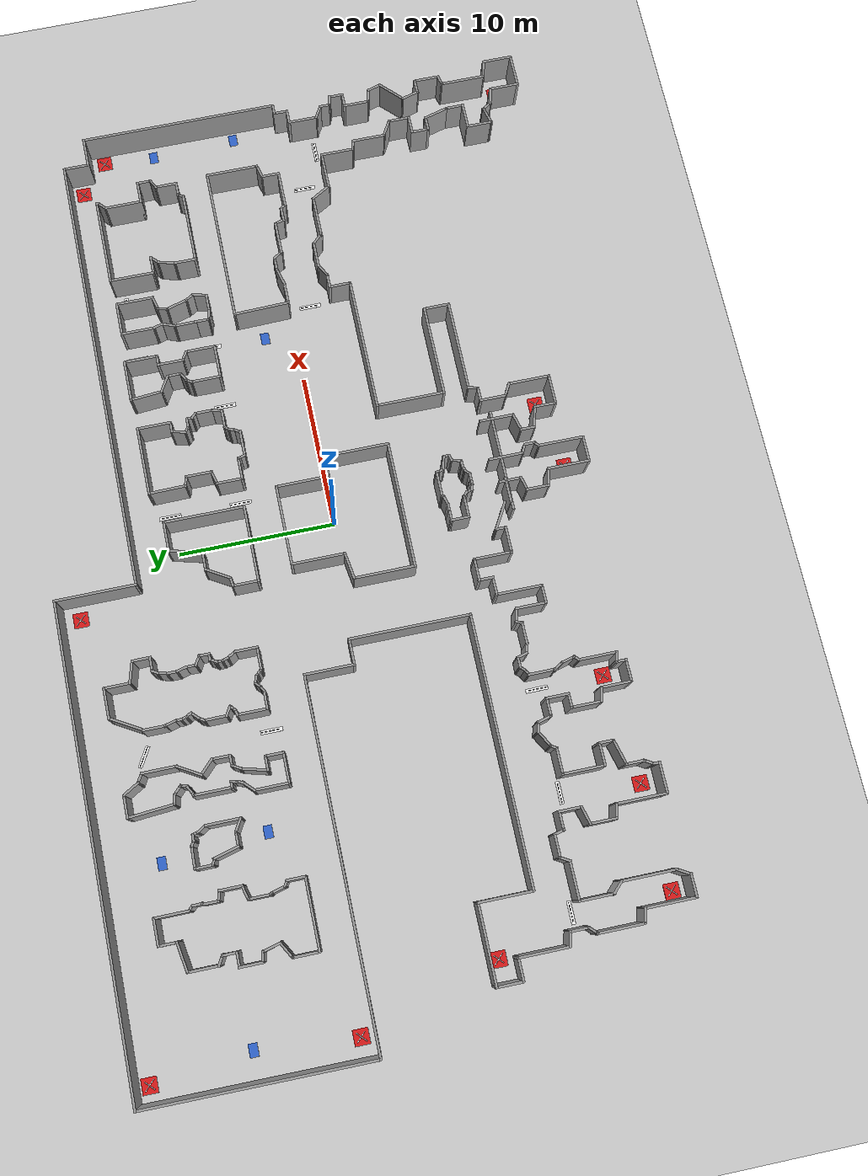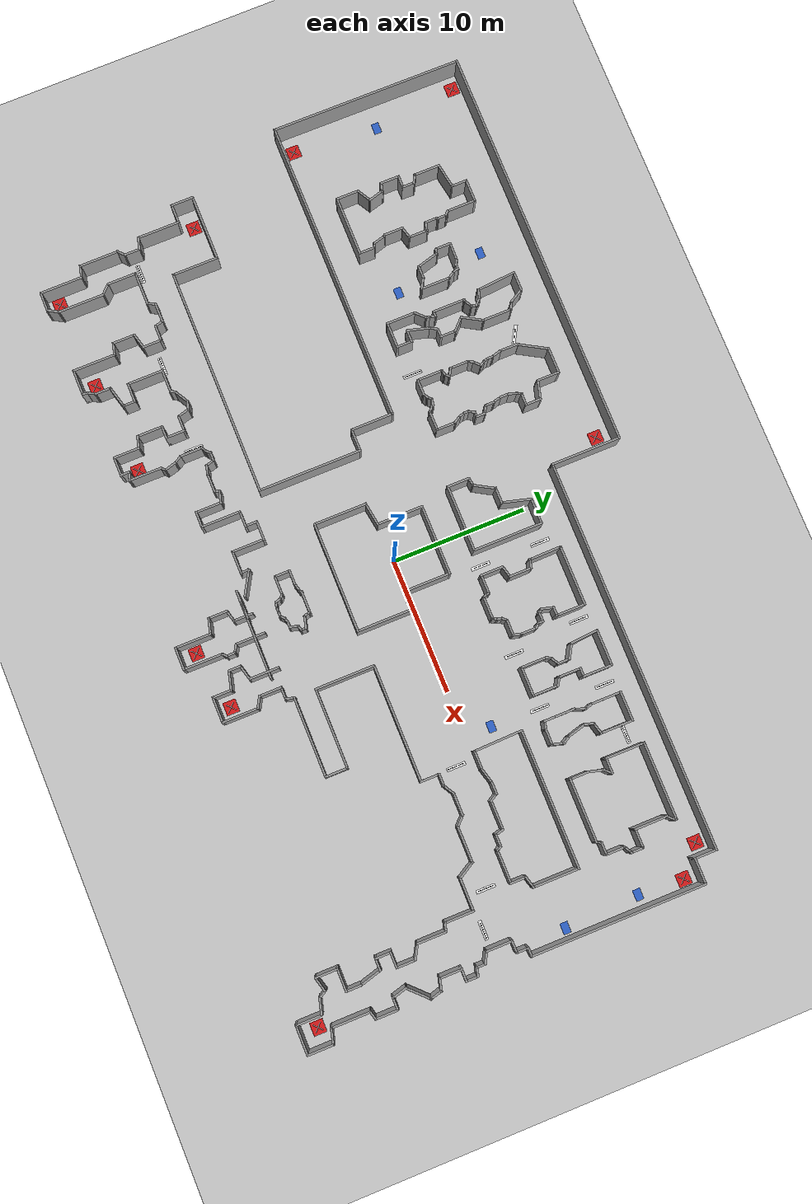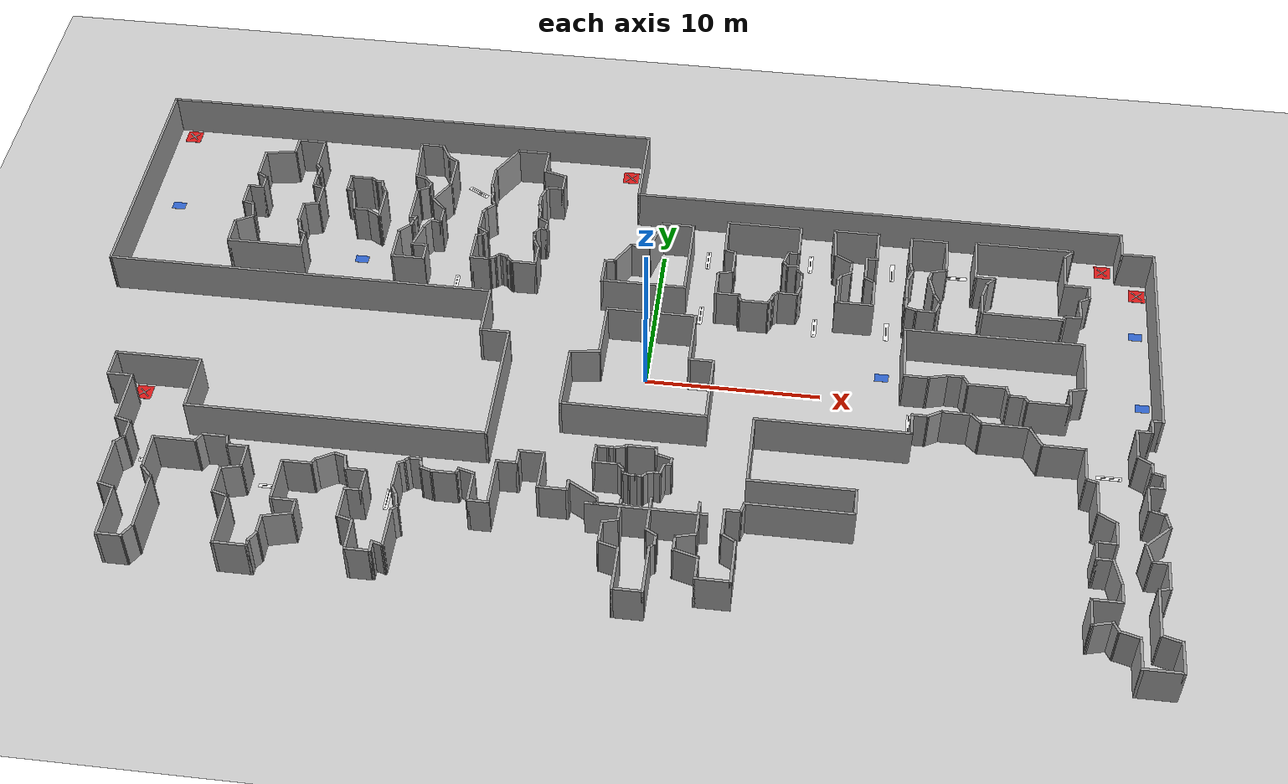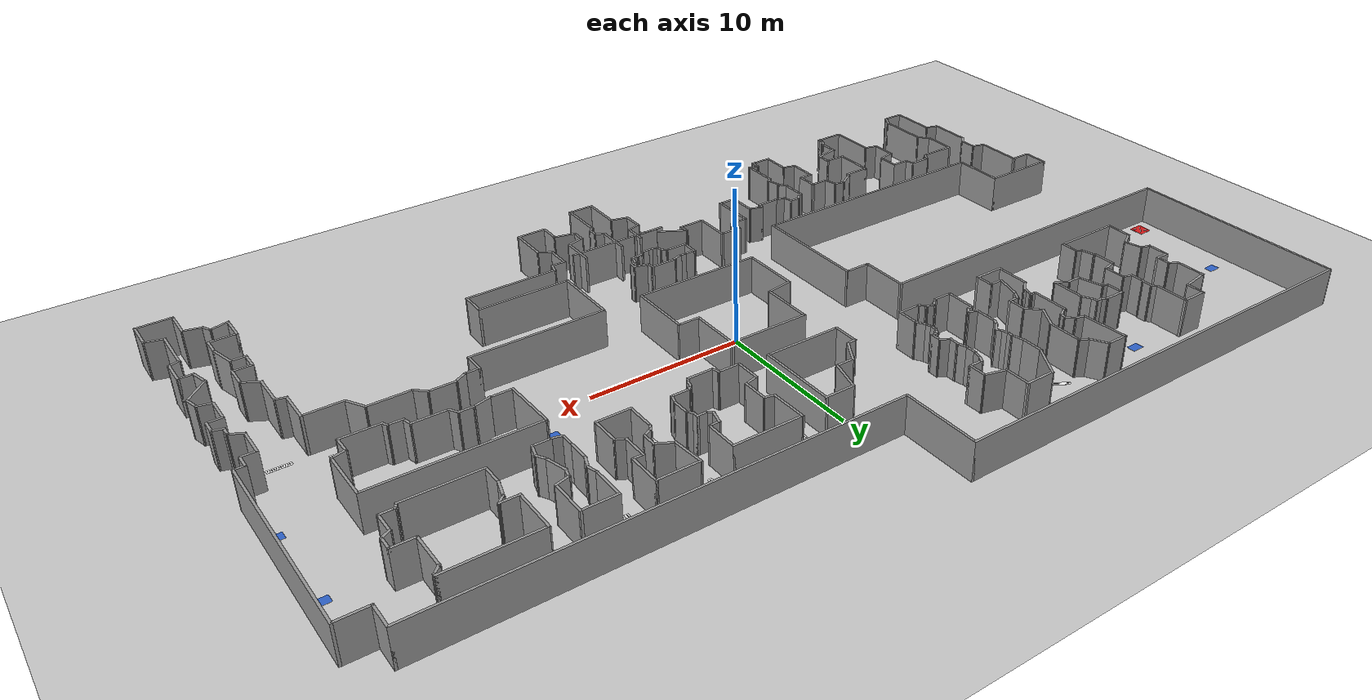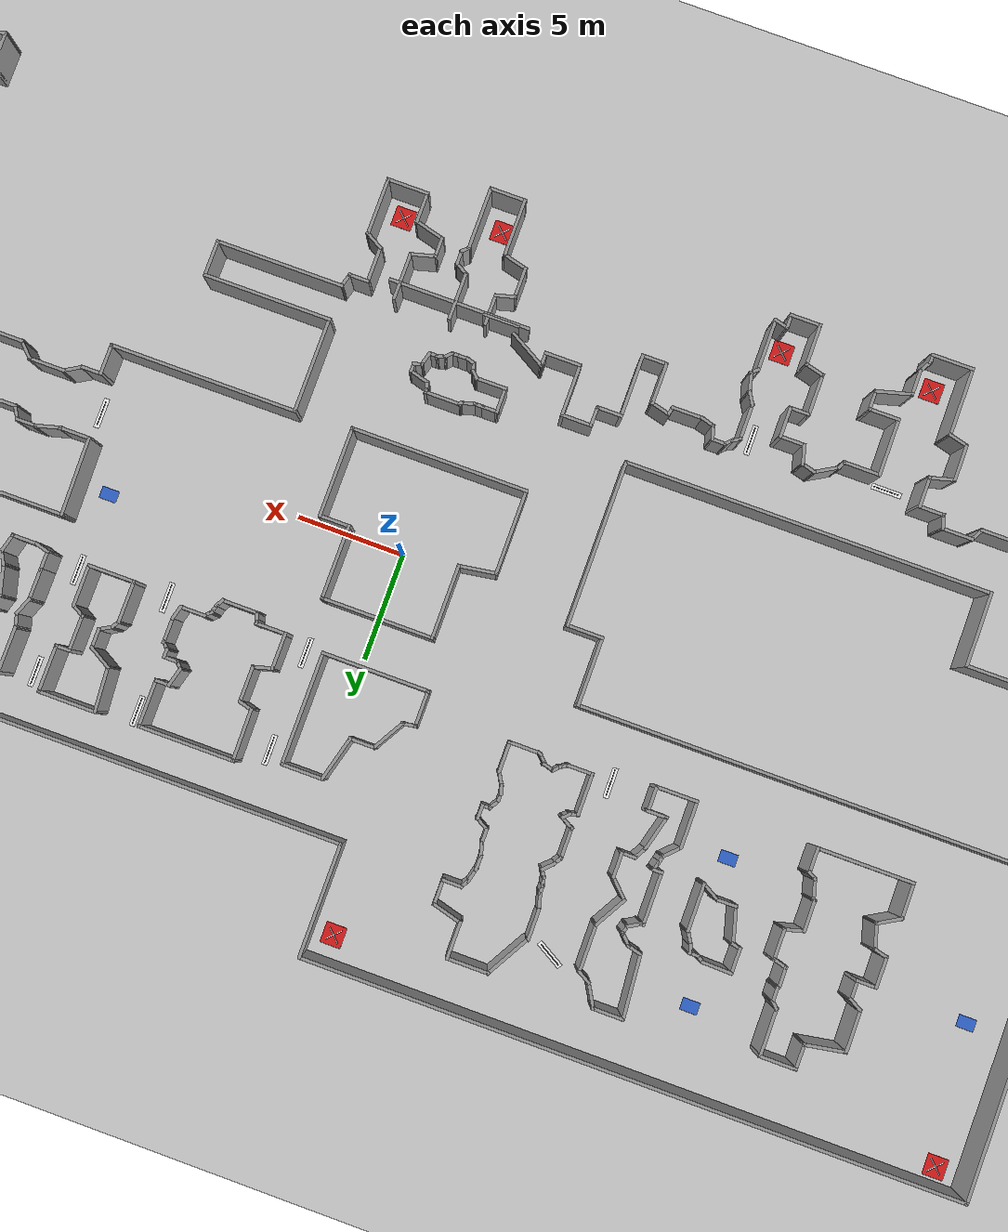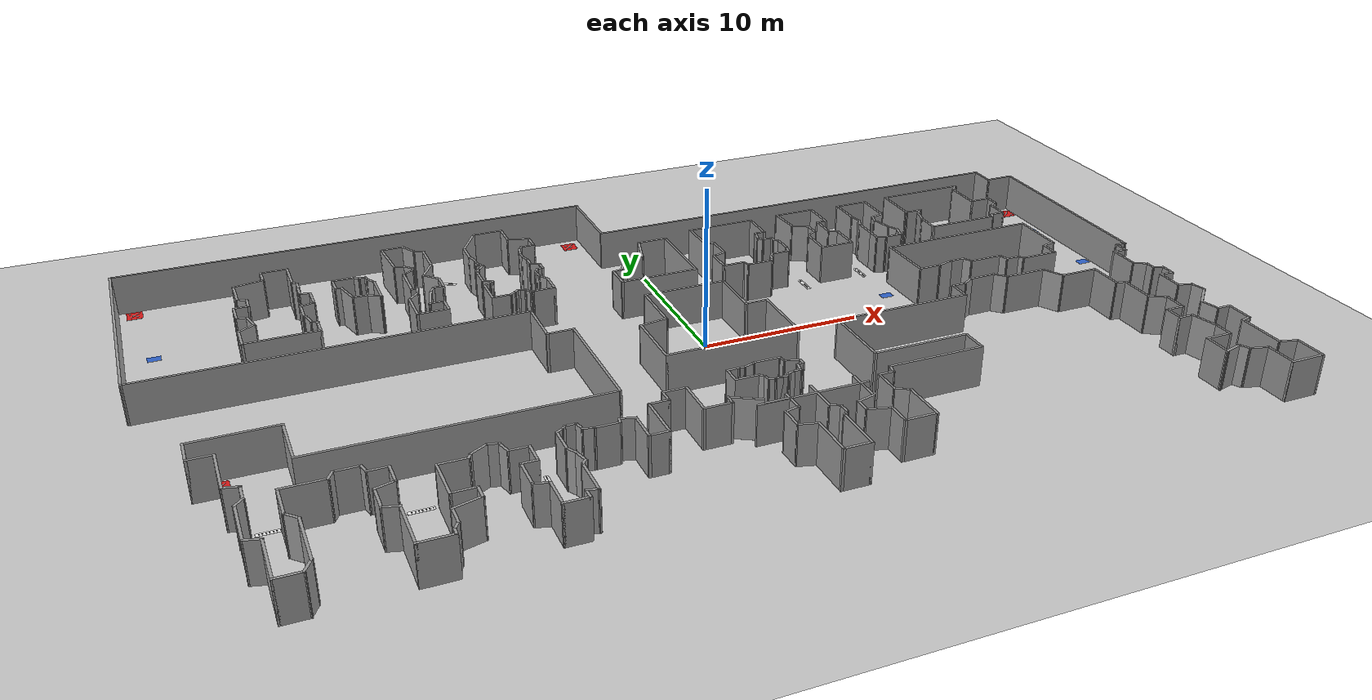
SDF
<sdf version="1.7">
 <world name="default">
  <light name="sun" type="directional">
   <pose>0 0 10 0 -0 0</pose>
   <diffuse>0.8 0.8 0.8 1</diffuse>
   <specular>0.2 0.2 0.2 1</specular>
   <attenuation>
    <range>1000</range>
    <constant>0.9</constant>
    <linear>0.01</linear>
    <quadratic>0.001</quadratic>
   </attenuation>
   <direction>-0.5 0.1 -0.9</direction>
   <spot><inner_angle>0</inner_angle><outer_angle>0</outer_angle><falloff>0</falloff></spot>
  </light>
  <model name="ground_plane">
   <static>1</static>
   <link name="link">
    <collision name="collision">
     <geometry><plane><normal>0 0 1</normal><size>100 100</size></plane></geometry>
     <surface>
      <contact><collide_bitmask>65535</collide_bitmask></contact>
      <friction><ode><mu>100</mu><mu2>50</mu2></ode></friction>
     </surface>
    </collision>
    <visual name="visual">
     <cast_shadows>0</cast_shadows>
     <geometry><plane><normal>0 0 1</normal><size>100 100</size></plane></geometry>
     <material>
      <script><uri>file://media/materials/scripts/gazebo.material</uri><name>Gazebo/Grey</name></script>
     </material>
    </visual>
   </link>
  </model>
  <gravity>0 0 -9.8</gravity>
  <magnetic_field>6e-06 2.3e-05 -4.2e-05</magnetic_field>
  <atmosphere type="adiabatic"/>
  <physics type="ode">
   <max_step_size>0.001</max_step_size>
   <real_time_factor>1</real_time_factor>
   <real_time_update_rate>1000</real_time_update_rate>
  </physics>
  <scene><ambient>0.4 0.4 0.4 1</ambient><background>0.7 0.7 0.7 1</background><shadows>1</shadows></scene>
  <audio><device>default</device></audio>
  <spherical_coordinates>
   <surface_model>EARTH_WGS84</surface_model>
   <latitude_deg>0</latitude_deg>
   <longitude_deg>0</longitude_deg>
   <elevation>0</elevation>
   <heading_deg>0</heading_deg>
  </spherical_coordinates>
  <model name="latest_world">
   <pose>-1.4911 -0.096187 0 0 -0 0</pose>
   <link name="Wall_0">
    <collision name="Wall_0_Collision">
     <geometry><box><size>30.25 0.15 2.5</size></box></geometry>
     <pose>0 0 1.25 0 -0 0</pose>
    </collision>
    <visual name="Wall_0_Visual">
     <pose>0 0 1.25 0 -0 0</pose>
     <geometry><box><size>30.25 0.15 2.5</size></box></geometry>
     <material>
      <script><uri>file://media/materials/scripts/gazebo.material</uri><name>Gazebo/Grey</name></script>
      <ambient>1 1 1 1</ambient>
     </material>
     <meta><layer>0</layer></meta>
    </visual>
    <pose>-15.4949 18.0157 0 0 -0 0</pose>
   </link>
   <link name="Wall_1">
    <collision name="Wall_1_Collision">
     <geometry><box><size>5.25 0.15 2.5</size></box></geometry>
     <pose>0 0 1.25 0 -0 0</pose>
    </collision>
    <visual name="Wall_1_Visual">
     <pose>0 0 1.25 0 -0 0</pose>
     <geometry><box><size>5.25 0.15 2.5</size></box></geometry>
     <material>
      <script><uri>file://media/materials/scripts/gazebo.material</uri><name>Gazebo/Grey</name></script>
      <ambient>1 1 1 1</ambient>
     </material>
     <meta><layer>0</layer></meta>
    </visual>
    <pose>-0.444891 15.4657 0 0 -0 -1.5708</pose>
   </link>
   <link name="Wall_10">
    <collision name="Wall_10_Collision">
     <geometry><box><size>1 0.15 2.5</size></box></geometry>
     <pose>0 0 1.25 0 -0 0</pose>
    </collision>
    <visual name="Wall_10_Visual">
     <pose>0 0 1.25 0 -0 0</pose>
     <geometry><box><size>1 0.15 2.5</size></box></geometry>
     <material>
      <script><uri>file://media/materials/scripts/gazebo.material</uri><name>Gazebo/Grey</name></script>
      <ambient>1 1 1 1</ambient>
     </material>
     <meta><layer>0</layer></meta>
    </visual>
    <pose>29.1732 -4.44675 0 0 -0 -0.523599</pose>
   </link>
   <link name="Wall_100">
    <collision name="Wall_100_Collision">
     <geometry><box><size>1 0.15 2.5</size></box></geometry>
     <pose>0 0 1.25 0 -0 0</pose>
    </collision>
    <visual name="Wall_100_Visual">
     <pose>0 0 1.25 0 -0 0</pose>
     <geometry><box><size>1 0.15 2.5</size></box></geometry>
     <material>
      <script><uri>file://media/materials/scripts/gazebo.material</uri><name>Gazebo/Grey</name></script>
      <ambient>1 1 1 1</ambient>
     </material>
     <meta><layer>0</layer></meta>
    </visual>
    <pose>-10.3814 -12.0748 0 0 -0 -1.309</pose>
   </link>
   <link name="Wall_101">
    <collision name="Wall_101_Collision">
     <geometry><box><size>0.5 0.15 2.5</size></box></geometry>
     <pose>0 0 1.25 0 -0 0</pose>
    </collision>
    <visual name="Wall_101_Visual">
     <pose>0 0 1.25 0 -0 0</pose>
     <geometry><box><size>0.5 0.15 2.5</size></box></geometry>
     <material>
      <script><uri>file://media/materials/scripts/gazebo.material</uri><name>Gazebo/Grey</name></script>
      <ambient>1 1 1 1</ambient>
     </material>
     <meta><layer>0</layer></meta>
    </visual>
    <pose>-10.3951 -12.609 0 0 -0 -2.35619</pose>
   </link>
   <link name="Wall_102">
    <collision name="Wall_102_Collision">
     <geometry><box><size>2.5 0.15 2.5</size></box></geometry>
     <pose>0 0 1.25 0 -0 0</pose>
    </collision>
    <visual name="Wall_102_Visual">
     <pose>0 0 1.25 0 -0 0</pose>
     <geometry><box><size>2.5 0.15 2.5</size></box></geometry>
     <material>
      <script><uri>file://media/materials/scripts/gazebo.material</uri><name>Gazebo/Grey</name></script>
      <ambient>1 1 1 1</ambient>
     </material>
     <meta><layer>0</layer></meta>
    </visual>
    <pose>-10.5189 -13.9078 0 0 -0 -1.5708</pose>
   </link>
   <link name="Wall_103">
    <collision name="Wall_103_Collision">
     <geometry><box><size>0.75 0.15 2.5</size></box></geometry>
     <pose>0 0 1.25 0 -0 0</pose>
    </collision>
    <visual name="Wall_103_Visual">
     <pose>0 0 1.25 0 -0 0</pose>
     <geometry><box><size>0.75 0.15 2.5</size></box></geometry>
     <material>
      <script><uri>file://media/materials/scripts/gazebo.material</uri><name>Gazebo/Grey</name></script>
      <ambient>1 1 1 1</ambient>
     </material>
     <meta><layer>0</layer></meta>
    </visual>
    <pose>-10.8086 -15.0051 0 0 -0 2.87979</pose>
   </link>
   <link name="Wall_104">
    <collision name="Wall_104_Collision">
     <geometry><box><size>0.75 0.15 2.5</size></box></geometry>
     <pose>0 0 1.25 0 -0 0</pose>
    </collision>
    <visual name="Wall_104_Visual">
     <pose>0 0 1.25 0 -0 0</pose>
     <geometry><box><size>0.75 0.15 2.5</size></box></geometry>
     <material>
      <script><uri>file://media/materials/scripts/gazebo.material</uri><name>Gazebo/Grey</name></script>
      <ambient>1 1 1 1</ambient>
     </material>
     <meta><layer>0</layer></meta>
    </visual>
    <pose>-11.0984 -15.2275 0 0 -0 -1.5708</pose>
   </link>
   <link name="Wall_105">
    <collision name="Wall_105_Collision">
     <geometry><box><size>0.16 0.15 2.5</size></box></geometry>
     <pose>0 0 1.25 0 -0 0</pose>
    </collision>
    <visual name="Wall_105_Visual">
     <pose>0 0 1.25 0 -0 0</pose>
     <geometry><box><size>0.16 0.15 2.5</size></box></geometry>
     <material>
      <script><uri>file://media/materials/scripts/gazebo.material</uri><name>Gazebo/Grey</name></script>
      <ambient>1 1 1 1</ambient>
     </material>
     <meta><layer>0</layer></meta>
    </visual>
    <pose>-11.0934 -15.5275 0 0 -0 0</pose>
   </link>
   <link name="Wall_106">
    <collision name="Wall_106_Collision">
     <geometry><box><size>1.5 0.15 2.5</size></box></geometry>
     <pose>0 0 1.25 0 -0 0</pose>
    </collision>
    <visual name="Wall_106_Visual">
     <pose>0 0 1.25 0 -0 0</pose>
     <geometry><box><size>1.5 0.15 2.5</size></box></geometry>
     <material>
      <script><uri>file://media/materials/scripts/gazebo.material</uri><name>Gazebo/Grey</name></script>
      <ambient>1 1 1 1</ambient>
     </material>
     <meta><layer>0</layer></meta>
    </visual>
    <pose>-11.7634 -15.5275 0 0 -0 3.14159</pose>
   </link>
   <link name="Wall_107">
    <collision name="Wall_107_Collision">
     <geometry><box><size>2 0.15 2.5</size></box></geometry>
     <pose>0 0 1.25 0 -0 0</pose>
    </collision>
    <visual name="Wall_107_Visual">
     <pose>0 0 1.25 0 -0 0</pose>
     <geometry><box><size>2 0.15 2.5</size></box></geometry>
     <material>
      <script><uri>file://media/materials/scripts/gazebo.material</uri><name>Gazebo/Grey</name></script>
      <ambient>1 1 1 1</ambient>
     </material>
     <meta><layer>0</layer></meta>
    </visual>
    <pose>-12.4384 -14.6025 0 0 -0 1.5708</pose>
   </link>
   <link name="Wall_108">
    <collision name="Wall_108_Collision">
     <geometry><box><size>1 0.15 2.5</size></box></geometry>
     <pose>0 0 1.25 0 -0 0</pose>
    </collision>
    <visual name="Wall_108_Visual">
     <pose>0 0 1.25 0 -0 0</pose>
     <geometry><box><size>1 0.15 2.5</size></box></geometry>
     <material>
      <script><uri>file://media/materials/scripts/gazebo.material</uri><name>Gazebo/Grey</name></script>
      <ambient>1 1 1 1</ambient>
     </material>
     <meta><layer>0</layer></meta>
    </visual>
    <pose>-12.8489 -13.5675 0 0 -0 2.87979</pose>
   </link>
   <link name="Wall_109">
    <collision name="Wall_109_Collision">
     <geometry><box><size>2 0.15 2.5</size></box></geometry>
     <pose>0 0 1.25 0 -0 0</pose>
    </collision>
    <visual name="Wall_109_Visual">
     <pose>0 0 1.25 0 -0 0</pose>
     <geometry><box><size>2 0.15 2.5</size></box></geometry>
     <material>
      <script><uri>file://media/materials/scripts/gazebo.material</uri><name>Gazebo/Grey</name></script>
      <ambient>1 1 1 1</ambient>
     </material>
     <meta><layer>0</layer></meta>
    </visual>
    <pose>-13.2595 -12.5325 0 0 -0 1.5708</pose>
   </link>
   <link name="Wall_11">
    <collision name="Wall_11_Collision">
     <geometry><box><size>0.75 0.15 2.5</size></box></geometry>
     <pose>0 0 1.25 0 -0 0</pose>
    </collision>
    <visual name="Wall_11_Visual">
     <pose>0 0 1.25 0 -0 0</pose>
     <geometry><box><size>0.75 0.15 2.5</size></box></geometry>
     <material>
      <script><uri>file://media/materials/scripts/gazebo.material</uri><name>Gazebo/Grey</name></script>
      <ambient>1 1 1 1</ambient>
     </material>
     <meta><layer>0</layer></meta>
    </visual>
    <pose>29.5412 -4.95925 0 0 -0 -1.5708</pose>
   </link>
   <link name="Wall_110">
    <collision name="Wall_110_Collision">
     <geometry><box><size>1 0.15 2.5</size></box></geometry>
     <pose>0 0 1.25 0 -0 0</pose>
    </collision>
    <visual name="Wall_110_Visual">
     <pose>0 0 1.25 0 -0 0</pose>
     <geometry><box><size>1 0.15 2.5</size></box></geometry>
     <material>
      <script><uri>file://media/materials/scripts/gazebo.material</uri><name>Gazebo/Grey</name></script>
      <ambient>1 1 1 1</ambient>
     </material>
     <meta><layer>0</layer></meta>
    </visual>
    <pose>-12.8345 -11.6075 0 0 -0 0</pose>
   </link>
   <link name="Wall_111">
    <collision name="Wall_111_Collision">
     <geometry><box><size>1.5 0.15 2.5</size></box></geometry>
     <pose>0 0 1.25 0 -0 0</pose>
    </collision>
    <visual name="Wall_111_Visual">
     <pose>0 0 1.25 0 -0 0</pose>
     <geometry><box><size>1.5 0.15 2.5</size></box></geometry>
     <material>
      <script><uri>file://media/materials/scripts/gazebo.material</uri><name>Gazebo/Grey</name></script>
      <ambient>1 1 1 1</ambient>
     </material>
     <meta><layer>0</layer></meta>
    </visual>
    <pose>-12.4095 -10.9325 0 0 -0 1.5708</pose>
   </link>
   <link name="Wall_112">
    <collision name="Wall_112_Collision">
     <geometry><box><size>1.25 0.15 2.5</size></box></geometry>
     <pose>0 0 1.25 0 -0 0</pose>
    </collision>
    <visual name="Wall_112_Visual">
     <pose>0 0 1.25 0 -0 0</pose>
     <geometry><box><size>1.25 0.15 2.5</size></box></geometry>
     <material>
      <script><uri>file://media/materials/scripts/gazebo.material</uri><name>Gazebo/Grey</name></script>
      <ambient>1 1 1 1</ambient>
     </material>
     <meta><layer>0</layer></meta>
    </visual>
    <pose>-12.9595 -10.2575 0 0 -0 3.14159</pose>
   </link>
   <link name="Wall_113">
    <collision name="Wall_113_Collision">
     <geometry><box><size>1 0.15 2.5</size></box></geometry>
     <pose>0 0 1.25 0 -0 0</pose>
    </collision>
    <visual name="Wall_113_Visual">
     <pose>0 0 1.25 0 -0 0</pose>
     <geometry><box><size>1 0.15 2.5</size></box></geometry>
     <material>
      <script><uri>file://media/materials/scripts/gazebo.material</uri><name>Gazebo/Grey</name></script>
      <ambient>1 1 1 1</ambient>
     </material>
     <meta><layer>0</layer></meta>
    </visual>
    <pose>-13.6195 -9.84696 0 0 -0 1.8326</pose>
   </link>
   <link name="Wall_114">
    <collision name="Wall_114_Collision">
     <geometry><box><size>0.75 0.15 2.5</size></box></geometry>
     <pose>0 0 1.25 0 -0 0</pose>
    </collision>
    <visual name="Wall_114_Visual">
     <pose>0 0 1.25 0 -0 0</pose>
     <geometry><box><size>0.75 0.15 2.5</size></box></geometry>
     <material>
      <script><uri>file://media/materials/scripts/gazebo.material</uri><name>Gazebo/Grey</name></script>
      <ambient>1 1 1 1</ambient>
     </material>
     <meta><layer>0</layer></meta>
    </visual>
    <pose>-14.0192 -9.3588 0 0 -0 2.87979</pose>
   </link>
   <link name="Wall_115">
    <collision name="Wall_115_Collision">
     <geometry><box><size>1.25 0.15 2.5</size></box></geometry>
     <pose>0 0 1.25 0 -0 0</pose>
    </collision>
    <visual name="Wall_115_Visual">
     <pose>0 0 1.25 0 -0 0</pose>
     <geometry><box><size>1.25 0.15 2.5</size></box></geometry>
     <material>
      <script><uri>file://media/materials/scripts/gazebo.material</uri><name>Gazebo/Grey</name></script>
      <ambient>1 1 1 1</ambient>
     </material>
     <meta><layer>0</layer></meta>
    </visual>
    <pose>-14.7853 -9.55615 0 0 -0 -2.61799</pose>
   </link>
   <link name="Wall_116">
    <collision name="Wall_116_Collision">
     <geometry><box><size>0.5 0.15 2.5</size></box></geometry>
     <pose>0 0 1.25 0 -0 0</pose>
    </collision>
    <visual name="Wall_116_Visual">
     <pose>0 0 1.25 0 -0 0</pose>
     <geometry><box><size>0.5 0.15 2.5</size></box></geometry>
     <material>
      <script><uri>file://media/materials/scripts/gazebo.material</uri><name>Gazebo/Grey</name></script>
      <ambient>1 1 1 1</ambient>
     </material>
     <meta><layer>0</layer></meta>
    </visual>
    <pose>-15.3491 -9.98271 0 0 -0 -2.0944</pose>
   </link>
   <link name="Wall_117">
    <collision name="Wall_117_Collision">
     <geometry><box><size>1.75 0.15 2.5</size></box></geometry>
     <pose>0 0 1.25 0 -0 0</pose>
    </collision>
    <visual name="Wall_117_Visual">
     <pose>0 0 1.25 0 -0 0</pose>
     <geometry><box><size>1.75 0.15 2.5</size></box></geometry>
     <material>
      <script><uri>file://media/materials/scripts/gazebo.material</uri><name>Gazebo/Grey</name></script>
      <ambient>1 1 1 1</ambient>
     </material>
     <meta><layer>0</layer></meta>
    </visual>
    <pose>-16.2366 -10.1343 0 0 -0 3.14159</pose>
   </link>
   <link name="Wall_118">
    <collision name="Wall_118_Collision">
     <geometry><box><size>2.75 0.15 2.5</size></box></geometry>
     <pose>0 0 1.25 0 -0 0</pose>
    </collision>
    <visual name="Wall_118_Visual">
     <pose>0 0 1.25 0 -0 0</pose>
     <geometry><box><size>2.75 0.15 2.5</size></box></geometry>
     <material>
      <script><uri>file://media/materials/scripts/gazebo.material</uri><name>Gazebo/Grey</name></script>
      <ambient>1 1 1 1</ambient>
     </material>
     <meta><layer>0</layer></meta>
    </visual>
    <pose>-17.0366 -11.4343 0 0 -0 -1.5708</pose>
   </link>
   <link name="Wall_119">
    <collision name="Wall_119_Collision">
     <geometry><box><size>1.5 0.15 2.5</size></box></geometry>
     <pose>0 0 1.25 0 -0 0</pose>
    </collision>
    <visual name="Wall_119_Visual">
     <pose>0 0 1.25 0 -0 0</pose>
     <geometry><box><size>1.5 0.15 2.5</size></box></geometry>
     <material>
      <script><uri>file://media/materials/scripts/gazebo.material</uri><name>Gazebo/Grey</name></script>
      <ambient>1 1 1 1</ambient>
     </material>
     <meta><layer>0</layer></meta>
    </visual>
    <pose>-16.3616 -12.7343 0 0 -0 0</pose>
   </link>
   <link name="Wall_12">
    <collision name="Wall_12_Collision">
     <geometry><box><size>0.75 0.15 2.5</size></box></geometry>
     <pose>0 0 1.25 0 -0 0</pose>
    </collision>
    <visual name="Wall_12_Visual">
     <pose>0 0 1.25 0 -0 0</pose>
     <geometry><box><size>0.75 0.15 2.5</size></box></geometry>
     <material>
      <script><uri>file://media/materials/scripts/gazebo.material</uri><name>Gazebo/Grey</name></script>
      <ambient>1 1 1 1</ambient>
     </material>
     <meta><layer>0</layer></meta>
    </visual>
    <pose>29.831 -5.3369 0 0 -0 -0.261799</pose>
   </link>
   <link name="Wall_120">
    <collision name="Wall_120_Collision">
     <geometry><box><size>1 0.15 2.5</size></box></geometry>
     <pose>0 0 1.25 0 -0 0</pose>
    </collision>
    <visual name="Wall_120_Visual">
     <pose>0 0 1.25 0 -0 0</pose>
     <geometry><box><size>1 0.15 2.5</size></box></geometry>
     <material>
      <script><uri>file://media/materials/scripts/gazebo.material</uri><name>Gazebo/Grey</name></script>
      <ambient>1 1 1 1</ambient>
     </material>
     <meta><layer>0</layer></meta>
    </visual>
    <pose>-15.6866 -13.1593 0 0 -0 -1.5708</pose>
   </link>
   <link name="Wall_121">
    <collision name="Wall_121_Collision">
     <geometry><box><size>1.75 0.15 2.5</size></box></geometry>
     <pose>0 0 1.25 0 -0 0</pose>
    </collision>
    <visual name="Wall_121_Visual">
     <pose>0 0 1.25 0 -0 0</pose>
     <geometry><box><size>1.75 0.15 2.5</size></box></geometry>
     <material>
      <script><uri>file://media/materials/scripts/gazebo.material</uri><name>Gazebo/Grey</name></script>
      <ambient>1 1 1 1</ambient>
     </material>
     <meta><layer>0</layer></meta>
    </visual>
    <pose>-16.4594 -13.7913 0 0 -0 -2.87979</pose>
   </link>
   <link name="Wall_122">
    <collision name="Wall_122_Collision">
     <geometry><box><size>1.25 0.15 2.5</size></box></geometry>
     <pose>0 0 1.25 0 -0 0</pose>
    </collision>
    <visual name="Wall_122_Visual">
     <pose>0 0 1.25 0 -0 0</pose>
     <geometry><box><size>1.25 0.15 2.5</size></box></geometry>
     <material>
      <script><uri>file://media/materials/scripts/gazebo.material</uri><name>Gazebo/Grey</name></script>
      <ambient>1 1 1 1</ambient>
     </material>
     <meta><layer>0</layer></meta>
    </visual>
    <pose>-17.2321 -14.5484 0 0 -0 -1.5708</pose>
   </link>
   <link name="Wall_123">
    <collision name="Wall_123_Collision">
     <geometry><box><size>0.75 0.15 2.5</size></box></geometry>
     <pose>0 0 1.25 0 -0 0</pose>
    </collision>
    <visual name="Wall_123_Visual">
     <pose>0 0 1.25 0 -0 0</pose>
     <geometry><box><size>0.75 0.15 2.5</size></box></geometry>
     <material>
      <script><uri>file://media/materials/scripts/gazebo.material</uri><name>Gazebo/Grey</name></script>
      <ambient>1 1 1 1</ambient>
     </material>
     <meta><layer>0</layer></meta>
    </visual>
    <pose>-17.3821 -15.3582 0 0 -0 -2.0944</pose>
   </link>
   <link name="Wall_124">
    <collision name="Wall_124_Collision">
     <geometry><box><size>0.5 0.15 2.5</size></box></geometry>
     <pose>0 0 1.25 0 -0 0</pose>
    </collision>
    <visual name="Wall_124_Visual">
     <pose>0 0 1.25 0 -0 0</pose>
     <geometry><box><size>0.5 0.15 2.5</size></box></geometry>
     <material>
      <script><uri>file://media/materials/scripts/gazebo.material</uri><name>Gazebo/Grey</name></script>
      <ambient>1 1 1 1</ambient>
     </material>
     <meta><layer>0</layer></meta>
    </visual>
    <pose>-17.5321 -15.793 0 0 -0 -1.5708</pose>
   </link>
   <link name="Wall_125">
    <collision name="Wall_125_Collision">
     <geometry><box><size>2 0.15 2.5</size></box></geometry>
     <pose>0 0 1.25 0 -0 0</pose>
    </collision>
    <visual name="Wall_125_Visual">
     <pose>0 0 1.25 0 -0 0</pose>
     <geometry><box><size>2 0.15 2.5</size></box></geometry>
     <material>
      <script><uri>file://media/materials/scripts/gazebo.material</uri><name>Gazebo/Grey</name></script>
      <ambient>1 1 1 1</ambient>
     </material>
     <meta><layer>0</layer></meta>
    </visual>
    <pose>-18.4571 -15.968 0 0 -0 3.14159</pose>
   </link>
   <link name="Wall_126">
    <collision name="Wall_126_Collision">
     <geometry><box><size>3.25 0.15 2.5</size></box></geometry>
     <pose>0 0 1.25 0 -0 0</pose>
    </collision>
    <visual name="Wall_126_Visual">
     <pose>0 0 1.25 0 -0 0</pose>
     <geometry><box><size>3.25 0.15 2.5</size></box></geometry>
     <material>
      <script><uri>file://media/materials/scripts/gazebo.material</uri><name>Gazebo/Grey</name></script>
      <ambient>1 1 1 1</ambient>
     </material>
     <meta><layer>0</layer></meta>
    </visual>
    <pose>-19.3821 -14.418 0 0 -0 1.5708</pose>
   </link>
   <link name="Wall_127">
    <collision name="Wall_127_Collision">
     <geometry><box><size>1 0.15 2.5</size></box></geometry>
     <pose>0 0 1.25 0 -0 0</pose>
    </collision>
    <visual name="Wall_127_Visual">
     <pose>0 0 1.25 0 -0 0</pose>
     <geometry><box><size>1 0.15 2.5</size></box></geometry>
     <material>
      <script><uri>file://media/materials/scripts/gazebo.material</uri><name>Gazebo/Grey</name></script>
      <ambient>1 1 1 1</ambient>
     </material>
     <meta><layer>0</layer></meta>
    </visual>
    <pose>-19.7926 -12.758 0 0 -0 2.87979</pose>
   </link>
   <link name="Wall_128">
    <collision name="Wall_128_Collision">
     <geometry><box><size>1.75 0.15 2.5</size></box></geometry>
     <pose>0 0 1.25 0 -0 0</pose>
    </collision>
    <visual name="Wall_128_Visual">
     <pose>0 0 1.25 0 -0 0</pose>
     <geometry><box><size>1.75 0.15 2.5</size></box></geometry>
     <material>
      <script><uri>file://media/materials/scripts/gazebo.material</uri><name>Gazebo/Grey</name></script>
      <ambient>1 1 1 1</ambient>
     </material>
     <meta><layer>0</layer></meta>
    </visual>
    <pose>-20.2032 -11.848 0 0 -0 1.5708</pose>
   </link>
   <link name="Wall_129">
    <collision name="Wall_129_Collision">
     <geometry><box><size>1.25 0.15 2.5</size></box></geometry>
     <pose>0 0 1.25 0 -0 0</pose>
    </collision>
    <visual name="Wall_129_Visual">
     <pose>0 0 1.25 0 -0 0</pose>
     <geometry><box><size>1.25 0.15 2.5</size></box></geometry>
     <material>
      <script><uri>file://media/materials/scripts/gazebo.material</uri><name>Gazebo/Grey</name></script>
      <ambient>1 1 1 1</ambient>
     </material>
     <meta><layer>0</layer></meta>
    </visual>
    <pose>-19.6719 -10.9056 0 0 -0 0.261799</pose>
   </link>
   <link name="Wall_13">
    <collision name="Wall_13_Collision">
     <geometry><box><size>1 0.15 2.5</size></box></geometry>
     <pose>0 0 1.25 0 -0 0</pose>
    </collision>
    <visual name="Wall_13_Visual">
     <pose>0 0 1.25 0 -0 0</pose>
     <geometry><box><size>1 0.15 2.5</size></box></geometry>
     <material>
      <script><uri>file://media/materials/scripts/gazebo.material</uri><name>Gazebo/Grey</name></script>
      <ambient>1 1 1 1</ambient>
     </material>
     <meta><layer>0</layer></meta>
    </visual>
    <pose>30.1208 -5.83954 0 0 -0 -1.5708</pose>
   </link>
   <link name="Wall_130">
    <collision name="Wall_130_Collision">
     <geometry><box><size>1.5 0.15 2.5</size></box></geometry>
     <pose>0 0 1.25 0 -0 0</pose>
    </collision>
    <visual name="Wall_130_Visual">
     <pose>0 0 1.25 0 -0 0</pose>
     <geometry><box><size>1.5 0.15 2.5</size></box></geometry>
     <material>
      <script><uri>file://media/materials/scripts/gazebo.material</uri><name>Gazebo/Grey</name></script>
      <ambient>1 1 1 1</ambient>
     </material>
     <meta><layer>0</layer></meta>
    </visual>
    <pose>-19.1406 -10.0883 0 0 -0 1.5708</pose>
   </link>
   <link name="Wall_131">
    <collision name="Wall_131_Collision">
     <geometry><box><size>1.25 0.15 2.5</size></box></geometry>
     <pose>0 0 1.25 0 -0 0</pose>
    </collision>
    <visual name="Wall_131_Visual">
     <pose>0 0 1.25 0 -0 0</pose>
     <geometry><box><size>1.25 0.15 2.5</size></box></geometry>
     <material>
      <script><uri>file://media/materials/scripts/gazebo.material</uri><name>Gazebo/Grey</name></script>
      <ambient>1 1 1 1</ambient>
     </material>
     <meta><layer>0</layer></meta>
    </visual>
    <pose>-19.6906 -9.41329 0 0 -0 3.14159</pose>
   </link>
   <link name="Wall_132">
    <collision name="Wall_132_Collision">
     <geometry><box><size>0.75 0.15 2.5</size></box></geometry>
     <pose>0 0 1.25 0 -0 0</pose>
    </collision>
    <visual name="Wall_132_Visual">
     <pose>0 0 1.25 0 -0 0</pose>
     <geometry><box><size>0.75 0.15 2.5</size></box></geometry>
     <material>
      <script><uri>file://media/materials/scripts/gazebo.material</uri><name>Gazebo/Grey</name></script>
      <ambient>1 1 1 1</ambient>
     </material>
     <meta><layer>0</layer></meta>
    </visual>
    <pose>-20.3183 -9.12351 0 0 -0 1.8326</pose>
   </link>
   <link name="Wall_133">
    <collision name="Wall_133_Collision">
     <geometry><box><size>1.5 0.15 2.5</size></box></geometry>
     <pose>0 0 1.25 0 -0 0</pose>
    </collision>
    <visual name="Wall_133_Visual">
     <pose>0 0 1.25 0 -0 0</pose>
     <geometry><box><size>1.5 0.15 2.5</size></box></geometry>
     <material>
      <script><uri>file://media/materials/scripts/gazebo.material</uri><name>Gazebo/Grey</name></script>
      <ambient>1 1 1 1</ambient>
     </material>
     <meta><layer>0</layer></meta>
    </visual>
    <pose>-21.0709 -8.83374 0 0 -0 3.14159</pose>
   </link>
   <link name="Wall_134">
    <collision name="Wall_134_Collision">
     <geometry><box><size>0.75 0.15 2.5</size></box></geometry>
     <pose>0 0 1.25 0 -0 0</pose>
    </collision>
    <visual name="Wall_134_Visual">
     <pose>0 0 1.25 0 -0 0</pose>
     <geometry><box><size>0.75 0.15 2.5</size></box></geometry>
     <material>
      <script><uri>file://media/materials/scripts/gazebo.material</uri><name>Gazebo/Grey</name></script>
      <ambient>1 1 1 1</ambient>
     </material>
     <meta><layer>0</layer></meta>
    </visual>
    <pose>-21.8959 -9.09354 0 0 -0 -2.0944</pose>
   </link>
   <link name="Wall_135">
    <collision name="Wall_135_Collision">
     <geometry><box><size>2.5 0.15 2.5</size></box></geometry>
     <pose>0 0 1.25 0 -0 0</pose>
    </collision>
    <visual name="Wall_135_Visual">
     <pose>0 0 1.25 0 -0 0</pose>
     <geometry><box><size>2.5 0.15 2.5</size></box></geometry>
     <material>
      <script><uri>file://media/materials/scripts/gazebo.material</uri><name>Gazebo/Grey</name></script>
      <ambient>1 1 1 1</ambient>
     </material>
     <meta><layer>0</layer></meta>
    </visual>
    <pose>-23.2209 -9.35335 0 0 -0 3.14159</pose>
   </link>
   <link name="Wall_136">
    <collision name="Wall_136_Collision">
     <geometry><box><size>2.25 0.15 2.5</size></box></geometry>
     <pose>0 0 1.25 0 -0 0</pose>
    </collision>
    <visual name="Wall_136_Visual">
     <pose>0 0 1.25 0 -0 0</pose>
     <geometry><box><size>2.25 0.15 2.5</size></box></geometry>
     <material>
      <script><uri>file://media/materials/scripts/gazebo.material</uri><name>Gazebo/Grey</name></script>
      <ambient>1 1 1 1</ambient>
     </material>
     <meta><layer>0</layer></meta>
    </visual>
    <pose>-24.3959 -10.4033 0 0 -0 -1.5708</pose>
   </link>
   <link name="Wall_137">
    <collision name="Wall_137_Collision">
     <geometry><box><size>1 0.15 2.5</size></box></geometry>
     <pose>0 0 1.25 0 -0 0</pose>
    </collision>
    <visual name="Wall_137_Visual">
     <pose>0 0 1.25 0 -0 0</pose>
     <geometry><box><size>1 0.15 2.5</size></box></geometry>
     <material>
      <script><uri>file://media/materials/scripts/gazebo.material</uri><name>Gazebo/Grey</name></script>
      <ambient>1 1 1 1</ambient>
     </material>
     <meta><layer>0</layer></meta>
    </visual>
    <pose>-24.0954 -11.7539 0 0 -0 -0.785398</pose>
   </link>
   <link name="Wall_138">
    <collision name="Wall_138_Collision">
     <geometry><box><size>3.5 0.15 2.5</size></box></geometry>
     <pose>0 0 1.25 0 -0 0</pose>
    </collision>
    <visual name="Wall_138_Visual">
     <pose>0 0 1.25 0 -0 0</pose>
     <geometry><box><size>3.5 0.15 2.5</size></box></geometry>
     <material>
      <script><uri>file://media/materials/scripts/gazebo.material</uri><name>Gazebo/Grey</name></script>
      <ambient>1 1 1 1</ambient>
     </material>
     <meta><layer>0</layer></meta>
    </visual>
    <pose>-23.7949 -13.7294 0 0 -0 -1.5708</pose>
   </link>
   <link name="Wall_139">
    <collision name="Wall_139_Collision">
     <geometry><box><size>1 0.15 2.5</size></box></geometry>
     <pose>0 0 1.25 0 -0 0</pose>
    </collision>
    <visual name="Wall_139_Visual">
     <pose>0 0 1.25 0 -0 0</pose>
     <geometry><box><size>1 0.15 2.5</size></box></geometry>
     <material>
      <script><uri>file://media/materials/scripts/gazebo.material</uri><name>Gazebo/Grey</name></script>
      <ambient>1 1 1 1</ambient>
     </material>
     <meta><layer>0</layer></meta>
    </visual>
    <pose>-24.0074 -15.7725 0 0 -0 -2.0944</pose>
   </link>
   <link name="Wall_14">
    <collision name="Wall_14_Collision">
     <geometry><box><size>1 0.15 2.5</size></box></geometry>
     <pose>0 0 1.25 0 -0 0</pose>
    </collision>
    <visual name="Wall_14_Visual">
     <pose>0 0 1.25 0 -0 0</pose>
     <geometry><box><size>1 0.15 2.5</size></box></geometry>
     <material>
      <script><uri>file://media/materials/scripts/gazebo.material</uri><name>Gazebo/Grey</name></script>
      <ambient>1 1 1 1</ambient>
     </material>
     <meta><layer>0</layer></meta>
    </visual>
    <pose>29.6958 -6.26454 0 0 -0 3.14159</pose>
   </link>
   <link name="Wall_140">
    <collision name="Wall_140_Collision">
     <geometry><box><size>1.5 0.15 2.5</size></box></geometry>
     <pose>0 0 1.25 0 -0 0</pose>
    </collision>
    <visual name="Wall_140_Visual">
     <pose>0 0 1.25 0 -0 0</pose>
     <geometry><box><size>1.5 0.15 2.5</size></box></geometry>
     <material>
      <script><uri>file://media/materials/scripts/gazebo.material</uri><name>Gazebo/Grey</name></script>
      <ambient>1 1 1 1</ambient>
     </material>
     <meta><layer>0</layer></meta>
    </visual>
    <pose>-24.8949 -16.1405 0 0 -0 3.14159</pose>
   </link>
   <link name="Wall_141">
    <collision name="Wall_141_Collision">
     <geometry><box><size>3.25 0.15 2.5</size></box></geometry>
     <pose>0 0 1.25 0 -0 0</pose>
    </collision>
    <visual name="Wall_141_Visual">
     <pose>0 0 1.25 0 -0 0</pose>
     <geometry><box><size>3.25 0.15 2.5</size></box></geometry>
     <material>
      <script><uri>file://media/materials/scripts/gazebo.material</uri><name>Gazebo/Grey</name></script>
      <ambient>1 1 1 1</ambient>
     </material>
     <meta><layer>0</layer></meta>
    </visual>
    <pose>-25.5699 -14.5905 0 0 -0 1.5708</pose>
   </link>
   <link name="Wall_142">
    <collision name="Wall_142_Collision">
     <geometry><box><size>1 0.15 2.5</size></box></geometry>
     <pose>0 0 1.25 0 -0 0</pose>
    </collision>
    <visual name="Wall_142_Visual">
     <pose>0 0 1.25 0 -0 0</pose>
     <geometry><box><size>1 0.15 2.5</size></box></geometry>
     <material>
      <script><uri>file://media/materials/scripts/gazebo.material</uri><name>Gazebo/Grey</name></script>
      <ambient>1 1 1 1</ambient>
     </material>
     <meta><layer>0</layer></meta>
    </visual>
    <pose>-25.9804 -12.9305 0 0 -0 2.87979</pose>
   </link>
   <link name="Wall_143">
    <collision name="Wall_143_Collision">
     <geometry><box><size>3 0.15 2.5</size></box></geometry>
     <pose>0 0 1.25 0 -0 0</pose>
    </collision>
    <visual name="Wall_143_Visual">
     <pose>0 0 1.25 0 -0 0</pose>
     <geometry><box><size>3 0.15 2.5</size></box></geometry>
     <material>
      <script><uri>file://media/materials/scripts/gazebo.material</uri><name>Gazebo/Grey</name></script>
      <ambient>1 1 1 1</ambient>
     </material>
     <meta><layer>0</layer></meta>
    </visual>
    <pose>-26.3909 -11.3955 0 0 -0 1.5708</pose>
   </link>
   <link name="Wall_144">
    <collision name="Wall_144_Collision">
     <geometry><box><size>0.75 0.15 2.5</size></box></geometry>
     <pose>0 0 1.25 0 -0 0</pose>
    </collision>
    <visual name="Wall_144_Visual">
     <pose>0 0 1.25 0 -0 0</pose>
     <geometry><box><size>0.75 0.15 2.5</size></box></geometry>
     <material>
      <script><uri>file://media/materials/scripts/gazebo.material</uri><name>Gazebo/Grey</name></script>
      <ambient>1 1 1 1</ambient>
     </material>
     <meta><layer>0</layer></meta>
    </visual>
    <pose>-26.1788 -9.75839 0 0 -0 0.785398</pose>
   </link>
   <link name="Wall_145">
    <collision name="Wall_145_Collision">
     <geometry><box><size>1.25 0.15 2.5</size></box></geometry>
     <pose>0 0 1.25 0 -0 0</pose>
    </collision>
    <visual name="Wall_145_Visual">
     <pose>0 0 1.25 0 -0 0</pose>
     <geometry><box><size>1.25 0.15 2.5</size></box></geometry>
     <material>
      <script><uri>file://media/materials/scripts/gazebo.material</uri><name>Gazebo/Grey</name></script>
      <ambient>1 1 1 1</ambient>
     </material>
     <meta><layer>0</layer></meta>
    </visual>
    <pose>-25.9667 -8.99625 0 0 -0 1.5708</pose>
   </link>
   <link name="Wall_146">
    <collision name="Wall_146_Collision">
     <geometry><box><size>1 0.15 2.5</size></box></geometry>
     <pose>0 0 1.25 0 -0 0</pose>
    </collision>
    <visual name="Wall_146_Visual">
     <pose>0 0 1.25 0 -0 0</pose>
     <geometry><box><size>1 0.15 2.5</size></box></geometry>
     <material>
      <script><uri>file://media/materials/scripts/gazebo.material</uri><name>Gazebo/Grey</name></script>
      <ambient>1 1 1 1</ambient>
     </material>
     <meta><layer>0</layer></meta>
    </visual>
    <pose>-26.3772 -8.33625 0 0 -0 2.87979</pose>
   </link>
   <link name="Wall_147">
    <collision name="Wall_147_Collision">
     <geometry><box><size>3.25 0.15 2.5</size></box></geometry>
     <pose>0 0 1.25 0 -0 0</pose>
    </collision>
    <visual name="Wall_147_Visual">
     <pose>0 0 1.25 0 -0 0</pose>
     <geometry><box><size>3.25 0.15 2.5</size></box></geometry>
     <material>
      <script><uri>file://media/materials/scripts/gazebo.material</uri><name>Gazebo/Grey</name></script>
      <ambient>1 1 1 1</ambient>
     </material>
     <meta><layer>0</layer></meta>
    </visual>
    <pose>-26.7877 -6.67626 0 0 -0 1.5708</pose>
   </link>
   <link name="Wall_148">
    <collision name="Wall_148_Collision">
     <geometry><box><size>1.5 0.15 2.5</size></box></geometry>
     <pose>0 0 1.25 0 -0 0</pose>
    </collision>
    <visual name="Wall_148_Visual">
     <pose>0 0 1.25 0 -0 0</pose>
     <geometry><box><size>1.5 0.15 2.5</size></box></geometry>
     <material>
      <script><uri>file://media/materials/scripts/gazebo.material</uri><name>Gazebo/Grey</name></script>
      <ambient>1 1 1 1</ambient>
     </material>
     <meta><layer>0</layer></meta>
    </visual>
    <pose>-27.4627 -5.12626 0 0 -0 3.14159</pose>
   </link>
   <link name="Wall_149">
    <collision name="Wall_149_Collision">
     <geometry><box><size>1.75 0.15 2.5</size></box></geometry>
     <pose>0 0 1.25 0 -0 0</pose>
    </collision>
    <visual name="Wall_149_Visual">
     <pose>0 0 1.25 0 -0 0</pose>
     <geometry><box><size>1.75 0.15 2.5</size></box></geometry>
     <material>
      <script><uri>file://media/materials/scripts/gazebo.material</uri><name>Gazebo/Grey</name></script>
      <ambient>1 1 1 1</ambient>
     </material>
     <meta><layer>0</layer></meta>
    </visual>
    <pose>-28.1377 -4.32626 0 0 -0 1.5708</pose>
   </link>
   <link name="Wall_15">
    <collision name="Wall_15_Collision">
     <geometry><box><size>1.75 0.15 2.5</size></box></geometry>
     <pose>0 0 1.25 0 -0 0</pose>
    </collision>
    <visual name="Wall_15_Visual">
     <pose>0 0 1.25 0 -0 0</pose>
     <geometry><box><size>1.75 0.15 2.5</size></box></geometry>
     <material>
      <script><uri>file://media/materials/scripts/gazebo.material</uri><name>Gazebo/Grey</name></script>
      <ambient>1 1 1 1</ambient>
     </material>
     <meta><layer>0</layer></meta>
    </visual>
    <pose>29.2708 -7.06454 0 0 -0 -1.5708</pose>
   </link>
   <link name="Wall_150">
    <collision name="Wall_150_Collision">
     <geometry><box><size>5 0.15 2.5</size></box></geometry>
     <pose>0 0 1.25 0 -0 0</pose>
    </collision>
    <visual name="Wall_150_Visual">
     <pose>0 0 1.25 0 -0 0</pose>
     <geometry><box><size>5 0.15 2.5</size></box></geometry>
     <material>
      <script><uri>file://media/materials/scripts/gazebo.material</uri><name>Gazebo/Grey</name></script>
      <ambient>1 1 1 1</ambient>
     </material>
     <meta><layer>0</layer></meta>
    </visual>
    <pose>-25.7127 -3.52626 0 0 -0 0</pose>
   </link>
   <link name="Wall_151">
    <collision name="Wall_151_Collision">
     <geometry><box><size>3.5 0.15 2.5</size></box></geometry>
     <pose>0 0 1.25 0 -0 0</pose>
    </collision>
    <visual name="Wall_151_Visual">
     <pose>0 0 1.25 0 -0 0</pose>
     <geometry><box><size>3.5 0.15 2.5</size></box></geometry>
     <material>
      <script><uri>file://media/materials/scripts/gazebo.material</uri><name>Gazebo/Grey</name></script>
      <ambient>1 1 1 1</ambient>
     </material>
     <meta><layer>0</layer></meta>
    </visual>
    <pose>-23.2877 -5.20126 0 0 -0 -1.5708</pose>
   </link>
   <link name="Wall_152">
    <collision name="Wall_152_Collision">
     <geometry><box><size>17 0.15 2.5</size></box></geometry>
     <pose>0 0 1.25 0 -0 0</pose>
    </collision>
    <visual name="Wall_152_Visual">
     <pose>0 0 1.25 0 -0 0</pose>
     <geometry><box><size>17 0.15 2.5</size></box></geometry>
     <material>
      <script><uri>file://media/materials/scripts/gazebo.material</uri><name>Gazebo/Grey</name></script>
      <ambient>1 1 1 1</ambient>
     </material>
     <meta><layer>0</layer></meta>
    </visual>
    <pose>-14.8627 -6.87626 0 0 -0 0</pose>
   </link>
   <link name="Wall_153">
    <collision name="Wall_153_Collision">
     <geometry><box><size>7.75 0.15 2.5</size></box></geometry>
     <pose>0 0 1.25 0 -0 0</pose>
    </collision>
    <visual name="Wall_153_Visual">
     <pose>0 0 1.25 0 -0 0</pose>
     <geometry><box><size>7.75 0.15 2.5</size></box></geometry>
     <material>
      <script><uri>file://media/materials/scripts/gazebo.material</uri><name>Gazebo/Grey</name></script>
      <ambient>1 1 1 1</ambient>
     </material>
     <meta><layer>0</layer></meta>
    </visual>
    <pose>-6.4377 -3.07626 0 0 -0 1.5708</pose>
   </link>
   <link name="Wall_154">
    <collision name="Wall_154_Collision">
     <geometry><box><size>1.75 0.15 2.5</size></box></geometry>
     <pose>0 0 1.25 0 -0 0</pose>
    </collision>
    <visual name="Wall_154_Visual">
     <pose>0 0 1.25 0 -0 0</pose>
     <geometry><box><size>1.75 0.15 2.5</size></box></geometry>
     <material>
      <script><uri>file://media/materials/scripts/gazebo.material</uri><name>Gazebo/Grey</name></script>
      <ambient>1 1 1 1</ambient>
     </material>
     <meta><layer>0</layer></meta>
    </visual>
    <pose>-7.2377 0.723744 0 0 -0 3.14159</pose>
   </link>
   <link name="Wall_155">
    <collision name="Wall_155_Collision">
     <geometry><box><size>3.25 0.15 2.5</size></box></geometry>
     <pose>0 0 1.25 0 -0 0</pose>
    </collision>
    <visual name="Wall_155_Visual">
     <pose>0 0 1.25 0 -0 0</pose>
     <geometry><box><size>3.25 0.15 2.5</size></box></geometry>
     <material>
      <script><uri>file://media/materials/scripts/gazebo.material</uri><name>Gazebo/Grey</name></script>
      <ambient>1 1 1 1</ambient>
     </material>
     <meta><layer>0</layer></meta>
    </visual>
    <pose>-8.0377 2.27374 0 0 -0 1.5708</pose>
   </link>
   <link name="Wall_156">
    <collision name="Wall_156_Collision">
     <geometry><box><size>22.75 0.15 2.5</size></box></geometry>
     <pose>0 0 1.25 0 -0 0</pose>
    </collision>
    <visual name="Wall_156_Visual">
     <pose>0 0 1.25 0 -0 0</pose>
     <geometry><box><size>22.75 0.15 2.5</size></box></geometry>
     <material>
      <script><uri>file://media/materials/scripts/gazebo.material</uri><name>Gazebo/Grey</name></script>
      <ambient>1 1 1 1</ambient>
     </material>
     <meta><layer>0</layer></meta>
    </visual>
    <pose>-19.3377 3.82374 0 0 -0 3.14159</pose>
   </link>
   <link name="Wall_157">
    <collision name="Wall_157_Collision">
     <geometry><box><size>14.3423 0.15 2.5</size></box></geometry>
     <pose>0 0 1.25 0 -0 0</pose>
    </collision>
    <visual name="Wall_157_Visual">
     <pose>0 0 1.25 0 -0 0</pose>
     <geometry><box><size>14.3423 0.15 2.5</size></box></geometry>
     <material>
      <script><uri>file://media/materials/scripts/gazebo.material</uri><name>Gazebo/Grey</name></script>
      <ambient>1 1 1 1</ambient>
     </material>
     <meta><layer>0</layer></meta>
    </visual>
    <pose>-30.5913 10.9197 0 0 -0 1.56426</pose>
   </link>
   <link name="Wall_159">
    <collision name="Wall_159_Collision">
     <geometry><box><size>2 0.15 2.5</size></box></geometry>
     <pose>0 0 1.25 0 -0 0</pose>
    </collision>
    <visual name="Wall_159_Visual">
     <pose>0 0 1.25 0 -0 0</pose>
     <geometry><box><size>2 0.15 2.5</size></box></geometry>
     <material>
      <script><uri>file://media/materials/scripts/gazebo.material</uri><name>Gazebo/Grey</name></script>
      <ambient>1 1 1 1</ambient>
     </material>
     <meta><layer>0</layer></meta>
    </visual>
    <pose>-23.7095 12.8715 0 0 -0 -1.5708</pose>
   </link>
   <link name="Wall_16">
    <collision name="Wall_16_Collision">
     <geometry><box><size>1 0.15 2.5</size></box></geometry>
     <pose>0 0 1.25 0 -0 0</pose>
    </collision>
    <visual name="Wall_16_Visual">
     <pose>0 0 1.25 0 -0 0</pose>
     <geometry><box><size>1 0.15 2.5</size></box></geometry>
     <material>
      <script><uri>file://media/materials/scripts/gazebo.material</uri><name>Gazebo/Grey</name></script>
      <ambient>1 1 1 1</ambient>
     </material>
     <meta><layer>0</layer></meta>
    </visual>
    <pose>29.6813 -7.97454 0 0 -0 -0.261799</pose>
   </link>
   <link name="Wall_160">
    <collision name="Wall_160_Collision">
     <geometry><box><size>0.75 0.15 2.5</size></box></geometry>
     <pose>0 0 1.25 0 -0 0</pose>
    </collision>
    <visual name="Wall_160_Visual">
     <pose>0 0 1.25 0 -0 0</pose>
     <geometry><box><size>0.75 0.15 2.5</size></box></geometry>
     <material>
      <script><uri>file://media/materials/scripts/gazebo.material</uri><name>Gazebo/Grey</name></script>
      <ambient>1 1 1 1</ambient>
     </material>
     <meta><layer>0</layer></meta>
    </visual>
    <pose>-23.4497 11.7965 0 0 -0 -0.523599</pose>
   </link>
   <link name="Wall_161">
    <collision name="Wall_161_Collision">
     <geometry><box><size>1 0.15 2.5</size></box></geometry>
     <pose>0 0 1.25 0 -0 0</pose>
    </collision>
    <visual name="Wall_161_Visual">
     <pose>0 0 1.25 0 -0 0</pose>
     <geometry><box><size>1 0.15 2.5</size></box></geometry>
     <material>
      <script><uri>file://media/materials/scripts/gazebo.material</uri><name>Gazebo/Grey</name></script>
      <ambient>1 1 1 1</ambient>
     </material>
     <meta><layer>0</layer></meta>
    </visual>
    <pose>-23.1899 11.2215 0 0 -0 -1.5708</pose>
   </link>
   <link name="Wall_162">
    <collision name="Wall_162_Collision">
     <geometry><box><size>1 0.15 2.5</size></box></geometry>
     <pose>0 0 1.25 0 -0 0</pose>
    </collision>
    <visual name="Wall_162_Visual">
     <pose>0 0 1.25 0 -0 0</pose>
     <geometry><box><size>1 0.15 2.5</size></box></geometry>
     <material>
      <script><uri>file://media/materials/scripts/gazebo.material</uri><name>Gazebo/Grey</name></script>
      <ambient>1 1 1 1</ambient>
     </material>
     <meta><layer>0</layer></meta>
    </visual>
    <pose>-23.6149 10.7965 0 0 -0 3.14159</pose>
   </link>
   <link name="Wall_163">
    <collision name="Wall_163_Collision">
     <geometry><box><size>1.5 0.15 2.5</size></box></geometry>
     <pose>0 0 1.25 0 -0 0</pose>
    </collision>
    <visual name="Wall_163_Visual">
     <pose>0 0 1.25 0 -0 0</pose>
     <geometry><box><size>1.5 0.15 2.5</size></box></geometry>
     <material>
      <script><uri>file://media/materials/scripts/gazebo.material</uri><name>Gazebo/Grey</name></script>
      <ambient>1 1 1 1</ambient>
     </material>
     <meta><layer>0</layer></meta>
    </visual>
    <pose>-24.0399 10.1215 0 0 -0 -1.5708</pose>
   </link>
   <link name="Wall_164">
    <collision name="Wall_164_Collision">
     <geometry><box><size>0.75 0.15 2.5</size></box></geometry>
     <pose>0 0 1.25 0 -0 0</pose>
    </collision>
    <visual name="Wall_164_Visual">
     <pose>0 0 1.25 0 -0 0</pose>
     <geometry><box><size>0.75 0.15 2.5</size></box></geometry>
     <material>
      <script><uri>file://media/materials/scripts/gazebo.material</uri><name>Gazebo/Grey</name></script>
      <ambient>1 1 1 1</ambient>
     </material>
     <meta><layer>0</layer></meta>
    </visual>
    <pose>-23.7501 9.36881 0 0 -0 -0.261799</pose>
   </link>
   <link name="Wall_165">
    <collision name="Wall_165_Collision">
     <geometry><box><size>1.25 0.15 2.5</size></box></geometry>
     <pose>0 0 1.25 0 -0 0</pose>
    </collision>
    <visual name="Wall_165_Visual">
     <pose>0 0 1.25 0 -0 0</pose>
     <geometry><box><size>1.25 0.15 2.5</size></box></geometry>
     <material>
      <script><uri>file://media/materials/scripts/gazebo.material</uri><name>Gazebo/Grey</name></script>
      <ambient>1 1 1 1</ambient>
     </material>
     <meta><layer>0</layer></meta>
    </visual>
    <pose>-23.318 8.7599 0 0 -0 -1.309</pose>
   </link>
   <link name="Wall_166">
    <collision name="Wall_166_Collision">
     <geometry><box><size>1.25 0.15 2.5</size></box></geometry>
     <pose>0 0 1.25 0 -0 0</pose>
    </collision>
    <visual name="Wall_166_Visual">
     <pose>0 0 1.25 0 -0 0</pose>
     <geometry><box><size>1.25 0.15 2.5</size></box></geometry>
     <material>
      <script><uri>file://media/materials/scripts/gazebo.material</uri><name>Gazebo/Grey</name></script>
      <ambient>1 1 1 1</ambient>
     </material>
     <meta><layer>0</layer></meta>
    </visual>
    <pose>-23.6519 7.95364 0 0 -0 -2.61799</pose>
   </link>
   <link name="Wall_167">
    <collision name="Wall_167_Collision">
     <geometry><box><size>1.75 0.15 2.5</size></box></geometry>
     <pose>0 0 1.25 0 -0 0</pose>
    </collision>
    <visual name="Wall_167_Visual">
     <pose>0 0 1.25 0 -0 0</pose>
     <geometry><box><size>1.75 0.15 2.5</size></box></geometry>
     <material>
      <script><uri>file://media/materials/scripts/gazebo.material</uri><name>Gazebo/Grey</name></script>
      <ambient>1 1 1 1</ambient>
     </material>
     <meta><layer>0</layer></meta>
    </visual>
    <pose>-24.1282 6.87864 0 0 -0 -1.5708</pose>
   </link>
   <link name="Wall_168">
    <collision name="Wall_168_Collision">
     <geometry><box><size>4.5 0.15 2.5</size></box></geometry>
     <pose>0 0 1.25 0 -0 0</pose>
    </collision>
    <visual name="Wall_168_Visual">
     <pose>0 0 1.25 0 -0 0</pose>
     <geometry><box><size>4.5 0.15 2.5</size></box></geometry>
     <material>
      <script><uri>file://media/materials/scripts/gazebo.material</uri><name>Gazebo/Grey</name></script>
      <ambient>1 1 1 1</ambient>
     </material>
     <meta><layer>0</layer></meta>
    </visual>
    <pose>-21.9532 6.07864 0 0 -0 0</pose>
   </link>
   <link name="Wall_169">
    <collision name="Wall_169_Collision">
     <geometry><box><size>1.25 0.15 2.5</size></box></geometry>
     <pose>0 0 1.25 0 -0 0</pose>
    </collision>
    <visual name="Wall_169_Visual">
     <pose>0 0 1.25 0 -0 0</pose>
     <geometry><box><size>1.25 0.15 2.5</size></box></geometry>
     <material>
      <script><uri>file://media/materials/scripts/gazebo.material</uri><name>Gazebo/Grey</name></script>
      <ambient>1 1 1 1</ambient>
     </material>
     <meta><layer>0</layer></meta>
    </visual>
    <pose>-19.7782 6.62864 0 0 -0 1.5708</pose>
   </link>
   <link name="Wall_17">
    <collision name="Wall_17_Collision">
     <geometry><box><size>1 0.15 2.5</size></box></geometry>
     <pose>0 0 1.25 0 -0 0</pose>
    </collision>
    <visual name="Wall_17_Visual">
     <pose>0 0 1.25 0 -0 0</pose>
     <geometry><box><size>1 0.15 2.5</size></box></geometry>
     <material>
      <script><uri>file://media/materials/scripts/gazebo.material</uri><name>Gazebo/Grey</name></script>
      <ambient>1 1 1 1</ambient>
     </material>
     <meta><layer>0</layer></meta>
    </visual>
    <pose>30.2018 -8.49506 0 0 -0 -1.309</pose>
   </link>
   <link name="Wall_170">
    <collision name="Wall_170_Collision">
     <geometry><box><size>0.5 0.15 2.5</size></box></geometry>
     <pose>0 0 1.25 0 -0 0</pose>
    </collision>
    <visual name="Wall_170_Visual">
     <pose>0 0 1.25 0 -0 0</pose>
     <geometry><box><size>0.5 0.15 2.5</size></box></geometry>
     <material>
      <script><uri>file://media/materials/scripts/gazebo.material</uri><name>Gazebo/Grey</name></script>
      <ambient>1 1 1 1</ambient>
     </material>
     <meta><layer>0</layer></meta>
    </visual>
    <pose>-19.9298 7.26614 0 0 -0 2.61799</pose>
   </link>
   <link name="Wall_171">
    <collision name="Wall_171_Collision">
     <geometry><box><size>1 0.15 2.5</size></box></geometry>
     <pose>0 0 1.25 0 -0 0</pose>
    </collision>
    <visual name="Wall_171_Visual">
     <pose>0 0 1.25 0 -0 0</pose>
     <geometry><box><size>1 0.15 2.5</size></box></geometry>
     <material>
      <script><uri>file://media/materials/scripts/gazebo.material</uri><name>Gazebo/Grey</name></script>
      <ambient>1 1 1 1</ambient>
     </material>
     <meta><layer>0</layer></meta>
    </visual>
    <pose>-20.1913 7.76416 0 0 -0 1.8326</pose>
   </link>
   <link name="Wall_172">
    <collision name="Wall_172_Collision">
     <geometry><box><size>0.25 0.15 2.5</size></box></geometry>
     <pose>0 0 1.25 0 -0 0</pose>
    </collision>
    <visual name="Wall_172_Visual">
     <pose>0 0 1.25 0 -0 0</pose>
     <geometry><box><size>0.25 0.15 2.5</size></box></geometry>
     <material>
      <script><uri>file://media/materials/scripts/gazebo.material</uri><name>Gazebo/Grey</name></script>
      <ambient>1 1 1 1</ambient>
     </material>
     <meta><layer>0</layer></meta>
    </visual>
    <pose>-20.3367 8.21004 0 0 -0 2.35619</pose>
   </link>
   <link name="Wall_173">
    <collision name="Wall_173_Collision">
     <geometry><box><size>1.5 0.15 2.5</size></box></geometry>
     <pose>0 0 1.25 0 -0 0</pose>
    </collision>
    <visual name="Wall_173_Visual">
     <pose>0 0 1.25 0 -0 0</pose>
     <geometry><box><size>1.5 0.15 2.5</size></box></geometry>
     <material>
      <script><uri>file://media/materials/scripts/gazebo.material</uri><name>Gazebo/Grey</name></script>
      <ambient>1 1 1 1</ambient>
     </material>
     <meta><layer>0</layer></meta>
    </visual>
    <pose>-20.372 8.92039 0 0 -0 1.5708</pose>
   </link>
   <link name="Wall_174">
    <collision name="Wall_174_Collision">
     <geometry><box><size>1 0.15 2.5</size></box></geometry>
     <pose>0 0 1.25 0 -0 0</pose>
    </collision>
    <visual name="Wall_174_Visual">
     <pose>0 0 1.25 0 -0 0</pose>
     <geometry><box><size>1 0.15 2.5</size></box></geometry>
     <material>
      <script><uri>file://media/materials/scripts/gazebo.material</uri><name>Gazebo/Grey</name></script>
      <ambient>1 1 1 1</ambient>
     </material>
     <meta><layer>0</layer></meta>
    </visual>
    <pose>-19.9615 9.70539 0 0 -0 0.261799</pose>
   </link>
   <link name="Wall_175">
    <collision name="Wall_175_Collision">
     <geometry><box><size>1.5 0.15 2.5</size></box></geometry>
     <pose>0 0 1.25 0 -0 0</pose>
    </collision>
    <visual name="Wall_175_Visual">
     <pose>0 0 1.25 0 -0 0</pose>
     <geometry><box><size>1.5 0.15 2.5</size></box></geometry>
     <material>
      <script><uri>file://media/materials/scripts/gazebo.material</uri><name>Gazebo/Grey</name></script>
      <ambient>1 1 1 1</ambient>
     </material>
     <meta><layer>0</layer></meta>
    </visual>
    <pose>-19.551 10.4904 0 0 -0 1.5708</pose>
   </link>
   <link name="Wall_176">
    <collision name="Wall_176_Collision">
     <geometry><box><size>0.75 0.15 2.5</size></box></geometry>
     <pose>0 0 1.25 0 -0 0</pose>
    </collision>
    <visual name="Wall_176_Visual">
     <pose>0 0 1.25 0 -0 0</pose>
     <geometry><box><size>0.75 0.15 2.5</size></box></geometry>
     <material>
      <script><uri>file://media/materials/scripts/gazebo.material</uri><name>Gazebo/Grey</name></script>
      <ambient>1 1 1 1</ambient>
     </material>
     <meta><layer>0</layer></meta>
    </visual>
    <pose>-19.8408 11.243 0 0 -0 2.87979</pose>
   </link>
   <link name="Wall_177">
    <collision name="Wall_177_Collision">
     <geometry><box><size>1 0.15 2.5</size></box></geometry>
     <pose>0 0 1.25 0 -0 0</pose>
    </collision>
    <visual name="Wall_177_Visual">
     <pose>0 0 1.25 0 -0 0</pose>
     <geometry><box><size>1 0.15 2.5</size></box></geometry>
     <material>
      <script><uri>file://media/materials/scripts/gazebo.material</uri><name>Gazebo/Grey</name></script>
      <ambient>1 1 1 1</ambient>
     </material>
     <meta><layer>0</layer></meta>
    </visual>
    <pose>-20.1306 11.7457 0 0 -0 1.5708</pose>
   </link>
   <link name="Wall_178">
    <collision name="Wall_178_Collision">
     <geometry><box><size>0.25 0.15 2.5</size></box></geometry>
     <pose>0 0 1.25 0 -0 0</pose>
    </collision>
    <visual name="Wall_178_Visual">
     <pose>0 0 1.25 0 -0 0</pose>
     <geometry><box><size>0.25 0.15 2.5</size></box></geometry>
     <material>
      <script><uri>file://media/materials/scripts/gazebo.material</uri><name>Gazebo/Grey</name></script>
      <ambient>1 1 1 1</ambient>
     </material>
     <meta><layer>0</layer></meta>
    </visual>
    <pose>-20.1056 12.214 0 0 -0 1.0472</pose>
   </link>
   <link name="Wall_179">
    <collision name="Wall_179_Collision">
     <geometry><box><size>0.75 0.15 2.5</size></box></geometry>
     <pose>0 0 1.25 0 -0 0</pose>
    </collision>
    <visual name="Wall_179_Visual">
     <pose>0 0 1.25 0 -0 0</pose>
     <geometry><box><size>0.75 0.15 2.5</size></box></geometry>
     <material>
      <script><uri>file://media/materials/scripts/gazebo.material</uri><name>Gazebo/Grey</name></script>
      <ambient>1 1 1 1</ambient>
     </material>
     <meta><layer>0</layer></meta>
    </visual>
    <pose>-20.0806 12.5573 0 0 -0 1.5708</pose>
   </link>
   <link name="Wall_18">
    <collision name="Wall_18_Collision">
     <geometry><box><size>2 0.15 2.5</size></box></geometry>
     <pose>0 0 1.25 0 -0 0</pose>
    </collision>
    <visual name="Wall_18_Visual">
     <pose>0 0 1.25 0 -0 0</pose>
     <geometry><box><size>2 0.15 2.5</size></box></geometry>
     <material>
      <script><uri>file://media/materials/scripts/gazebo.material</uri><name>Gazebo/Grey</name></script>
      <ambient>1 1 1 1</ambient>
     </material>
     <meta><layer>0</layer></meta>
    </visual>
    <pose>29.6577 -9.55965 0 0 -0 -2.35619</pose>
   </link>
   <link name="Wall_180">
    <collision name="Wall_180_Collision">
     <geometry><box><size>0.5 0.15 2.5</size></box></geometry>
     <pose>0 0 1.25 0 -0 0</pose>
    </collision>
    <visual name="Wall_180_Visual">
     <pose>0 0 1.25 0 -0 0</pose>
     <geometry><box><size>0.5 0.15 2.5</size></box></geometry>
     <material>
      <script><uri>file://media/materials/scripts/gazebo.material</uri><name>Gazebo/Grey</name></script>
      <ambient>1 1 1 1</ambient>
     </material>
     <meta><layer>0</layer></meta>
    </visual>
    <pose>-20.2043 12.981 0 0 -0 2.35619</pose>
   </link>
   <link name="Wall_181">
    <collision name="Wall_181_Collision">
     <geometry><box><size>2.25 0.15 2.5</size></box></geometry>
     <pose>0 0 1.25 0 -0 0</pose>
    </collision>
    <visual name="Wall_181_Visual">
     <pose>0 0 1.25 0 -0 0</pose>
     <geometry><box><size>2.25 0.15 2.5</size></box></geometry>
     <material>
      <script><uri>file://media/materials/scripts/gazebo.material</uri><name>Gazebo/Grey</name></script>
      <ambient>1 1 1 1</ambient>
     </material>
     <meta><layer>0</layer></meta>
    </visual>
    <pose>-20.3281 14.1548 0 0 -0 1.5708</pose>
   </link>
   <link name="Wall_182">
    <collision name="Wall_182_Collision">
     <geometry><box><size>1.75 0.15 2.5</size></box></geometry>
     <pose>0 0 1.25 0 -0 0</pose>
    </collision>
    <visual name="Wall_182_Visual">
     <pose>0 0 1.25 0 -0 0</pose>
     <geometry><box><size>1.75 0.15 2.5</size></box></geometry>
     <material>
      <script><uri>file://media/materials/scripts/gazebo.material</uri><name>Gazebo/Grey</name></script>
      <ambient>1 1 1 1</ambient>
     </material>
     <meta><layer>0</layer></meta>
    </visual>
    <pose>-21.1281 15.2048 0 0 -0 3.14159</pose>
   </link>
   <link name="Wall_183">
    <collision name="Wall_183_Collision">
     <geometry><box><size>1.25 0.15 2.5</size></box></geometry>
     <pose>0 0 1.25 0 -0 0</pose>
    </collision>
    <visual name="Wall_183_Visual">
     <pose>0 0 1.25 0 -0 0</pose>
     <geometry><box><size>1.25 0.15 2.5</size></box></geometry>
     <material>
      <script><uri>file://media/materials/scripts/gazebo.material</uri><name>Gazebo/Grey</name></script>
      <ambient>1 1 1 1</ambient>
     </material>
     <meta><layer>0</layer></meta>
    </visual>
    <pose>-21.9281 14.6548 0 0 -0 -1.5708</pose>
   </link>
   <link name="Wall_186">
    <collision name="Wall_186_Collision">
     <geometry><box><size>1.95791 0.15 2.5</size></box></geometry>
     <pose>0 0 1.25 0 -0 0</pose>
    </collision>
    <visual name="Wall_186_Visual">
     <pose>0 0 1.25 0 -0 0</pose>
     <geometry><box><size>1.95791 0.15 2.5</size></box></geometry>
     <material>
      <script><uri>file://media/materials/scripts/gazebo.material</uri><name>Gazebo/Grey</name></script>
      <ambient>1 1 1 1</ambient>
     </material>
     <meta><layer>0</layer></meta>
    </visual>
    <pose>-22.8188 13.9506 0 0 -0 0.171375</pose>
   </link>
   <link name="Wall_188">
    <collision name="Wall_188_Collision">
     <geometry><box><size>1.25 0.15 2.5</size></box></geometry>
     <pose>0 0 1.25 0 -0 0</pose>
    </collision>
    <visual name="Wall_188_Visual">
     <pose>0 0 1.25 0 -0 0</pose>
     <geometry><box><size>1.25 0.15 2.5</size></box></geometry>
     <material>
      <script><uri>file://media/materials/scripts/gazebo.material</uri><name>Gazebo/Grey</name></script>
      <ambient>1 1 1 1</ambient>
     </material>
     <meta><layer>0</layer></meta>
    </visual>
    <pose>-18.0298 11.7985 0 0 -0 -1.5708</pose>
   </link>
   <link name="Wall_189">
    <collision name="Wall_189_Collision">
     <geometry><box><size>0.5 0.15 2.5</size></box></geometry>
     <pose>0 0 1.25 0 -0 0</pose>
    </collision>
    <visual name="Wall_189_Visual">
     <pose>0 0 1.25 0 -0 0</pose>
     <geometry><box><size>0.5 0.15 2.5</size></box></geometry>
     <material>
      <script><uri>file://media/materials/scripts/gazebo.material</uri><name>Gazebo/Grey</name></script>
      <ambient>1 1 1 1</ambient>
     </material>
     <meta><layer>0</layer></meta>
    </visual>
    <pose>-17.8608 11.2032 0 0 -0 -0.261799</pose>
   </link>
   <link name="Wall_19">
    <collision name="Wall_19_Collision">
     <geometry><box><size>1.25 0.15 2.5</size></box></geometry>
     <pose>0 0 1.25 0 -0 0</pose>
    </collision>
    <visual name="Wall_19_Visual">
     <pose>0 0 1.25 0 -0 0</pose>
     <geometry><box><size>1.25 0.15 2.5</size></box></geometry>
     <material>
      <script><uri>file://media/materials/scripts/gazebo.material</uri><name>Gazebo/Grey</name></script>
      <ambient>1 1 1 1</ambient>
     </material>
     <meta><layer>0</layer></meta>
    </visual>
    <pose>29.146 -10.745 0 0 -0 -1.309</pose>
   </link>
   <link name="Wall_190">
    <collision name="Wall_190_Collision">
     <geometry><box><size>1.75 0.15 2.5</size></box></geometry>
     <pose>0 0 1.25 0 -0 0</pose>
    </collision>
    <visual name="Wall_190_Visual">
     <pose>0 0 1.25 0 -0 0</pose>
     <geometry><box><size>1.75 0.15 2.5</size></box></geometry>
     <material>
      <script><uri>file://media/materials/scripts/gazebo.material</uri><name>Gazebo/Grey</name></script>
      <ambient>1 1 1 1</ambient>
     </material>
     <meta><layer>0</layer></meta>
    </visual>
    <pose>-17.4847 10.3852 0 0 -0 -1.309</pose>
   </link>
   <link name="Wall_191">
    <collision name="Wall_191_Collision">
     <geometry><box><size>1 0.15 2.5</size></box></geometry>
     <pose>0 0 1.25 0 -0 0</pose>
    </collision>
    <visual name="Wall_191_Visual">
     <pose>0 0 1.25 0 -0 0</pose>
     <geometry><box><size>1 0.15 2.5</size></box></geometry>
     <material>
      <script><uri>file://media/materials/scripts/gazebo.material</uri><name>Gazebo/Grey</name></script>
      <ambient>1 1 1 1</ambient>
     </material>
     <meta><layer>0</layer></meta>
    </visual>
    <pose>-16.8526 9.61244 0 0 -0 0</pose>
   </link>
   <link name="Wall_192">
    <collision name="Wall_192_Collision">
     <geometry><box><size>1 0.15 2.5</size></box></geometry>
     <pose>0 0 1.25 0 -0 0</pose>
    </collision>
    <visual name="Wall_192_Visual">
     <pose>0 0 1.25 0 -0 0</pose>
     <geometry><box><size>1 0.15 2.5</size></box></geometry>
     <material>
      <script><uri>file://media/materials/scripts/gazebo.material</uri><name>Gazebo/Grey</name></script>
      <ambient>1 1 1 1</ambient>
     </material>
     <meta><layer>0</layer></meta>
    </visual>
    <pose>-16.0596 9.39995 0 0 -0 -0.523599</pose>
   </link>
   <link name="Wall_193">
    <collision name="Wall_193_Collision">
     <geometry><box><size>2.25 0.15 2.5</size></box></geometry>
     <pose>0 0 1.25 0 -0 0</pose>
    </collision>
    <visual name="Wall_193_Visual">
     <pose>0 0 1.25 0 -0 0</pose>
     <geometry><box><size>2.25 0.15 2.5</size></box></geometry>
     <material>
      <script><uri>file://media/materials/scripts/gazebo.material</uri><name>Gazebo/Grey</name></script>
      <ambient>1 1 1 1</ambient>
     </material>
     <meta><layer>0</layer></meta>
    </visual>
    <pose>-15.6915 10.2374 0 0 -0 1.5708</pose>
   </link>
   <link name="Wall_194">
    <collision name="Wall_194_Collision">
     <geometry><box><size>0.75 0.15 2.5</size></box></geometry>
     <pose>0 0 1.25 0 -0 0</pose>
    </collision>
    <visual name="Wall_194_Visual">
     <pose>0 0 1.25 0 -0 0</pose>
     <geometry><box><size>0.75 0.15 2.5</size></box></geometry>
     <material>
      <script><uri>file://media/materials/scripts/gazebo.material</uri><name>Gazebo/Grey</name></script>
      <ambient>1 1 1 1</ambient>
     </material>
     <meta><layer>0</layer></meta>
    </visual>
    <pose>-15.8415 11.5473 0 0 -0 2.0944</pose>
   </link>
   <link name="Wall_195">
    <collision name="Wall_195_Collision">
     <geometry><box><size>0.5 0.15 2.5</size></box></geometry>
     <pose>0 0 1.25 0 -0 0</pose>
    </collision>
    <visual name="Wall_195_Visual">
     <pose>0 0 1.25 0 -0 0</pose>
     <geometry><box><size>0.5 0.15 2.5</size></box></geometry>
     <material>
      <script><uri>file://media/materials/scripts/gazebo.material</uri><name>Gazebo/Grey</name></script>
      <ambient>1 1 1 1</ambient>
     </material>
     <meta><layer>0</layer></meta>
    </visual>
    <pose>-16.0368 11.9761 0 0 -0 1.8326</pose>
   </link>
   <link name="Wall_196">
    <collision name="Wall_196_Collision">
     <geometry><box><size>0.5 0.15 2.5</size></box></geometry>
     <pose>0 0 1.25 0 -0 0</pose>
    </collision>
    <visual name="Wall_196_Visual">
     <pose>0 0 1.25 0 -0 0</pose>
     <geometry><box><size>0.5 0.15 2.5</size></box></geometry>
     <material>
      <script><uri>file://media/materials/scripts/gazebo.material</uri><name>Gazebo/Grey</name></script>
      <ambient>1 1 1 1</ambient>
     </material>
     <meta><layer>0</layer></meta>
    </visual>
    <pose>-16.2571 12.1451 0 0 -0 3.14159</pose>
   </link>
   <link name="Wall_197">
    <collision name="Wall_197_Collision">
     <geometry><box><size>0.5 0.15 2.5</size></box></geometry>
     <pose>0 0 1.25 0 -0 0</pose>
    </collision>
    <visual name="Wall_197_Visual">
     <pose>0 0 1.25 0 -0 0</pose>
     <geometry><box><size>0.5 0.15 2.5</size></box></geometry>
     <material>
      <script><uri>file://media/materials/scripts/gazebo.material</uri><name>Gazebo/Grey</name></script>
      <ambient>1 1 1 1</ambient>
     </material>
     <meta><layer>0</layer></meta>
    </visual>
    <pose>-16.5836 12.2326 0 0 -0 2.61799</pose>
   </link>
   <link name="Wall_198">
    <collision name="Wall_198_Collision">
     <geometry><box><size>1.44492 0.15 2.5</size></box></geometry>
     <pose>0 0 1.25 0 -0 0</pose>
    </collision>
    <visual name="Wall_198_Visual">
     <pose>0 0 1.25 0 -0 0</pose>
     <geometry><box><size>1.44492 0.15 2.5</size></box></geometry>
     <material>
      <script><uri>file://media/materials/scripts/gazebo.material</uri><name>Gazebo/Grey</name></script>
      <ambient>1 1 1 1</ambient>
     </material>
     <meta><layer>0</layer></meta>
    </visual>
    <pose>-17.3825 12.3343 0 0 -0 3.11968</pose>
   </link>
   <link name="Wall_2">
    <collision name="Wall_2_Collision">
     <geometry><box><size>29 0.15 2.5</size></box></geometry>
     <pose>0 0 1.25 0 -0 0</pose>
    </collision>
    <visual name="Wall_2_Visual">
     <pose>0 0 1.25 0 -0 0</pose>
     <geometry><box><size>29 0.15 2.5</size></box></geometry>
     <material>
      <script><uri>file://media/materials/scripts/gazebo.material</uri><name>Gazebo/Grey</name></script>
      <ambient>1 1 1 1</ambient>
     </material>
     <meta><layer>0</layer></meta>
    </visual>
    <pose>13.9801 12.9157 0 0 -0 0</pose>
   </link>
   <link name="Wall_20">
    <collision name="Wall_20_Collision">
     <geometry><box><size>1 0.15 2.5</size></box></geometry>
     <pose>0 0 1.25 0 -0 0</pose>
    </collision>
    <visual name="Wall_20_Visual">
     <pose>0 0 1.25 0 -0 0</pose>
     <geometry><box><size>1 0.15 2.5</size></box></geometry>
     <material>
      <script><uri>file://media/materials/scripts/gazebo.material</uri><name>Gazebo/Grey</name></script>
      <ambient>1 1 1 1</ambient>
     </material>
     <meta><layer>0</layer></meta>
    </visual>
    <pose>29.7134 -11.2762 0 0 -0 0</pose>
   </link>
   <link name="Wall_21">
    <collision name="Wall_21_Collision">
     <geometry><box><size>1.75 0.15 2.5</size></box></geometry>
     <pose>0 0 1.25 0 -0 0</pose>
    </collision>
    <visual name="Wall_21_Visual">
     <pose>0 0 1.25 0 -0 0</pose>
     <geometry><box><size>1.75 0.15 2.5</size></box></geometry>
     <material>
      <script><uri>file://media/materials/scripts/gazebo.material</uri><name>Gazebo/Grey</name></script>
      <ambient>1 1 1 1</ambient>
     </material>
     <meta><layer>0</layer></meta>
    </visual>
    <pose>30.1384 -12.0762 0 0 -0 -1.5708</pose>
   </link>
   <link name="Wall_211">
    <collision name="Wall_211_Collision">
     <geometry><box><size>1.5 0.15 2.5</size></box></geometry>
     <pose>0 0 1.25 0 -0 0</pose>
    </collision>
    <visual name="Wall_211_Visual">
     <pose>0 0 1.25 0 -0 0</pose>
     <geometry><box><size>1.5 0.15 2.5</size></box></geometry>
     <material>
      <script><uri>file://media/materials/scripts/gazebo.material</uri><name>Gazebo/Grey</name></script>
      <ambient>1 1 1 1</ambient>
     </material>
     <meta><layer>0</layer></meta>
    </visual>
    <pose>-13.6508 15.7495 0 0 -0 0</pose>
   </link>
   <link name="Wall_212">
    <collision name="Wall_212_Collision">
     <geometry><box><size>1.25 0.15 2.5</size></box></geometry>
     <pose>0 0 1.25 0 -0 0</pose>
    </collision>
    <visual name="Wall_212_Visual">
     <pose>0 0 1.25 0 -0 0</pose>
     <geometry><box><size>1.25 0.15 2.5</size></box></geometry>
     <material>
      <script><uri>file://media/materials/scripts/gazebo.material</uri><name>Gazebo/Grey</name></script>
      <ambient>1 1 1 1</ambient>
     </material>
     <meta><layer>0</layer></meta>
    </visual>
    <pose>-12.7008 15.2732 0 0 -0 -1.0472</pose>
   </link>
   <link name="Wall_213">
    <collision name="Wall_213_Collision">
     <geometry><box><size>0.75 0.15 2.5</size></box></geometry>
     <pose>0 0 1.25 0 -0 0</pose>
    </collision>
    <visual name="Wall_213_Visual">
     <pose>0 0 1.25 0 -0 0</pose>
     <geometry><box><size>0.75 0.15 2.5</size></box></geometry>
     <material>
      <script><uri>file://media/materials/scripts/gazebo.material</uri><name>Gazebo/Grey</name></script>
      <ambient>1 1 1 1</ambient>
     </material>
     <meta><layer>0</layer></meta>
    </visual>
    <pose>-12.166 14.6469 0 0 -0 -0.523599</pose>
   </link>
   <link name="Wall_214">
    <collision name="Wall_214_Collision">
     <geometry><box><size>2.25 0.15 2.5</size></box></geometry>
     <pose>0 0 1.25 0 -0 0</pose>
    </collision>
    <visual name="Wall_214_Visual">
     <pose>0 0 1.25 0 -0 0</pose>
     <geometry><box><size>2.25 0.15 2.5</size></box></geometry>
     <material>
      <script><uri>file://media/materials/scripts/gazebo.material</uri><name>Gazebo/Grey</name></script>
      <ambient>1 1 1 1</ambient>
     </material>
     <meta><layer>0</layer></meta>
    </visual>
    <pose>-11.9062 13.4469 0 0 -0 -1.5708</pose>
   </link>
   <link name="Wall_215">
    <collision name="Wall_215_Collision">
     <geometry><box><size>1.75 0.15 2.5</size></box></geometry>
     <pose>0 0 1.25 0 -0 0</pose>
    </collision>
    <visual name="Wall_215_Visual">
     <pose>0 0 1.25 0 -0 0</pose>
     <geometry><box><size>1.75 0.15 2.5</size></box></geometry>
     <material>
      <script><uri>file://media/materials/scripts/gazebo.material</uri><name>Gazebo/Grey</name></script>
      <ambient>1 1 1 1</ambient>
     </material>
     <meta><layer>0</layer></meta>
    </visual>
    <pose>-12.3062 11.7041 0 0 -0 -2.0944</pose>
   </link>
   <link name="Wall_216">
    <collision name="Wall_216_Collision">
     <geometry><box><size>1.25 0.15 2.5</size></box></geometry>
     <pose>0 0 1.25 0 -0 0</pose>
    </collision>
    <visual name="Wall_216_Visual">
     <pose>0 0 1.25 0 -0 0</pose>
     <geometry><box><size>1.25 0.15 2.5</size></box></geometry>
     <material>
      <script><uri>file://media/materials/scripts/gazebo.material</uri><name>Gazebo/Grey</name></script>
      <ambient>1 1 1 1</ambient>
     </material>
     <meta><layer>0</layer></meta>
    </visual>
    <pose>-12.3173 10.6224 0 0 -0 -0.785398</pose>
   </link>
   <link name="Wall_217">
    <collision name="Wall_217_Collision">
     <geometry><box><size>1.25 0.15 2.5</size></box></geometry>
     <pose>0 0 1.25 0 -0 0</pose>
    </collision>
    <visual name="Wall_217_Visual">
     <pose>0 0 1.25 0 -0 0</pose>
     <geometry><box><size>1.25 0.15 2.5</size></box></geometry>
     <material>
      <script><uri>file://media/materials/scripts/gazebo.material</uri><name>Gazebo/Grey</name></script>
      <ambient>1 1 1 1</ambient>
     </material>
     <meta><layer>0</layer></meta>
    </visual>
    <pose>-11.9284 9.68346 0 0 -0 -1.5708</pose>
   </link>
   <link name="Wall_218">
    <collision name="Wall_218_Collision">
     <geometry><box><size>0.75 0.15 2.5</size></box></geometry>
     <pose>0 0 1.25 0 -0 0</pose>
    </collision>
    <visual name="Wall_218_Visual">
     <pose>0 0 1.25 0 -0 0</pose>
     <geometry><box><size>0.75 0.15 2.5</size></box></geometry>
     <material>
      <script><uri>file://media/materials/scripts/gazebo.material</uri><name>Gazebo/Grey</name></script>
      <ambient>1 1 1 1</ambient>
     </material>
     <meta><layer>0</layer></meta>
    </visual>
    <pose>-12.2284 9.13346 0 0 -0 3.14159</pose>
   </link>
   <link name="Wall_219">
    <collision name="Wall_219_Collision">
     <geometry><box><size>0.75 0.15 2.5</size></box></geometry>
     <pose>0 0 1.25 0 -0 0</pose>
    </collision>
    <visual name="Wall_219_Visual">
     <pose>0 0 1.25 0 -0 0</pose>
     <geometry><box><size>0.75 0.15 2.5</size></box></geometry>
     <material>
      <script><uri>file://media/materials/scripts/gazebo.material</uri><name>Gazebo/Grey</name></script>
      <ambient>1 1 1 1</ambient>
     </material>
     <meta><layer>0</layer></meta>
    </visual>
    <pose>-12.6784 8.87365 0 0 -0 -2.0944</pose>
   </link>
   <link name="Wall_22">
    <collision name="Wall_22_Collision">
     <geometry><box><size>0.75 0.15 2.5</size></box></geometry>
     <pose>0 0 1.25 0 -0 0</pose>
    </collision>
    <visual name="Wall_22_Visual">
     <pose>0 0 1.25 0 -0 0</pose>
     <geometry><box><size>0.75 0.15 2.5</size></box></geometry>
     <material>
      <script><uri>file://media/materials/scripts/gazebo.material</uri><name>Gazebo/Grey</name></script>
      <ambient>1 1 1 1</ambient>
     </material>
     <meta><layer>0</layer></meta>
    </visual>
    <pose>29.8486 -12.9539 0 0 -0 -2.87979</pose>
   </link>
   <link name="Wall_220">
    <collision name="Wall_220_Collision">
     <geometry><box><size>1.75 0.15 2.5</size></box></geometry>
     <pose>0 0 1.25 0 -0 0</pose>
    </collision>
    <visual name="Wall_220_Visual">
     <pose>0 0 1.25 0 -0 0</pose>
     <geometry><box><size>1.75 0.15 2.5</size></box></geometry>
     <material>
      <script><uri>file://media/materials/scripts/gazebo.material</uri><name>Gazebo/Grey</name></script>
      <ambient>1 1 1 1</ambient>
     </material>
     <meta><layer>0</layer></meta>
    </visual>
    <pose>-13.0354 7.8411 0 0 -0 -1.8326</pose>
   </link>
   <link name="Wall_221">
    <collision name="Wall_221_Collision">
     <geometry><box><size>1 0.15 2.5</size></box></geometry>
     <pose>0 0 1.25 0 -0 0</pose>
    </collision>
    <visual name="Wall_221_Visual">
     <pose>0 0 1.25 0 -0 0</pose>
     <geometry><box><size>1 0.15 2.5</size></box></geometry>
     <material>
      <script><uri>file://media/materials/scripts/gazebo.material</uri><name>Gazebo/Grey</name></script>
      <ambient>1 1 1 1</ambient>
     </material>
     <meta><layer>0</layer></meta>
    </visual>
    <pose>-12.8175 7.06837 0 0 -0 0</pose>
   </link>
   <link name="Wall_222">
    <collision name="Wall_222_Collision">
     <geometry><box><size>1.25 0.15 2.5</size></box></geometry>
     <pose>0 0 1.25 0 -0 0</pose>
    </collision>
    <visual name="Wall_222_Visual">
     <pose>0 0 1.25 0 -0 0</pose>
     <geometry><box><size>1.25 0.15 2.5</size></box></geometry>
     <material>
      <script><uri>file://media/materials/scripts/gazebo.material</uri><name>Gazebo/Grey</name></script>
      <ambient>1 1 1 1</ambient>
     </material>
     <meta><layer>0</layer></meta>
    </visual>
    <pose>-12.3925 6.51837 0 0 -0 -1.5708</pose>
   </link>
   <link name="Wall_223">
    <collision name="Wall_223_Collision">
     <geometry><box><size>2 0.15 2.5</size></box></geometry>
     <pose>0 0 1.25 0 -0 0</pose>
    </collision>
    <visual name="Wall_223_Visual">
     <pose>0 0 1.25 0 -0 0</pose>
     <geometry><box><size>2 0.15 2.5</size></box></geometry>
     <material>
      <script><uri>file://media/materials/scripts/gazebo.material</uri><name>Gazebo/Grey</name></script>
      <ambient>1 1 1 1</ambient>
     </material>
     <meta><layer>0</layer></meta>
    </visual>
    <pose>-13.3175 5.96837 0 0 -0 3.14159</pose>
   </link>
   <link name="Wall_224">
    <collision name="Wall_224_Collision">
     <geometry><box><size>2.25 0.15 2.5</size></box></geometry>
     <pose>0 0 1.25 0 -0 0</pose>
    </collision>
    <visual name="Wall_224_Visual">
     <pose>0 0 1.25 0 -0 0</pose>
     <geometry><box><size>2.25 0.15 2.5</size></box></geometry>
     <material>
      <script><uri>file://media/materials/scripts/gazebo.material</uri><name>Gazebo/Grey</name></script>
      <ambient>1 1 1 1</ambient>
     </material>
     <meta><layer>0</layer></meta>
    </visual>
    <pose>-14.2425 7.01837 0 0 -0 1.5708</pose>
   </link>
   <link name="Wall_225">
    <collision name="Wall_225_Collision">
     <geometry><box><size>1 0.15 2.5</size></box></geometry>
     <pose>0 0 1.25 0 -0 0</pose>
    </collision>
    <visual name="Wall_225_Visual">
     <pose>0 0 1.25 0 -0 0</pose>
     <geometry><box><size>1 0.15 2.5</size></box></geometry>
     <material>
      <script><uri>file://media/materials/scripts/gazebo.material</uri><name>Gazebo/Grey</name></script>
      <ambient>1 1 1 1</ambient>
     </material>
     <meta><layer>0</layer></meta>
    </visual>
    <pose>-13.942 8.36889 0 0 -0 0.785398</pose>
   </link>
   <link name="Wall_226">
    <collision name="Wall_226_Collision">
     <geometry><box><size>0.5 0.15 2.5</size></box></geometry>
     <pose>0 0 1.25 0 -0 0</pose>
    </collision>
    <visual name="Wall_226_Visual">
     <pose>0 0 1.25 0 -0 0</pose>
     <geometry><box><size>0.5 0.15 2.5</size></box></geometry>
     <material>
      <script><uri>file://media/materials/scripts/gazebo.material</uri><name>Gazebo/Grey</name></script>
      <ambient>1 1 1 1</ambient>
     </material>
     <meta><layer>0</layer></meta>
    </visual>
    <pose>-13.5962 8.83844 0 0 -0 1.309</pose>
   </link>
   <link name="Wall_227">
    <collision name="Wall_227_Collision">
     <geometry><box><size>0.5 0.15 2.5</size></box></geometry>
     <pose>0 0 1.25 0 -0 0</pose>
    </collision>
    <visual name="Wall_227_Visual">
     <pose>0 0 1.25 0 -0 0</pose>
     <geometry><box><size>0.5 0.15 2.5</size></box></geometry>
     <material>
      <script><uri>file://media/materials/scripts/gazebo.material</uri><name>Gazebo/Grey</name></script>
      <ambient>1 1 1 1</ambient>
     </material>
     <meta><layer>0</layer></meta>
    </visual>
    <pose>-13.5056 9.17652 0 0 -0 1.309</pose>
   </link>
   <link name="Wall_228">
    <collision name="Wall_228_Collision">
     <geometry><box><size>0.5 0.15 2.5</size></box></geometry>
     <pose>0 0 1.25 0 -0 0</pose>
    </collision>
    <visual name="Wall_228_Visual">
     <pose>0 0 1.25 0 -0 0</pose>
     <geometry><box><size>0.5 0.15 2.5</size></box></geometry>
     <material>
      <script><uri>file://media/materials/scripts/gazebo.material</uri><name>Gazebo/Grey</name></script>
      <ambient>1 1 1 1</ambient>
     </material>
     <meta><layer>0</layer></meta>
    </visual>
    <pose>-13.6353 9.34555 0 0 -0 3.14159</pose>
   </link>
   <link name="Wall_229">
    <collision name="Wall_229_Collision">
     <geometry><box><size>2.5 0.15 2.5</size></box></geometry>
     <pose>0 0 1.25 0 -0 0</pose>
    </collision>
    <visual name="Wall_229_Visual">
     <pose>0 0 1.25 0 -0 0</pose>
     <geometry><box><size>2.5 0.15 2.5</size></box></geometry>
     <material>
      <script><uri>file://media/materials/scripts/gazebo.material</uri><name>Gazebo/Grey</name></script>
      <ambient>1 1 1 1</ambient>
     </material>
     <meta><layer>0</layer></meta>
    </visual>
    <pose>-13.8103 10.5206 0 0 -0 1.5708</pose>
   </link>
   <link name="Wall_23">
    <collision name="Wall_23_Collision">
     <geometry><box><size>3 0.15 2.5</size></box></geometry>
     <pose>0 0 1.25 0 -0 0</pose>
    </collision>
    <visual name="Wall_23_Visual">
     <pose>0 0 1.25 0 -0 0</pose>
     <geometry><box><size>3 0.15 2.5</size></box></geometry>
     <material>
      <script><uri>file://media/materials/scripts/gazebo.material</uri><name>Gazebo/Grey</name></script>
      <ambient>1 1 1 1</ambient>
     </material>
     <meta><layer>0</layer></meta>
    </visual>
    <pose>29.5588 -14.4565 0 0 -0 -1.5708</pose>
   </link>
   <link name="Wall_230">
    <collision name="Wall_230_Collision">
     <geometry><box><size>0.25 0.15 2.5</size></box></geometry>
     <pose>0 0 1.25 0 -0 0</pose>
    </collision>
    <visual name="Wall_230_Visual">
     <pose>0 0 1.25 0 -0 0</pose>
     <geometry><box><size>0.25 0.15 2.5</size></box></geometry>
     <material>
      <script><uri>file://media/materials/scripts/gazebo.material</uri><name>Gazebo/Grey</name></script>
      <ambient>1 1 1 1</ambient>
     </material>
     <meta><layer>0</layer></meta>
    </visual>
    <pose>-13.7603 11.6956 0 0 -0 0</pose>
   </link>
   <link name="Wall_231">
    <collision name="Wall_231_Collision">
     <geometry><box><size>0.75 0.15 2.5</size></box></geometry>
     <pose>0 0 1.25 0 -0 0</pose>
    </collision>
    <visual name="Wall_231_Visual">
     <pose>0 0 1.25 0 -0 0</pose>
     <geometry><box><size>0.75 0.15 2.5</size></box></geometry>
     <material>
      <script><uri>file://media/materials/scripts/gazebo.material</uri><name>Gazebo/Grey</name></script>
      <ambient>1 1 1 1</ambient>
     </material>
     <meta><layer>0</layer></meta>
    </visual>
    <pose>-13.4505 11.8456 0 0 -0 0.523599</pose>
   </link>
   <link name="Wall_232">
    <collision name="Wall_232_Collision">
     <geometry><box><size>0.5 0.15 2.5</size></box></geometry>
     <pose>0 0 1.25 0 -0 0</pose>
    </collision>
    <visual name="Wall_232_Visual">
     <pose>0 0 1.25 0 -0 0</pose>
     <geometry><box><size>0.5 0.15 2.5</size></box></geometry>
     <material>
      <script><uri>file://media/materials/scripts/gazebo.material</uri><name>Gazebo/Grey</name></script>
      <ambient>1 1 1 1</ambient>
     </material>
     <meta><layer>0</layer></meta>
    </visual>
    <pose>-13.1454 12.1646 0 0 -0 1.309</pose>
   </link>
   <link name="Wall_233">
    <collision name="Wall_233_Collision">
     <geometry><box><size>0.75 0.15 2.5</size></box></geometry>
     <pose>0 0 1.25 0 -0 0</pose>
    </collision>
    <visual name="Wall_233_Visual">
     <pose>0 0 1.25 0 -0 0</pose>
     <geometry><box><size>0.75 0.15 2.5</size></box></geometry>
     <material>
      <script><uri>file://media/materials/scripts/gazebo.material</uri><name>Gazebo/Grey</name></script>
      <ambient>1 1 1 1</ambient>
     </material>
     <meta><layer>0</layer></meta>
    </visual>
    <pose>-13.3122 12.5458 0 0 -0 2.35619</pose>
   </link>
   <link name="Wall_234">
    <collision name="Wall_234_Collision">
     <geometry><box><size>0.75 0.15 2.5</size></box></geometry>
     <pose>0 0 1.25 0 -0 0</pose>
    </collision>
    <visual name="Wall_234_Visual">
     <pose>0 0 1.25 0 -0 0</pose>
     <geometry><box><size>0.75 0.15 2.5</size></box></geometry>
     <material>
      <script><uri>file://media/materials/scripts/gazebo.material</uri><name>Gazebo/Grey</name></script>
      <ambient>1 1 1 1</ambient>
     </material>
     <meta><layer>0</layer></meta>
    </visual>
    <pose>-13.8141 12.8355 0 0 -0 2.87979</pose>
   </link>
   <link name="Wall_235">
    <collision name="Wall_235_Collision">
     <geometry><box><size>2.99503 0.15 2.5</size></box></geometry>
     <pose>0 0 1.25 0 -0 0</pose>
    </collision>
    <visual name="Wall_235_Visual">
     <pose>0 0 1.25 0 -0 0</pose>
     <geometry><box><size>2.99503 0.15 2.5</size></box></geometry>
     <material>
      <script><uri>file://media/materials/scripts/gazebo.material</uri><name>Gazebo/Grey</name></script>
      <ambient>1 1 1 1</ambient>
     </material>
     <meta><layer>0</layer></meta>
    </visual>
    <pose>-14.2149 14.3314 0 0 -0 1.64888</pose>
   </link>
   <link name="Wall_237">
    <collision name="Wall_237_Collision">
     <geometry><box><size>1.5 0.15 2.5</size></box></geometry>
     <pose>0 0 1.25 0 -0 0</pose>
    </collision>
    <visual name="Wall_237_Visual">
     <pose>0 0 1.25 0 -0 0</pose>
     <geometry><box><size>1.5 0.15 2.5</size></box></geometry>
     <material>
      <script><uri>file://media/materials/scripts/gazebo.material</uri><name>Gazebo/Grey</name></script>
      <ambient>1 1 1 1</ambient>
     </material>
     <meta><layer>0</layer></meta>
    </visual>
    <pose>-9.39119 13.3093 0 0 -0 -1.5708</pose>
   </link>
   <link name="Wall_238">
    <collision name="Wall_238_Collision">
     <geometry><box><size>0.83117 0.15 2.5</size></box></geometry>
     <pose>0 0 1.25 0 -0 0</pose>
    </collision>
    <visual name="Wall_238_Visual">
     <pose>0 0 1.25 0 -0 0</pose>
     <geometry><box><size>0.83117 0.15 2.5</size></box></geometry>
     <material>
      <script><uri>file://media/materials/scripts/gazebo.material</uri><name>Gazebo/Grey</name></script>
      <ambient>1 1 1 1</ambient>
     </material>
     <meta><layer>0</layer></meta>
    </visual>
    <pose>-9.29619 12.2945 0 0 -0 -1.31856</pose>
   </link>
   <link name="Wall_239">
    <collision name="Wall_239_Collision">
     <geometry><box><size>0.5 0.15 2.5</size></box></geometry>
     <pose>0 0 1.25 0 -0 0</pose>
    </collision>
    <visual name="Wall_239_Visual">
     <pose>0 0 1.25 0 -0 0</pose>
     <geometry><box><size>0.5 0.15 2.5</size></box></geometry>
     <material>
      <script><uri>file://media/materials/scripts/gazebo.material</uri><name>Gazebo/Grey</name></script>
      <ambient>1 1 1 1</ambient>
     </material>
     <meta><layer>0</layer></meta>
    </visual>
    <pose>-9.21119 11.7897 0 0 -0 -1.5708</pose>
   </link>
   <link name="Wall_24">
    <collision name="Wall_24_Collision">
     <geometry><box><size>1.25 0.15 2.5</size></box></geometry>
     <pose>0 0 1.25 0 -0 0</pose>
    </collision>
    <visual name="Wall_24_Visual">
     <pose>0 0 1.25 0 -0 0</pose>
     <geometry><box><size>1.25 0.15 2.5</size></box></geometry>
     <material>
      <script><uri>file://media/materials/scripts/gazebo.material</uri><name>Gazebo/Grey</name></script>
      <ambient>1 1 1 1</ambient>
     </material>
     <meta><layer>0</layer></meta>
    </visual>
    <pose>30.0901 -16.0239 0 0 -0 -0.261799</pose>
   </link>
   <link name="Wall_240">
    <collision name="Wall_240_Collision">
     <geometry><box><size>0.5 0.15 2.5</size></box></geometry>
     <pose>0 0 1.25 0 -0 0</pose>
    </collision>
    <visual name="Wall_240_Visual">
     <pose>0 0 1.25 0 -0 0</pose>
     <geometry><box><size>0.5 0.15 2.5</size></box></geometry>
     <material>
      <script><uri>file://media/materials/scripts/gazebo.material</uri><name>Gazebo/Grey</name></script>
      <ambient>1 1 1 1</ambient>
     </material>
     <meta><layer>0</layer></meta>
    </visual>
    <pose>-9.1659 11.4457 0 0 -0 -1.309</pose>
   </link>
   <link name="Wall_241">
    <collision name="Wall_241_Collision">
     <geometry><box><size>0.5 0.15 2.5</size></box></geometry>
     <pose>0 0 1.25 0 -0 0</pose>
    </collision>
    <visual name="Wall_241_Visual">
     <pose>0 0 1.25 0 -0 0</pose>
     <geometry><box><size>0.5 0.15 2.5</size></box></geometry>
     <material>
      <script><uri>file://media/materials/scripts/gazebo.material</uri><name>Gazebo/Grey</name></script>
      <ambient>1 1 1 1</ambient>
     </material>
     <meta><layer>0</layer></meta>
    </visual>
    <pose>-9.0331 11.1251 0 0 -0 -1.0472</pose>
   </link>
   <link name="Wall_242">
    <collision name="Wall_242_Collision">
     <geometry><box><size>0.75 0.15 2.5</size></box></geometry>
     <pose>0 0 1.25 0 -0 0</pose>
    </collision>
    <visual name="Wall_242_Visual">
     <pose>0 0 1.25 0 -0 0</pose>
     <geometry><box><size>0.75 0.15 2.5</size></box></geometry>
     <material>
      <script><uri>file://media/materials/scripts/gazebo.material</uri><name>Gazebo/Grey</name></script>
      <ambient>1 1 1 1</ambient>
     </material>
     <meta><layer>0</layer></meta>
    </visual>
    <pose>-9.15774 10.7614 0 0 -0 -2.35619</pose>
   </link>
   <link name="Wall_243">
    <collision name="Wall_243_Collision">
     <geometry><box><size>0.5 0.15 2.5</size></box></geometry>
     <pose>0 0 1.25 0 -0 0</pose>
    </collision>
    <visual name="Wall_243_Visual">
     <pose>0 0 1.25 0 -0 0</pose>
     <geometry><box><size>0.5 0.15 2.5</size></box></geometry>
     <material>
      <script><uri>file://media/materials/scripts/gazebo.material</uri><name>Gazebo/Grey</name></script>
      <ambient>1 1 1 1</ambient>
     </material>
     <meta><layer>0</layer></meta>
    </visual>
    <pose>-9.45737 10.3977 0 0 -0 -2.0944</pose>
   </link>
   <link name="Wall_244">
    <collision name="Wall_244_Collision">
     <geometry><box><size>1.5 0.15 2.5</size></box></geometry>
     <pose>0 0 1.25 0 -0 0</pose>
    </collision>
    <visual name="Wall_244_Visual">
     <pose>0 0 1.25 0 -0 0</pose>
     <geometry><box><size>1.5 0.15 2.5</size></box></geometry>
     <material>
      <script><uri>file://media/materials/scripts/gazebo.material</uri><name>Gazebo/Grey</name></script>
      <ambient>1 1 1 1</ambient>
     </material>
     <meta><layer>0</layer></meta>
    </visual>
    <pose>-9.54487 9.57116 0 0 -0 -1.5708</pose>
   </link>
   <link name="Wall_245">
    <collision name="Wall_245_Collision">
     <geometry><box><size>0.75 0.15 2.5</size></box></geometry>
     <pose>0 0 1.25 0 -0 0</pose>
    </collision>
    <visual name="Wall_245_Visual">
     <pose>0 0 1.25 0 -0 0</pose>
     <geometry><box><size>0.75 0.15 2.5</size></box></geometry>
     <material>
      <script><uri>file://media/materials/scripts/gazebo.material</uri><name>Gazebo/Grey</name></script>
      <ambient>1 1 1 1</ambient>
     </material>
     <meta><layer>0</layer></meta>
    </visual>
    <pose>-9.28506 8.74616 0 0 -0 -0.523599</pose>
   </link>
   <link name="Wall_246">
    <collision name="Wall_246_Collision">
     <geometry><box><size>0.5 0.15 2.5</size></box></geometry>
     <pose>0 0 1.25 0 -0 0</pose>
    </collision>
    <visual name="Wall_246_Visual">
     <pose>0 0 1.25 0 -0 0</pose>
     <geometry><box><size>0.5 0.15 2.5</size></box></geometry>
     <material>
      <script><uri>file://media/materials/scripts/gazebo.material</uri><name>Gazebo/Grey</name></script>
      <ambient>1 1 1 1</ambient>
     </material>
     <meta><layer>0</layer></meta>
    </visual>
    <pose>-9.14899 8.47242 0 0 -0 -2.35619</pose>
   </link>
   <link name="Wall_247">
    <collision name="Wall_247_Collision">
     <geometry><box><size>0.5 0.15 2.5</size></box></geometry>
     <pose>0 0 1.25 0 -0 0</pose>
    </collision>
    <visual name="Wall_247_Visual">
     <pose>0 0 1.25 0 -0 0</pose>
     <geometry><box><size>0.5 0.15 2.5</size></box></geometry>
     <material>
      <script><uri>file://media/materials/scripts/gazebo.material</uri><name>Gazebo/Grey</name></script>
      <ambient>1 1 1 1</ambient>
     </material>
     <meta><layer>0</layer></meta>
    </visual>
    <pose>-9.44177 8.30338 0 0 -0 -2.87979</pose>
   </link>
   <link name="Wall_248">
    <collision name="Wall_248_Collision">
     <geometry><box><size>2 0.15 2.5</size></box></geometry>
     <pose>0 0 1.25 0 -0 0</pose>
    </collision>
    <visual name="Wall_248_Visual">
     <pose>0 0 1.25 0 -0 0</pose>
     <geometry><box><size>2 0.15 2.5</size></box></geometry>
     <material>
      <script><uri>file://media/materials/scripts/gazebo.material</uri><name>Gazebo/Grey</name></script>
      <ambient>1 1 1 1</ambient>
     </material>
     <meta><layer>0</layer></meta>
    </visual>
    <pose>-9.61081 7.33309 0 0 -0 -1.5708</pose>
   </link>
   <link name="Wall_249">
    <collision name="Wall_249_Collision">
     <geometry><box><size>1.25 0.15 2.5</size></box></geometry>
     <pose>0 0 1.25 0 -0 0</pose>
    </collision>
    <visual name="Wall_249_Visual">
     <pose>0 0 1.25 0 -0 0</pose>
     <geometry><box><size>1.25 0.15 2.5</size></box></geometry>
     <material>
      <script><uri>file://media/materials/scripts/gazebo.material</uri><name>Gazebo/Grey</name></script>
      <ambient>1 1 1 1</ambient>
     </material>
     <meta><layer>0</layer></meta>
    </visual>
    <pose>-9.06081 6.40809 0 0 -0 0</pose>
   </link>
   <link name="Wall_25">
    <collision name="Wall_25_Collision">
     <geometry><box><size>2 0.15 2.5</size></box></geometry>
     <pose>0 0 1.25 0 -0 0</pose>
    </collision>
    <visual name="Wall_25_Visual">
     <pose>0 0 1.25 0 -0 0</pose>
     <geometry><box><size>2 0.15 2.5</size></box></geometry>
     <material>
      <script><uri>file://media/materials/scripts/gazebo.material</uri><name>Gazebo/Grey</name></script>
      <ambient>1 1 1 1</ambient>
     </material>
     <meta><layer>0</layer></meta>
    </visual>
    <pose>30.6213 -17.0912 0 0 -0 -1.5708</pose>
   </link>
   <link name="Wall_250">
    <collision name="Wall_250_Collision">
     <geometry><box><size>0.5 0.15 2.5</size></box></geometry>
     <pose>0 0 1.25 0 -0 0</pose>
    </collision>
    <visual name="Wall_250_Visual">
     <pose>0 0 1.25 0 -0 0</pose>
     <geometry><box><size>0.5 0.15 2.5</size></box></geometry>
     <material>
      <script><uri>file://media/materials/scripts/gazebo.material</uri><name>Gazebo/Grey</name></script>
      <ambient>1 1 1 1</ambient>
     </material>
     <meta><layer>0</layer></meta>
    </visual>
    <pose>-8.35926 6.49559 0 0 -0 0.523599</pose>
   </link>
   <link name="Wall_251">
    <collision name="Wall_251_Collision">
     <geometry><box><size>0.5 0.15 2.5</size></box></geometry>
     <pose>0 0 1.25 0 -0 0</pose>
    </collision>
    <visual name="Wall_251_Visual">
     <pose>0 0 1.25 0 -0 0</pose>
     <geometry><box><size>0.5 0.15 2.5</size></box></geometry>
     <material>
      <script><uri>file://media/materials/scripts/gazebo.material</uri><name>Gazebo/Grey</name></script>
      <ambient>1 1 1 1</ambient>
     </material>
     <meta><layer>0</layer></meta>
    </visual>
    <pose>-8.08396 6.70683 0 0 -0 0.785398</pose>
   </link>
   <link name="Wall_252">
    <collision name="Wall_252_Collision">
     <geometry><box><size>0.25 0.15 2.5</size></box></geometry>
     <pose>0 0 1.25 0 -0 0</pose>
    </collision>
    <visual name="Wall_252_Visual">
     <pose>0 0 1.25 0 -0 0</pose>
     <geometry><box><size>0.25 0.15 2.5</size></box></geometry>
     <material>
      <script><uri>file://media/materials/scripts/gazebo.material</uri><name>Gazebo/Grey</name></script>
      <ambient>1 1 1 1</ambient>
     </material>
     <meta><layer>0</layer></meta>
    </visual>
    <pose>-7.91192 6.81763 0 0 -0 -0.261799</pose>
   </link>
   <link name="Wall_253">
    <collision name="Wall_253_Collision">
     <geometry><box><size>0.5 0.15 2.5</size></box></geometry>
     <pose>0 0 1.25 0 -0 0</pose>
    </collision>
    <visual name="Wall_253_Visual">
     <pose>0 0 1.25 0 -0 0</pose>
     <geometry><box><size>0.5 0.15 2.5</size></box></geometry>
     <material>
      <script><uri>file://media/materials/scripts/gazebo.material</uri><name>Gazebo/Grey</name></script>
      <ambient>1 1 1 1</ambient>
     </material>
     <meta><layer>0</layer></meta>
    </visual>
    <pose>-7.69459 6.7594 0 0 -0 -0.261799</pose>
   </link>
   <link name="Wall_254">
    <collision name="Wall_254_Collision">
     <geometry><box><size>0.25 0.15 2.5</size></box></geometry>
     <pose>0 0 1.25 0 -0 0</pose>
    </collision>
    <visual name="Wall_254_Visual">
     <pose>0 0 1.25 0 -0 0</pose>
     <geometry><box><size>0.25 0.15 2.5</size></box></geometry>
     <material>
      <script><uri>file://media/materials/scripts/gazebo.material</uri><name>Gazebo/Grey</name></script>
      <ambient>1 1 1 1</ambient>
     </material>
     <meta><layer>0</layer></meta>
    </visual>
    <pose>-7.50055 6.6708 0 0 -0 -1.0472</pose>
   </link>
   <link name="Wall_255">
    <collision name="Wall_255_Collision">
     <geometry><box><size>0.5 0.15 2.5</size></box></geometry>
     <pose>0 0 1.25 0 -0 0</pose>
    </collision>
    <visual name="Wall_255_Visual">
     <pose>0 0 1.25 0 -0 0</pose>
     <geometry><box><size>0.5 0.15 2.5</size></box></geometry>
     <material>
      <script><uri>file://media/materials/scripts/gazebo.material</uri><name>Gazebo/Grey</name></script>
      <ambient>1 1 1 1</ambient>
     </material>
     <meta><layer>0</layer></meta>
    </visual>
    <pose>-7.35181 6.50376 0 0 -0 -0.785398</pose>
   </link>
   <link name="Wall_256">
    <collision name="Wall_256_Collision">
     <geometry><box><size>0.25 0.15 2.5</size></box></geometry>
     <pose>0 0 1.25 0 -0 0</pose>
    </collision>
    <visual name="Wall_256_Visual">
     <pose>0 0 1.25 0 -0 0</pose>
     <geometry><box><size>0.25 0.15 2.5</size></box></geometry>
     <material>
      <script><uri>file://media/materials/scripts/gazebo.material</uri><name>Gazebo/Grey</name></script>
      <ambient>1 1 1 1</ambient>
     </material>
     <meta><layer>0</layer></meta>
    </visual>
    <pose>-7.18476 6.35502 0 0 -0 -0.523599</pose>
   </link>
   <link name="Wall_257">
    <collision name="Wall_257_Collision">
     <geometry><box><size>1.5 0.15 2.5</size></box></geometry>
     <pose>0 0 1.25 0 -0 0</pose>
    </collision>
    <visual name="Wall_257_Visual">
     <pose>0 0 1.25 0 -0 0</pose>
     <geometry><box><size>1.5 0.15 2.5</size></box></geometry>
     <material>
      <script><uri>file://media/materials/scripts/gazebo.material</uri><name>Gazebo/Grey</name></script>
      <ambient>1 1 1 1</ambient>
     </material>
     <meta><layer>0</layer></meta>
    </visual>
    <pose>-6.46646 6.33002 0 0 -0 0</pose>
   </link>
   <link name="Wall_258">
    <collision name="Wall_258_Collision">
     <geometry><box><size>1.5 0.15 2.5</size></box></geometry>
     <pose>0 0 1.25 0 -0 0</pose>
    </collision>
    <visual name="Wall_258_Visual">
     <pose>0 0 1.25 0 -0 0</pose>
     <geometry><box><size>1.5 0.15 2.5</size></box></geometry>
     <material>
      <script><uri>file://media/materials/scripts/gazebo.material</uri><name>Gazebo/Grey</name></script>
      <ambient>1 1 1 1</ambient>
     </material>
     <meta><layer>0</layer></meta>
    </visual>
    <pose>-5.79146 7.00502 0 0 -0 1.5708</pose>
   </link>
   <link name="Wall_259">
    <collision name="Wall_259_Collision">
     <geometry><box><size>0.75 0.15 2.5</size></box></geometry>
     <pose>0 0 1.25 0 -0 0</pose>
    </collision>
    <visual name="Wall_259_Visual">
     <pose>0 0 1.25 0 -0 0</pose>
     <geometry><box><size>0.75 0.15 2.5</size></box></geometry>
     <material>
      <script><uri>file://media/materials/scripts/gazebo.material</uri><name>Gazebo/Grey</name></script>
      <ambient>1 1 1 1</ambient>
     </material>
     <meta><layer>0</layer></meta>
    </visual>
    <pose>-5.94146 7.93982 0 0 -0 2.0944</pose>
   </link>
   <link name="Wall_26">
    <collision name="Wall_26_Collision">
     <geometry><box><size>2.25 0.15 2.5</size></box></geometry>
     <pose>0 0 1.25 0 -0 0</pose>
    </collision>
    <visual name="Wall_26_Visual">
     <pose>0 0 1.25 0 -0 0</pose>
     <geometry><box><size>2.25 0.15 2.5</size></box></geometry>
     <material>
      <script><uri>file://media/materials/scripts/gazebo.material</uri><name>Gazebo/Grey</name></script>
      <ambient>1 1 1 1</ambient>
     </material>
     <meta><layer>0</layer></meta>
    </visual>
    <pose>29.5713 -18.0162 0 0 -0 3.14159</pose>
   </link>
   <link name="Wall_260">
    <collision name="Wall_260_Collision">
     <geometry><box><size>0.5 0.15 2.5</size></box></geometry>
     <pose>0 0 1.25 0 -0 0</pose>
    </collision>
    <visual name="Wall_260_Visual">
     <pose>0 0 1.25 0 -0 0</pose>
     <geometry><box><size>0.5 0.15 2.5</size></box></geometry>
     <material>
      <script><uri>file://media/materials/scripts/gazebo.material</uri><name>Gazebo/Grey</name></script>
      <ambient>1 1 1 1</ambient>
     </material>
     <meta><layer>0</layer></meta>
    </visual>
    <pose>-6.13675 8.36867 0 0 -0 1.8326</pose>
   </link>
   <link name="Wall_261">
    <collision name="Wall_261_Collision">
     <geometry><box><size>0.5 0.15 2.5</size></box></geometry>
     <pose>0 0 1.25 0 -0 0</pose>
    </collision>
    <visual name="Wall_261_Visual">
     <pose>0 0 1.25 0 -0 0</pose>
     <geometry><box><size>0.5 0.15 2.5</size></box></geometry>
     <material>
      <script><uri>file://media/materials/scripts/gazebo.material</uri><name>Gazebo/Grey</name></script>
      <ambient>1 1 1 1</ambient>
     </material>
     <meta><layer>0</layer></meta>
    </visual>
    <pose>-6.18205 8.71271 0 0 -0 1.5708</pose>
   </link>
   <link name="Wall_262">
    <collision name="Wall_262_Collision">
     <geometry><box><size>0.25 0.15 2.5</size></box></geometry>
     <pose>0 0 1.25 0 -0 0</pose>
    </collision>
    <visual name="Wall_262_Visual">
     <pose>0 0 1.25 0 -0 0</pose>
     <geometry><box><size>0.25 0.15 2.5</size></box></geometry>
     <material>
      <script><uri>file://media/materials/scripts/gazebo.material</uri><name>Gazebo/Grey</name></script>
      <ambient>1 1 1 1</ambient>
     </material>
     <meta><layer>0</layer></meta>
    </visual>
    <pose>-6.15705 8.93101 0 0 -0 1.0472</pose>
   </link>
   <link name="Wall_263">
    <collision name="Wall_263_Collision">
     <geometry><box><size>0.5 0.15 2.5</size></box></geometry>
     <pose>0 0 1.25 0 -0 0</pose>
    </collision>
    <visual name="Wall_263_Visual">
     <pose>0 0 1.25 0 -0 0</pose>
     <geometry><box><size>0.5 0.15 2.5</size></box></geometry>
     <material>
      <script><uri>file://media/materials/scripts/gazebo.material</uri><name>Gazebo/Grey</name></script>
      <ambient>1 1 1 1</ambient>
     </material>
     <meta><layer>0</layer></meta>
    </visual>
    <pose>-6.04455 9.12586 0 0 -0 1.0472</pose>
   </link>
   <link name="Wall_264">
    <collision name="Wall_264_Collision">
     <geometry><box><size>0.5 0.15 2.5</size></box></geometry>
     <pose>0 0 1.25 0 -0 0</pose>
    </collision>
    <visual name="Wall_264_Visual">
     <pose>0 0 1.25 0 -0 0</pose>
     <geometry><box><size>0.5 0.15 2.5</size></box></geometry>
     <material>
      <script><uri>file://media/materials/scripts/gazebo.material</uri><name>Gazebo/Grey</name></script>
      <ambient>1 1 1 1</ambient>
     </material>
     <meta><layer>0</layer></meta>
    </visual>
    <pose>-5.78205 9.27742 0 0 -0 0</pose>
   </link>
   <link name="Wall_265">
    <collision name="Wall_265_Collision">
     <geometry><box><size>0.75 0.15 2.5</size></box></geometry>
     <pose>0 0 1.25 0 -0 0</pose>
    </collision>
    <visual name="Wall_265_Visual">
     <pose>0 0 1.25 0 -0 0</pose>
     <geometry><box><size>0.75 0.15 2.5</size></box></geometry>
     <material>
      <script><uri>file://media/materials/scripts/gazebo.material</uri><name>Gazebo/Grey</name></script>
      <ambient>1 1 1 1</ambient>
     </material>
     <meta><layer>0</layer></meta>
    </visual>
    <pose>-5.60705 9.57742 0 0 -0 1.5708</pose>
   </link>
   <link name="Wall_266">
    <collision name="Wall_266_Collision">
     <geometry><box><size>0.75 0.15 2.5</size></box></geometry>
     <pose>0 0 1.25 0 -0 0</pose>
    </collision>
    <visual name="Wall_266_Visual">
     <pose>0 0 1.25 0 -0 0</pose>
     <geometry><box><size>0.75 0.15 2.5</size></box></geometry>
     <material>
      <script><uri>file://media/materials/scripts/gazebo.material</uri><name>Gazebo/Grey</name></script>
      <ambient>1 1 1 1</ambient>
     </material>
     <meta><layer>0</layer></meta>
    </visual>
    <pose>-5.86685 10.0274 0 0 -0 2.61799</pose>
   </link>
   <link name="Wall_267">
    <collision name="Wall_267_Collision">
     <geometry><box><size>0.75 0.15 2.5</size></box></geometry>
     <pose>0 0 1.25 0 -0 0</pose>
    </collision>
    <visual name="Wall_267_Visual">
     <pose>0 0 1.25 0 -0 0</pose>
     <geometry><box><size>0.75 0.15 2.5</size></box></geometry>
     <material>
      <script><uri>file://media/materials/scripts/gazebo.material</uri><name>Gazebo/Grey</name></script>
      <ambient>1 1 1 1</ambient>
     </material>
     <meta><layer>0</layer></meta>
    </visual>
    <pose>-6.12666 10.4774 0 0 -0 1.5708</pose>
   </link>
   <link name="Wall_268">
    <collision name="Wall_268_Collision">
     <geometry><box><size>0.75 0.15 2.5</size></box></geometry>
     <pose>0 0 1.25 0 -0 0</pose>
    </collision>
    <visual name="Wall_268_Visual">
     <pose>0 0 1.25 0 -0 0</pose>
     <geometry><box><size>0.75 0.15 2.5</size></box></geometry>
     <material>
      <script><uri>file://media/materials/scripts/gazebo.material</uri><name>Gazebo/Grey</name></script>
      <ambient>1 1 1 1</ambient>
     </material>
     <meta><layer>0</layer></meta>
    </visual>
    <pose>-6.20431 11.0672 0 0 -0 1.8326</pose>
   </link>
   <link name="Wall_269">
    <collision name="Wall_269_Collision">
     <geometry><box><size>0.75 0.15 2.5</size></box></geometry>
     <pose>0 0 1.25 0 -0 0</pose>
    </collision>
    <visual name="Wall_269_Visual">
     <pose>0 0 1.25 0 -0 0</pose>
     <geometry><box><size>0.75 0.15 2.5</size></box></geometry>
     <material>
      <script><uri>file://media/materials/scripts/gazebo.material</uri><name>Gazebo/Grey</name></script>
      <ambient>1 1 1 1</ambient>
     </material>
     <meta><layer>0</layer></meta>
    </visual>
    <pose>-6.28195 11.657 0 0 -0 1.5708</pose>
   </link>
   <link name="Wall_27">
    <collision name="Wall_27_Collision">
     <geometry><box><size>2 0.15 2.5</size></box></geometry>
     <pose>0 0 1.25 0 -0 0</pose>
    </collision>
    <visual name="Wall_27_Visual">
     <pose>0 0 1.25 0 -0 0</pose>
     <geometry><box><size>2 0.15 2.5</size></box></geometry>
     <material>
      <script><uri>file://media/materials/scripts/gazebo.material</uri><name>Gazebo/Grey</name></script>
      <ambient>1 1 1 1</ambient>
     </material>
     <meta><layer>0</layer></meta>
    </visual>
    <pose>28.5213 -17.0912 0 0 -0 1.5708</pose>
   </link>
   <link name="Wall_270">
    <collision name="Wall_270_Collision">
     <geometry><box><size>0.75 0.15 2.5</size></box></geometry>
     <pose>0 0 1.25 0 -0 0</pose>
    </collision>
    <visual name="Wall_270_Visual">
     <pose>0 0 1.25 0 -0 0</pose>
     <geometry><box><size>0.75 0.15 2.5</size></box></geometry>
     <material>
      <script><uri>file://media/materials/scripts/gazebo.material</uri><name>Gazebo/Grey</name></script>
      <ambient>1 1 1 1</ambient>
     </material>
     <meta><layer>0</layer></meta>
    </visual>
    <pose>-6.20431 12.2468 0 0 -0 1.309</pose>
   </link>
   <link name="Wall_271">
    <collision name="Wall_271_Collision">
     <geometry><box><size>0.5 0.15 2.5</size></box></geometry>
     <pose>0 0 1.25 0 -0 0</pose>
    </collision>
    <visual name="Wall_271_Visual">
     <pose>0 0 1.25 0 -0 0</pose>
     <geometry><box><size>0.5 0.15 2.5</size></box></geometry>
     <material>
      <script><uri>file://media/materials/scripts/gazebo.material</uri><name>Gazebo/Grey</name></script>
      <ambient>1 1 1 1</ambient>
     </material>
     <meta><layer>0</layer></meta>
    </visual>
    <pose>-6.03916 12.6881 0 0 -0 1.0472</pose>
   </link>
   <link name="Wall_272">
    <collision name="Wall_272_Collision">
     <geometry><box><size>1 0.15 2.5</size></box></geometry>
     <pose>0 0 1.25 0 -0 0</pose>
    </collision>
    <visual name="Wall_272_Visual">
     <pose>0 0 1.25 0 -0 0</pose>
     <geometry><box><size>1 0.15 2.5</size></box></geometry>
     <material>
      <script><uri>file://media/materials/scripts/gazebo.material</uri><name>Gazebo/Grey</name></script>
      <ambient>1 1 1 1</ambient>
     </material>
     <meta><layer>0</layer></meta>
    </visual>
    <pose>-5.52666 12.8396 0 0 -0 0</pose>
   </link>
   <link name="Wall_273">
    <collision name="Wall_273_Collision">
     <geometry><box><size>1.25 0.15 2.5</size></box></geometry>
     <pose>0 0 1.25 0 -0 0</pose>
    </collision>
    <visual name="Wall_273_Visual">
     <pose>0 0 1.25 0 -0 0</pose>
     <geometry><box><size>1.25 0.15 2.5</size></box></geometry>
     <material>
      <script><uri>file://media/materials/scripts/gazebo.material</uri><name>Gazebo/Grey</name></script>
      <ambient>1 1 1 1</ambient>
     </material>
     <meta><layer>0</layer></meta>
    </visual>
    <pose>-5.10166 13.3896 0 0 -0 1.5708</pose>
   </link>
   <link name="Wall_274">
    <collision name="Wall_274_Collision">
     <geometry><box><size>1.5 0.15 2.5</size></box></geometry>
     <pose>0 0 1.25 0 -0 0</pose>
    </collision>
    <visual name="Wall_274_Visual">
     <pose>0 0 1.25 0 -0 0</pose>
     <geometry><box><size>1.5 0.15 2.5</size></box></geometry>
     <material>
      <script><uri>file://media/materials/scripts/gazebo.material</uri><name>Gazebo/Grey</name></script>
      <ambient>1 1 1 1</ambient>
     </material>
     <meta><layer>0</layer></meta>
    </visual>
    <pose>-5.75366 14.1143 0 0 -0 2.87979</pose>
   </link>
   <link name="Wall_275">
    <collision name="Wall_275_Collision">
     <geometry><box><size>1.75 0.15 2.5</size></box></geometry>
     <pose>0 0 1.25 0 -0 0</pose>
    </collision>
    <visual name="Wall_275_Visual">
     <pose>0 0 1.25 0 -0 0</pose>
     <geometry><box><size>1.75 0.15 2.5</size></box></geometry>
     <material>
      <script><uri>file://media/materials/scripts/gazebo.material</uri><name>Gazebo/Grey</name></script>
      <ambient>1 1 1 1</ambient>
     </material>
     <meta><layer>0</layer></meta>
    </visual>
    <pose>-6.40566 15.089 0 0 -0 1.5708</pose>
   </link>
   <link name="Wall_276">
    <collision name="Wall_276_Collision">
     <geometry><box><size>2 0.15 2.5</size></box></geometry>
     <pose>0 0 1.25 0 -0 0</pose>
    </collision>
    <visual name="Wall_276_Visual">
     <pose>0 0 1.25 0 -0 0</pose>
     <geometry><box><size>2 0.15 2.5</size></box></geometry>
     <material>
      <script><uri>file://media/materials/scripts/gazebo.material</uri><name>Gazebo/Grey</name></script>
      <ambient>1 1 1 1</ambient>
     </material>
     <meta><layer>0</layer></meta>
    </visual>
    <pose>-7.33066 15.889 0 0 -0 3.14159</pose>
   </link>
   <link name="Wall_277">
    <collision name="Wall_277_Collision">
     <geometry><box><size>2.25 0.15 2.5</size></box></geometry>
     <pose>0 0 1.25 0 -0 0</pose>
    </collision>
    <visual name="Wall_277_Visual">
     <pose>0 0 1.25 0 -0 0</pose>
     <geometry><box><size>2.25 0.15 2.5</size></box></geometry>
     <material>
      <script><uri>file://media/materials/scripts/gazebo.material</uri><name>Gazebo/Grey</name></script>
      <ambient>1 1 1 1</ambient>
     </material>
     <meta><layer>0</layer></meta>
    </visual>
    <pose>-8.78066 14.9797 0 0 -0 -2.0944</pose>
   </link>
   <link name="Wall_279">
    <collision name="Wall_279_Collision">
     <geometry><box><size>1.25 0.15 2.5</size></box></geometry>
     <pose>0 0 1.25 0 -0 0</pose>
    </collision>
    <visual name="Wall_279_Visual">
     <pose>0 0 1.25 0 -0 0</pose>
     <geometry><box><size>1.25 0.15 2.5</size></box></geometry>
     <material>
      <script><uri>file://media/materials/scripts/gazebo.material</uri><name>Gazebo/Grey</name></script>
      <ambient>1 1 1 1</ambient>
     </material>
     <meta><layer>0</layer></meta>
    </visual>
    <pose>-0.355137 -7.59426 0 0 -0 -1.5708</pose>
   </link>
   <link name="Wall_28">
    <collision name="Wall_28_Collision">
     <geometry><box><size>1.25 0.15 2.5</size></box></geometry>
     <pose>0 0 1.25 0 -0 0</pose>
    </collision>
    <visual name="Wall_28_Visual">
     <pose>0 0 1.25 0 -0 0</pose>
     <geometry><box><size>1.25 0.15 2.5</size></box></geometry>
     <material>
      <script><uri>file://media/materials/scripts/gazebo.material</uri><name>Gazebo/Grey</name></script>
      <ambient>1 1 1 1</ambient>
     </material>
     <meta><layer>0</layer></meta>
    </visual>
    <pose>27.9901 -16.0239 0 0 -0 2.87979</pose>
   </link>
   <link name="Wall_280">
    <collision name="Wall_280_Collision">
     <geometry><box><size>1.5 0.15 2.5</size></box></geometry>
     <pose>0 0 1.25 0 -0 0</pose>
    </collision>
    <visual name="Wall_280_Visual">
     <pose>0 0 1.25 0 -0 0</pose>
     <geometry><box><size>1.5 0.15 2.5</size></box></geometry>
     <material>
      <script><uri>file://media/materials/scripts/gazebo.material</uri><name>Gazebo/Grey</name></script>
      <ambient>1 1 1 1</ambient>
     </material>
     <meta><layer>0</layer></meta>
    </visual>
    <pose>0.319863 -8.14426 0 0 -0 0</pose>
   </link>
   <link name="Wall_281">
    <collision name="Wall_281_Collision">
     <geometry><box><size>0.5 0.15 2.5</size></box></geometry>
     <pose>0 0 1.25 0 -0 0</pose>
    </collision>
    <visual name="Wall_281_Visual">
     <pose>0 0 1.25 0 -0 0</pose>
     <geometry><box><size>0.5 0.15 2.5</size></box></geometry>
     <material>
      <script><uri>file://media/materials/scripts/gazebo.material</uri><name>Gazebo/Grey</name></script>
      <ambient>1 1 1 1</ambient>
     </material>
     <meta><layer>0</layer></meta>
    </visual>
    <pose>1.11861 -8.26801 0 0 -0 -0.785398</pose>
   </link>
   <link name="Wall_282">
    <collision name="Wall_282_Collision">
     <geometry><box><size>0.5 0.15 2.5</size></box></geometry>
     <pose>0 0 1.25 0 -0 0</pose>
    </collision>
    <visual name="Wall_282_Visual">
     <pose>0 0 1.25 0 -0 0</pose>
     <geometry><box><size>0.5 0.15 2.5</size></box></geometry>
     <material>
      <script><uri>file://media/materials/scripts/gazebo.material</uri><name>Gazebo/Grey</name></script>
      <ambient>1 1 1 1</ambient>
     </material>
     <meta><layer>0</layer></meta>
    </visual>
    <pose>1.28764 -8.56079 0 0 -0 -1.309</pose>
   </link>
   <link name="Wall_283">
    <collision name="Wall_283_Collision">
     <geometry><box><size>0.5 0.15 2.5</size></box></geometry>
     <pose>0 0 1.25 0 -0 0</pose>
    </collision>
    <visual name="Wall_283_Visual">
     <pose>0 0 1.25 0 -0 0</pose>
     <geometry><box><size>0.5 0.15 2.5</size></box></geometry>
     <material>
      <script><uri>file://media/materials/scripts/gazebo.material</uri><name>Gazebo/Grey</name></script>
      <ambient>1 1 1 1</ambient>
     </material>
     <meta><layer>0</layer></meta>
    </visual>
    <pose>1.50197 -8.77512 0 0 -0 -0.261799</pose>
   </link>
   <link name="Wall_284">
    <collision name="Wall_284_Collision">
     <geometry><box><size>0.5 0.15 2.5</size></box></geometry>
     <pose>0 0 1.25 0 -0 0</pose>
    </collision>
    <visual name="Wall_284_Visual">
     <pose>0 0 1.25 0 -0 0</pose>
     <geometry><box><size>0.5 0.15 2.5</size></box></geometry>
     <material>
      <script><uri>file://media/materials/scripts/gazebo.material</uri><name>Gazebo/Grey</name></script>
      <ambient>1 1 1 1</ambient>
     </material>
     <meta><layer>0</layer></meta>
    </visual>
    <pose>1.84601 -8.82041 0 0 -0 0</pose>
   </link>
   <link name="Wall_285">
    <collision name="Wall_285_Collision">
     <geometry><box><size>0.5 0.15 2.5</size></box></geometry>
     <pose>0 0 1.25 0 -0 0</pose>
    </collision>
    <visual name="Wall_285_Visual">
     <pose>0 0 1.25 0 -0 0</pose>
     <geometry><box><size>0.5 0.15 2.5</size></box></geometry>
     <material>
      <script><uri>file://media/materials/scripts/gazebo.material</uri><name>Gazebo/Grey</name></script>
      <ambient>1 1 1 1</ambient>
     </material>
     <meta><layer>0</layer></meta>
    </visual>
    <pose>2.19601 -8.82041 0 0 -0 0</pose>
   </link>
   <link name="Wall_286">
    <collision name="Wall_286_Collision">
     <geometry><box><size>0.5 0.15 2.5</size></box></geometry>
     <pose>0 0 1.25 0 -0 0</pose>
    </collision>
    <visual name="Wall_286_Visual">
     <pose>0 0 1.25 0 -0 0</pose>
     <geometry><box><size>0.5 0.15 2.5</size></box></geometry>
     <material>
      <script><uri>file://media/materials/scripts/gazebo.material</uri><name>Gazebo/Grey</name></script>
      <ambient>1 1 1 1</ambient>
     </material>
     <meta><layer>0</layer></meta>
    </visual>
    <pose>2.49476 -8.69667 0 0 -0 0.785398</pose>
   </link>
   <link name="Wall_287">
    <collision name="Wall_287_Collision">
     <geometry><box><size>0.5 0.15 2.5</size></box></geometry>
     <pose>0 0 1.25 0 -0 0</pose>
    </collision>
    <visual name="Wall_287_Visual">
     <pose>0 0 1.25 0 -0 0</pose>
     <geometry><box><size>0.5 0.15 2.5</size></box></geometry>
     <material>
      <script><uri>file://media/materials/scripts/gazebo.material</uri><name>Gazebo/Grey</name></script>
      <ambient>1 1 1 1</ambient>
     </material>
     <meta><layer>0</layer></meta>
    </visual>
    <pose>2.78754 -8.52763 0 0 -0 0.261799</pose>
   </link>
   <link name="Wall_288">
    <collision name="Wall_288_Collision">
     <geometry><box><size>0.5 0.15 2.5</size></box></geometry>
     <pose>0 0 1.25 0 -0 0</pose>
    </collision>
    <visual name="Wall_288_Visual">
     <pose>0 0 1.25 0 -0 0</pose>
     <geometry><box><size>0.5 0.15 2.5</size></box></geometry>
     <material>
      <script><uri>file://media/materials/scripts/gazebo.material</uri><name>Gazebo/Grey</name></script>
      <ambient>1 1 1 1</ambient>
     </material>
     <meta><layer>0</layer></meta>
    </visual>
    <pose>3.13157 -8.48234 0 0 -0 0</pose>
   </link>
   <link name="Wall_289">
    <collision name="Wall_289_Collision">
     <geometry><box><size>0.75 0.15 2.5</size></box></geometry>
     <pose>0 0 1.25 0 -0 0</pose>
    </collision>
    <visual name="Wall_289_Visual">
     <pose>0 0 1.25 0 -0 0</pose>
     <geometry><box><size>0.75 0.15 2.5</size></box></geometry>
     <material>
      <script><uri>file://media/materials/scripts/gazebo.material</uri><name>Gazebo/Grey</name></script>
      <ambient>1 1 1 1</ambient>
     </material>
     <meta><layer>0</layer></meta>
    </visual>
    <pose>3.38422 -8.19256 0 0 -0 1.309</pose>
   </link>
   <link name="Wall_29">
    <collision name="Wall_29_Collision">
     <geometry><box><size>0.75 0.15 2.5</size></box></geometry>
     <pose>0 0 1.25 0 -0 0</pose>
    </collision>
    <visual name="Wall_29_Visual">
     <pose>0 0 1.25 0 -0 0</pose>
     <geometry><box><size>0.75 0.15 2.5</size></box></geometry>
     <material>
      <script><uri>file://media/materials/scripts/gazebo.material</uri><name>Gazebo/Grey</name></script>
      <ambient>1 1 1 1</ambient>
     </material>
     <meta><layer>0</layer></meta>
    </visual>
    <pose>27.3088 -15.6217 0 0 -0 2.0944</pose>
   </link>
   <link name="Wall_290">
    <collision name="Wall_290_Collision">
     <geometry><box><size>0.5 0.15 2.5</size></box></geometry>
     <pose>0 0 1.25 0 -0 0</pose>
    </collision>
    <visual name="Wall_290_Visual">
     <pose>0 0 1.25 0 -0 0</pose>
     <geometry><box><size>0.5 0.15 2.5</size></box></geometry>
     <material>
      <script><uri>file://media/materials/scripts/gazebo.material</uri><name>Gazebo/Grey</name></script>
      <ambient>1 1 1 1</ambient>
     </material>
     <meta><layer>0</layer></meta>
    </visual>
    <pose>3.6309 -7.85749 0 0 -0 0.261799</pose>
   </link>
   <link name="Wall_291">
    <collision name="Wall_291_Collision">
     <geometry><box><size>0.5 0.15 2.5</size></box></geometry>
     <pose>0 0 1.25 0 -0 0</pose>
    </collision>
    <visual name="Wall_291_Visual">
     <pose>0 0 1.25 0 -0 0</pose>
     <geometry><box><size>0.5 0.15 2.5</size></box></geometry>
     <material>
      <script><uri>file://media/materials/scripts/gazebo.material</uri><name>Gazebo/Grey</name></script>
      <ambient>1 1 1 1</ambient>
     </material>
     <meta><layer>0</layer></meta>
    </visual>
    <pose>3.79994 -7.6372 0 0 -0 1.5708</pose>
   </link>
   <link name="Wall_292">
    <collision name="Wall_292_Collision">
     <geometry><box><size>1 0.15 2.5</size></box></geometry>
     <pose>0 0 1.25 0 -0 0</pose>
    </collision>
    <visual name="Wall_292_Visual">
     <pose>0 0 1.25 0 -0 0</pose>
     <geometry><box><size>1 0.15 2.5</size></box></geometry>
     <material>
      <script><uri>file://media/materials/scripts/gazebo.material</uri><name>Gazebo/Grey</name></script>
      <ambient>1 1 1 1</ambient>
     </material>
     <meta><layer>0</layer></meta>
    </visual>
    <pose>3.38942 -7.3522 0 0 -0 2.87979</pose>
   </link>
   <link name="Wall_293">
    <collision name="Wall_293_Collision">
     <geometry><box><size>0.5 0.15 2.5</size></box></geometry>
     <pose>0 0 1.25 0 -0 0</pose>
    </collision>
    <visual name="Wall_293_Visual">
     <pose>0 0 1.25 0 -0 0</pose>
     <geometry><box><size>0.5 0.15 2.5</size></box></geometry>
     <material>
      <script><uri>file://media/materials/scripts/gazebo.material</uri><name>Gazebo/Grey</name></script>
      <ambient>1 1 1 1</ambient>
     </material>
     <meta><layer>0</layer></meta>
    </visual>
    <pose>2.93361 -7.07316 0 0 -0 1.8326</pose>
   </link>
   <link name="Wall_294">
    <collision name="Wall_294_Collision">
     <geometry><box><size>0.25 0.15 2.5</size></box></geometry>
     <pose>0 0 1.25 0 -0 0</pose>
    </collision>
    <visual name="Wall_294_Visual">
     <pose>0 0 1.25 0 -0 0</pose>
     <geometry><box><size>0.25 0.15 2.5</size></box></geometry>
     <material>
      <script><uri>file://media/materials/scripts/gazebo.material</uri><name>Gazebo/Grey</name></script>
      <ambient>1 1 1 1</ambient>
     </material>
     <meta><layer>0</layer></meta>
    </visual>
    <pose>2.88831 -6.85413 0 0 -0 1.5708</pose>
   </link>
   <link name="Wall_295">
    <collision name="Wall_295_Collision">
     <geometry><box><size>1.75 0.15 2.5</size></box></geometry>
     <pose>0 0 1.25 0 -0 0</pose>
    </collision>
    <visual name="Wall_295_Visual">
     <pose>0 0 1.25 0 -0 0</pose>
     <geometry><box><size>1.75 0.15 2.5</size></box></geometry>
     <material>
      <script><uri>file://media/materials/scripts/gazebo.material</uri><name>Gazebo/Grey</name></script>
      <ambient>1 1 1 1</ambient>
     </material>
     <meta><layer>0</layer></meta>
    </visual>
    <pose>2.08831 -6.80413 0 0 -0 3.14159</pose>
   </link>
   <link name="Wall_296">
    <collision name="Wall_296_Collision">
     <geometry><box><size>0.25 0.15 2.5</size></box></geometry>
     <pose>0 0 1.25 0 -0 0</pose>
    </collision>
    <visual name="Wall_296_Visual">
     <pose>0 0 1.25 0 -0 0</pose>
     <geometry><box><size>0.25 0.15 2.5</size></box></geometry>
     <material>
      <script><uri>file://media/materials/scripts/gazebo.material</uri><name>Gazebo/Grey</name></script>
      <ambient>1 1 1 1</ambient>
     </material>
     <meta><layer>0</layer></meta>
    </visual>
    <pose>1.26331 -6.84743 0 0 -0 -2.0944</pose>
   </link>
   <link name="Wall_297">
    <collision name="Wall_297_Collision">
     <geometry><box><size>0.75 0.15 2.5</size></box></geometry>
     <pose>0 0 1.25 0 -0 0</pose>
    </collision>
    <visual name="Wall_297_Visual">
     <pose>0 0 1.25 0 -0 0</pose>
     <geometry><box><size>0.75 0.15 2.5</size></box></geometry>
     <material>
      <script><uri>file://media/materials/scripts/gazebo.material</uri><name>Gazebo/Grey</name></script>
      <ambient>1 1 1 1</ambient>
     </material>
     <meta><layer>0</layer></meta>
    </visual>
    <pose>0.948537 -6.96837 0 0 -0 -2.87979</pose>
   </link>
   <link name="Wall_298">
    <collision name="Wall_298_Collision">
     <geometry><box><size>0.5 0.15 2.5</size></box></geometry>
     <pose>0 0 1.25 0 -0 0</pose>
    </collision>
    <visual name="Wall_298_Visual">
     <pose>0 0 1.25 0 -0 0</pose>
     <geometry><box><size>0.5 0.15 2.5</size></box></geometry>
     <material>
      <script><uri>file://media/materials/scripts/gazebo.material</uri><name>Gazebo/Grey</name></script>
      <ambient>1 1 1 1</ambient>
     </material>
     <meta><layer>0</layer></meta>
    </visual>
    <pose>0.483759 -7.04602 0 0 -0 3.14159</pose>
   </link>
   <link name="Wall_299">
    <collision name="Wall_299_Collision">
     <geometry><box><size>0.813898 0.15 2.5</size></box></geometry>
     <pose>0 0 1.25 0 -0 0</pose>
    </collision>
    <visual name="Wall_299_Visual">
     <pose>0 0 1.25 0 -0 0</pose>
     <geometry><box><size>0.813898 0.15 2.5</size></box></geometry>
     <material>
      <script><uri>file://media/materials/scripts/gazebo.material</uri><name>Gazebo/Grey</name></script>
      <ambient>1 1 1 1</ambient>
     </material>
     <meta><layer>0</layer></meta>
    </visual>
    <pose>-0.023189 -7.04514 0 0 -0 3.13895</pose>
   </link>
   <link name="Wall_3">
    <collision name="Wall_3_Collision">
     <geometry><box><size>1.75 0.15 2.5</size></box></geometry>
     <pose>0 0 1.25 0 -0 0</pose>
    </collision>
    <visual name="Wall_3_Visual">
     <pose>0 0 1.25 0 -0 0</pose>
     <geometry><box><size>1.75 0.15 2.5</size></box></geometry>
     <material>
      <script><uri>file://media/materials/scripts/gazebo.material</uri><name>Gazebo/Grey</name></script>
      <ambient>1 1 1 1</ambient>
     </material>
     <meta><layer>0</layer></meta>
    </visual>
    <pose>28.4051 12.1157 0 0 -0 -1.5708</pose>
   </link>
   <link name="Wall_30">
    <collision name="Wall_30_Collision">
     <geometry><box><size>1.25 0.15 2.5</size></box></geometry>
     <pose>0 0 1.25 0 -0 0</pose>
    </collision>
    <visual name="Wall_30_Visual">
     <pose>0 0 1.25 0 -0 0</pose>
     <geometry><box><size>1.25 0.15 2.5</size></box></geometry>
     <material>
      <script><uri>file://media/materials/scripts/gazebo.material</uri><name>Gazebo/Grey</name></script>
      <ambient>1 1 1 1</ambient>
     </material>
     <meta><layer>0</layer></meta>
    </visual>
    <pose>26.6276 -15.5043 0 0 -0 -2.87979</pose>
   </link>
   <link name="Wall_301">
    <collision name="Wall_301_Collision">
     <geometry><box><size>4 0.15 2.5</size></box></geometry>
     <pose>0 0 1.25 0 -0 0</pose>
    </collision>
    <visual name="Wall_301_Visual">
     <pose>0 0 1.25 0 -0 0</pose>
     <geometry><box><size>4 0.15 2.5</size></box></geometry>
     <material>
      <script><uri>file://media/materials/scripts/gazebo.material</uri><name>Gazebo/Grey</name></script>
      <ambient>1 1 1 1</ambient>
     </material>
     <meta><layer>0</layer></meta>
    </visual>
    <pose>-2.75483 -2.27212 0 0 -0 -1.5708</pose>
   </link>
   <link name="Wall_302">
    <collision name="Wall_302_Collision">
     <geometry><box><size>8.25 0.15 2.5</size></box></geometry>
     <pose>0 0 1.25 0 -0 0</pose>
    </collision>
    <visual name="Wall_302_Visual">
     <pose>0 0 1.25 0 -0 0</pose>
     <geometry><box><size>8.25 0.15 2.5</size></box></geometry>
     <material>
      <script><uri>file://media/materials/scripts/gazebo.material</uri><name>Gazebo/Grey</name></script>
      <ambient>1 1 1 1</ambient>
     </material>
     <meta><layer>0</layer></meta>
    </visual>
    <pose>1.29517 -4.19712 0 0 -0 0</pose>
   </link>
   <link name="Wall_303">
    <collision name="Wall_303_Collision">
     <geometry><box><size>4.25 0.15 2.5</size></box></geometry>
     <pose>0 0 1.25 0 -0 0</pose>
    </collision>
    <visual name="Wall_303_Visual">
     <pose>0 0 1.25 0 -0 0</pose>
     <geometry><box><size>4.25 0.15 2.5</size></box></geometry>
     <material>
      <script><uri>file://media/materials/scripts/gazebo.material</uri><name>Gazebo/Grey</name></script>
      <ambient>1 1 1 1</ambient>
     </material>
     <meta><layer>0</layer></meta>
    </visual>
    <pose>5.34517 -2.14712 0 0 -0 1.5708</pose>
   </link>
   <link name="Wall_304">
    <collision name="Wall_304_Collision">
     <geometry><box><size>1.5 0.15 2.5</size></box></geometry>
     <pose>0 0 1.25 0 -0 0</pose>
    </collision>
    <visual name="Wall_304_Visual">
     <pose>0 0 1.25 0 -0 0</pose>
     <geometry><box><size>1.5 0.15 2.5</size></box></geometry>
     <material>
      <script><uri>file://media/materials/scripts/gazebo.material</uri><name>Gazebo/Grey</name></script>
      <ambient>1 1 1 1</ambient>
     </material>
     <meta><layer>0</layer></meta>
    </visual>
    <pose>4.67017 -0.097116 0 0 -0 3.14159</pose>
   </link>
   <link name="Wall_305">
    <collision name="Wall_305_Collision">
     <geometry><box><size>3.5 0.15 2.5</size></box></geometry>
     <pose>0 0 1.25 0 -0 0</pose>
    </collision>
    <visual name="Wall_305_Visual">
     <pose>0 0 1.25 0 -0 0</pose>
     <geometry><box><size>3.5 0.15 2.5</size></box></geometry>
     <material>
      <script><uri>file://media/materials/scripts/gazebo.material</uri><name>Gazebo/Grey</name></script>
      <ambient>1 1 1 1</ambient>
     </material>
     <meta><layer>0</layer></meta>
    </visual>
    <pose>3.99517 1.57788 0 0 -0 1.5708</pose>
   </link>
   <link name="Wall_306">
    <collision name="Wall_306_Collision">
     <geometry><box><size>5.25 0.15 2.5</size></box></geometry>
     <pose>0 0 1.25 0 -0 0</pose>
    </collision>
    <visual name="Wall_306_Visual">
     <pose>0 0 1.25 0 -0 0</pose>
     <geometry><box><size>5.25 0.15 2.5</size></box></geometry>
     <material>
      <script><uri>file://media/materials/scripts/gazebo.material</uri><name>Gazebo/Grey</name></script>
      <ambient>1 1 1 1</ambient>
     </material>
     <meta><layer>0</layer></meta>
    </visual>
    <pose>1.44517 3.25288 0 0 -0 3.14159</pose>
   </link>
   <link name="Wall_307">
    <collision name="Wall_307_Collision">
     <geometry><box><size>3.5 0.15 2.5</size></box></geometry>
     <pose>0 0 1.25 0 -0 0</pose>
    </collision>
    <visual name="Wall_307_Visual">
     <pose>0 0 1.25 0 -0 0</pose>
     <geometry><box><size>3.5 0.15 2.5</size></box></geometry>
     <material>
      <script><uri>file://media/materials/scripts/gazebo.material</uri><name>Gazebo/Grey</name></script>
      <ambient>1 1 1 1</ambient>
     </material>
     <meta><layer>0</layer></meta>
    </visual>
    <pose>-1.10483 1.57788 0 0 -0 -1.5708</pose>
   </link>
   <link name="Wall_308">
    <collision name="Wall_308_Collision">
     <geometry><box><size>1.81883 0.15 2.5</size></box></geometry>
     <pose>0 0 1.25 0 -0 0</pose>
    </collision>
    <visual name="Wall_308_Visual">
     <pose>0 0 1.25 0 -0 0</pose>
     <geometry><box><size>1.81883 0.15 2.5</size></box></geometry>
     <material>
      <script><uri>file://media/materials/scripts/gazebo.material</uri><name>Gazebo/Grey</name></script>
      <ambient>1 1 1 1</ambient>
     </material>
     <meta><layer>0</layer></meta>
    </visual>
    <pose>-1.92983 -0.222116 0 0 -0 -2.99122</pose>
   </link>
   <link name="Wall_31">
    <collision name="Wall_31_Collision">
     <geometry><box><size>1.75 0.15 2.5</size></box></geometry>
     <pose>0 0 1.25 0 -0 0</pose>
    </collision>
    <visual name="Wall_31_Visual">
     <pose>0 0 1.25 0 -0 0</pose>
     <geometry><box><size>1.75 0.15 2.5</size></box></geometry>
     <material>
      <script><uri>file://media/materials/scripts/gazebo.material</uri><name>Gazebo/Grey</name></script>
      <ambient>1 1 1 1</ambient>
     </material>
     <meta><layer>0</layer></meta>
    </visual>
    <pose>26.0963 -14.8466 0 0 -0 1.5708</pose>
   </link>
   <link name="Wall_310">
    <collision name="Wall_310_Collision">
     <geometry><box><size>1.75 0.15 2.5</size></box></geometry>
     <pose>0 0 1.25 0 -0 0</pose>
    </collision>
    <visual name="Wall_310_Visual">
     <pose>0 0 1.25 0 -0 0</pose>
     <geometry><box><size>1.75 0.15 2.5</size></box></geometry>
     <material>
      <script><uri>file://media/materials/scripts/gazebo.material</uri><name>Gazebo/Grey</name></script>
      <ambient>1 1 1 1</ambient>
     </material>
     <meta><layer>0</layer></meta>
    </visual>
    <pose>-1.72257 6.26931 0 0 -0 -1.5708</pose>
   </link>
   <link name="Wall_311">
    <collision name="Wall_311_Collision">
     <geometry><box><size>5 0.15 2.5</size></box></geometry>
     <pose>0 0 1.25 0 -0 0</pose>
    </collision>
    <visual name="Wall_311_Visual">
     <pose>0 0 1.25 0 -0 0</pose>
     <geometry><box><size>5 0.15 2.5</size></box></geometry>
     <material>
      <script><uri>file://media/materials/scripts/gazebo.material</uri><name>Gazebo/Grey</name></script>
      <ambient>1 1 1 1</ambient>
     </material>
     <meta><layer>0</layer></meta>
    </visual>
    <pose>0.702425 5.46931 0 0 -0 0</pose>
   </link>
   <link name="Wall_312">
    <collision name="Wall_312_Collision">
     <geometry><box><size>5.25 0.15 2.5</size></box></geometry>
     <pose>0 0 1.25 0 -0 0</pose>
    </collision>
    <visual name="Wall_312_Visual">
     <pose>0 0 1.25 0 -0 0</pose>
     <geometry><box><size>5.25 0.15 2.5</size></box></geometry>
     <material>
      <script><uri>file://media/materials/scripts/gazebo.material</uri><name>Gazebo/Grey</name></script>
      <ambient>1 1 1 1</ambient>
     </material>
     <meta><layer>0</layer></meta>
    </visual>
    <pose>3.12743 8.01931 0 0 -0 1.5708</pose>
   </link>
   <link name="Wall_313">
    <collision name="Wall_313_Collision">
     <geometry><box><size>2 0.15 2.5</size></box></geometry>
     <pose>0 0 1.25 0 -0 0</pose>
    </collision>
    <visual name="Wall_313_Visual">
     <pose>0 0 1.25 0 -0 0</pose>
     <geometry><box><size>2 0.15 2.5</size></box></geometry>
     <material>
      <script><uri>file://media/materials/scripts/gazebo.material</uri><name>Gazebo/Grey</name></script>
      <ambient>1 1 1 1</ambient>
     </material>
     <meta><layer>0</layer></meta>
    </visual>
    <pose>2.20242 10.5693 0 0 -0 3.14159</pose>
   </link>
   <link name="Wall_314">
    <collision name="Wall_314_Collision">
     <geometry><box><size>2.25 0.15 2.5</size></box></geometry>
     <pose>0 0 1.25 0 -0 0</pose>
    </collision>
    <visual name="Wall_314_Visual">
     <pose>0 0 1.25 0 -0 0</pose>
     <geometry><box><size>2.25 0.15 2.5</size></box></geometry>
     <material>
      <script><uri>file://media/materials/scripts/gazebo.material</uri><name>Gazebo/Grey</name></script>
      <ambient>1 1 1 1</ambient>
     </material>
     <meta><layer>0</layer></meta>
    </visual>
    <pose>1.00567 9.55509 0 0 -0 -1.8326</pose>
   </link>
   <link name="Wall_315">
    <collision name="Wall_315_Collision">
     <geometry><box><size>1.25 0.15 2.5</size></box></geometry>
     <pose>0 0 1.25 0 -0 0</pose>
    </collision>
    <visual name="Wall_315_Visual">
     <pose>0 0 1.25 0 -0 0</pose>
     <geometry><box><size>1.25 0.15 2.5</size></box></geometry>
     <material>
      <script><uri>file://media/materials/scripts/gazebo.material</uri><name>Gazebo/Grey</name></script>
      <ambient>1 1 1 1</ambient>
     </material>
     <meta><layer>0</layer></meta>
    </visual>
    <pose>0.183905 8.54087 0 0 -0 3.14159</pose>
   </link>
   <link name="Wall_316">
    <collision name="Wall_316_Collision">
     <geometry><box><size>1.75 0.15 2.5</size></box></geometry>
     <pose>0 0 1.25 0 -0 0</pose>
    </collision>
    <visual name="Wall_316_Visual">
     <pose>0 0 1.25 0 -0 0</pose>
     <geometry><box><size>1.75 0.15 2.5</size></box></geometry>
     <material>
      <script><uri>file://media/materials/scripts/gazebo.material</uri><name>Gazebo/Grey</name></script>
      <ambient>1 1 1 1</ambient>
     </material>
     <meta><layer>0</layer></meta>
    </visual>
    <pose>-0.766095 7.84805 0 0 -0 -2.0944</pose>
   </link>
   <link name="Wall_317">
    <collision name="Wall_317_Collision">
     <geometry><box><size>0.713073 0.15 2.5</size></box></geometry>
     <pose>0 0 1.25 0 -0 0</pose>
    </collision>
    <visual name="Wall_317_Visual">
     <pose>0 0 1.25 0 -0 0</pose>
     <geometry><box><size>0.713073 0.15 2.5</size></box></geometry>
     <material>
      <script><uri>file://media/materials/scripts/gazebo.material</uri><name>Gazebo/Grey</name></script>
      <ambient>1 1 1 1</ambient>
     </material>
     <meta><layer>0</layer></meta>
    </visual>
    <pose>-1.44433 7.11227 0 0 -0 -2.98841</pose>
   </link>
   <link name="Wall_319">
    <collision name="Wall_319_Collision">
     <geometry><box><size>4.5 0.15 2.5</size></box></geometry>
     <pose>0 0 1.25 0 -0 0</pose>
    </collision>
    <visual name="Wall_319_Visual">
     <pose>0 0 1.25 0 -0 0</pose>
     <geometry><box><size>4.5 0.15 2.5</size></box></geometry>
     <material>
      <script><uri>file://media/materials/scripts/gazebo.material</uri><name>Gazebo/Grey</name></script>
      <ambient>1 1 1 1</ambient>
     </material>
     <meta><layer>0</layer></meta>
    </visual>
    <pose>7.33934 11.1509 0 0 -0 0</pose>
   </link>
   <link name="Wall_32">
    <collision name="Wall_32_Collision">
     <geometry><box><size>1.75 0.15 2.5</size></box></geometry>
     <pose>0 0 1.25 0 -0 0</pose>
    </collision>
    <visual name="Wall_32_Visual">
     <pose>0 0 1.25 0 -0 0</pose>
     <geometry><box><size>1.75 0.15 2.5</size></box></geometry>
     <material>
      <script><uri>file://media/materials/scripts/gazebo.material</uri><name>Gazebo/Grey</name></script>
      <ambient>1 1 1 1</ambient>
     </material>
     <meta><layer>0</layer></meta>
    </visual>
    <pose>26.8963 -14.0466 0 0 -0 0</pose>
   </link>
   <link name="Wall_320">
    <collision name="Wall_320_Collision">
     <geometry><box><size>2.25 0.15 2.5</size></box></geometry>
     <pose>0 0 1.25 0 -0 0</pose>
    </collision>
    <visual name="Wall_320_Visual">
     <pose>0 0 1.25 0 -0 0</pose>
     <geometry><box><size>2.25 0.15 2.5</size></box></geometry>
     <material>
      <script><uri>file://media/materials/scripts/gazebo.material</uri><name>Gazebo/Grey</name></script>
      <ambient>1 1 1 1</ambient>
     </material>
     <meta><layer>0</layer></meta>
    </visual>
    <pose>9.51434 10.1009 0 0 -0 -1.5708</pose>
   </link>
   <link name="Wall_321">
    <collision name="Wall_321_Collision">
     <geometry><box><size>0.75 0.15 2.5</size></box></geometry>
     <pose>0 0 1.25 0 -0 0</pose>
    </collision>
    <visual name="Wall_321_Visual">
     <pose>0 0 1.25 0 -0 0</pose>
     <geometry><box><size>0.75 0.15 2.5</size></box></geometry>
     <material>
      <script><uri>file://media/materials/scripts/gazebo.material</uri><name>Gazebo/Grey</name></script>
      <ambient>1 1 1 1</ambient>
     </material>
     <meta><layer>0</layer></meta>
    </visual>
    <pose>9.21434 9.05093 0 0 -0 3.14159</pose>
   </link>
   <link name="Wall_322">
    <collision name="Wall_322_Collision">
     <geometry><box><size>1 0.15 2.5</size></box></geometry>
     <pose>0 0 1.25 0 -0 0</pose>
    </collision>
    <visual name="Wall_322_Visual">
     <pose>0 0 1.25 0 -0 0</pose>
     <geometry><box><size>1 0.15 2.5</size></box></geometry>
     <material>
      <script><uri>file://media/materials/scripts/gazebo.material</uri><name>Gazebo/Grey</name></script>
      <ambient>1 1 1 1</ambient>
     </material>
     <meta><layer>0</layer></meta>
    </visual>
    <pose>8.80434 8.64041 0 0 -0 -1.8326</pose>
   </link>
   <link name="Wall_323">
    <collision name="Wall_323_Collision">
     <geometry><box><size>0.5 0.15 2.5</size></box></geometry>
     <pose>0 0 1.25 0 -0 0</pose>
    </collision>
    <visual name="Wall_323_Visual">
     <pose>0 0 1.25 0 -0 0</pose>
     <geometry><box><size>0.5 0.15 2.5</size></box></geometry>
     <material>
      <script><uri>file://media/materials/scripts/gazebo.material</uri><name>Gazebo/Grey</name></script>
      <ambient>1 1 1 1</ambient>
     </material>
     <meta><layer>0</layer></meta>
    </visual>
    <pose>8.81809 8.10615 0 0 -0 -0.785398</pose>
   </link>
   <link name="Wall_324">
    <collision name="Wall_324_Collision">
     <geometry><box><size>0.75 0.15 2.5</size></box></geometry>
     <pose>0 0 1.25 0 -0 0</pose>
    </collision>
    <visual name="Wall_324_Visual">
     <pose>0 0 1.25 0 -0 0</pose>
     <geometry><box><size>0.75 0.15 2.5</size></box></geometry>
     <material>
      <script><uri>file://media/materials/scripts/gazebo.material</uri><name>Gazebo/Grey</name></script>
      <ambient>1 1 1 1</ambient>
     </material>
     <meta><layer>0</layer></meta>
    </visual>
    <pose>9.24183 7.98241 0 0 -0 0</pose>
   </link>
   <link name="Wall_325">
    <collision name="Wall_325_Collision">
     <geometry><box><size>0.5 0.15 2.5</size></box></geometry>
     <pose>0 0 1.25 0 -0 0</pose>
    </collision>
    <visual name="Wall_325_Visual">
     <pose>0 0 1.25 0 -0 0</pose>
     <geometry><box><size>0.5 0.15 2.5</size></box></geometry>
     <material>
      <script><uri>file://media/materials/scripts/gazebo.material</uri><name>Gazebo/Grey</name></script>
      <ambient>1 1 1 1</ambient>
     </material>
     <meta><layer>0</layer></meta>
    </visual>
    <pose>9.54183 7.80741 0 0 -0 -1.5708</pose>
   </link>
   <link name="Wall_326">
    <collision name="Wall_326_Collision">
     <geometry><box><size>0.5 0.15 2.5</size></box></geometry>
     <pose>0 0 1.25 0 -0 0</pose>
    </collision>
    <visual name="Wall_326_Visual">
     <pose>0 0 1.25 0 -0 0</pose>
     <geometry><box><size>0.5 0.15 2.5</size></box></geometry>
     <material>
      <script><uri>file://media/materials/scripts/gazebo.material</uri><name>Gazebo/Grey</name></script>
      <ambient>1 1 1 1</ambient>
     </material>
     <meta><layer>0</layer></meta>
    </visual>
    <pose>9.66557 7.50866 0 0 -0 -0.785398</pose>
   </link>
   <link name="Wall_327">
    <collision name="Wall_327_Collision">
     <geometry><box><size>1.25 0.15 2.5</size></box></geometry>
     <pose>0 0 1.25 0 -0 0</pose>
    </collision>
    <visual name="Wall_327_Visual">
     <pose>0 0 1.25 0 -0 0</pose>
     <geometry><box><size>1.25 0.15 2.5</size></box></geometry>
     <material>
      <script><uri>file://media/materials/scripts/gazebo.material</uri><name>Gazebo/Grey</name></script>
      <ambient>1 1 1 1</ambient>
     </material>
     <meta><layer>0</layer></meta>
    </visual>
    <pose>9.78932 6.83492 0 0 -0 -1.5708</pose>
   </link>
   <link name="Wall_328">
    <collision name="Wall_328_Collision">
     <geometry><box><size>0.75 0.15 2.5</size></box></geometry>
     <pose>0 0 1.25 0 -0 0</pose>
    </collision>
    <visual name="Wall_328_Visual">
     <pose>0 0 1.25 0 -0 0</pose>
     <geometry><box><size>0.75 0.15 2.5</size></box></geometry>
     <material>
      <script><uri>file://media/materials/scripts/gazebo.material</uri><name>Gazebo/Grey</name></script>
      <ambient>1 1 1 1</ambient>
     </material>
     <meta><layer>0</layer></meta>
    </visual>
    <pose>9.71167 5.99514 0 0 -0 -1.8326</pose>
   </link>
   <link name="Wall_329">
    <collision name="Wall_329_Collision">
     <geometry><box><size>1.25 0.15 2.5</size></box></geometry>
     <pose>0 0 1.25 0 -0 0</pose>
    </collision>
    <visual name="Wall_329_Visual">
     <pose>0 0 1.25 0 -0 0</pose>
     <geometry><box><size>1.25 0.15 2.5</size></box></geometry>
     <material>
      <script><uri>file://media/materials/scripts/gazebo.material</uri><name>Gazebo/Grey</name></script>
      <ambient>1 1 1 1</ambient>
     </material>
     <meta><layer>0</layer></meta>
    </visual>
    <pose>9.08403 5.70537 0 0 -0 3.14159</pose>
   </link>
   <link name="Wall_33">
    <collision name="Wall_33_Collision">
     <geometry><box><size>1.25 0.15 2.5</size></box></geometry>
     <pose>0 0 1.25 0 -0 0</pose>
    </collision>
    <visual name="Wall_33_Visual">
     <pose>0 0 1.25 0 -0 0</pose>
     <geometry><box><size>1.25 0.15 2.5</size></box></geometry>
     <material>
      <script><uri>file://media/materials/scripts/gazebo.material</uri><name>Gazebo/Grey</name></script>
      <ambient>1 1 1 1</ambient>
     </material>
     <meta><layer>0</layer></meta>
    </visual>
    <pose>27.6963 -13.4966 0 0 -0 1.5708</pose>
   </link>
   <link name="Wall_330">
    <collision name="Wall_330_Collision">
     <geometry><box><size>0.5 0.15 2.5</size></box></geometry>
     <pose>0 0 1.25 0 -0 0</pose>
    </collision>
    <visual name="Wall_330_Visual">
     <pose>0 0 1.25 0 -0 0</pose>
     <geometry><box><size>0.5 0.15 2.5</size></box></geometry>
     <material>
      <script><uri>file://media/materials/scripts/gazebo.material</uri><name>Gazebo/Grey</name></script>
      <ambient>1 1 1 1</ambient>
     </material>
     <meta><layer>0</layer></meta>
    </visual>
    <pose>8.41028 5.58162 0 0 -0 -2.35619</pose>
   </link>
   <link name="Wall_331">
    <collision name="Wall_331_Collision">
     <geometry><box><size>0.5 0.15 2.5</size></box></geometry>
     <pose>0 0 1.25 0 -0 0</pose>
    </collision>
    <visual name="Wall_331_Visual">
     <pose>0 0 1.25 0 -0 0</pose>
     <geometry><box><size>0.5 0.15 2.5</size></box></geometry>
     <material>
      <script><uri>file://media/materials/scripts/gazebo.material</uri><name>Gazebo/Grey</name></script>
      <ambient>1 1 1 1</ambient>
     </material>
     <meta><layer>0</layer></meta>
    </visual>
    <pose>8.24124 5.28884 0 0 -0 -1.8326</pose>
   </link>
   <link name="Wall_332">
    <collision name="Wall_332_Collision">
     <geometry><box><size>0.5 0.15 2.5</size></box></geometry>
     <pose>0 0 1.25 0 -0 0</pose>
    </collision>
    <visual name="Wall_332_Visual">
     <pose>0 0 1.25 0 -0 0</pose>
     <geometry><box><size>0.5 0.15 2.5</size></box></geometry>
     <material>
      <script><uri>file://media/materials/scripts/gazebo.material</uri><name>Gazebo/Grey</name></script>
      <ambient>1 1 1 1</ambient>
     </material>
     <meta><layer>0</layer></meta>
    </visual>
    <pose>8.10845 4.96825 0 0 -0 -2.0944</pose>
   </link>
   <link name="Wall_333">
    <collision name="Wall_333_Collision">
     <geometry><box><size>1.75 0.15 2.5</size></box></geometry>
     <pose>0 0 1.25 0 -0 0</pose>
    </collision>
    <visual name="Wall_333_Visual">
     <pose>0 0 1.25 0 -0 0</pose>
     <geometry><box><size>1.75 0.15 2.5</size></box></geometry>
     <material>
      <script><uri>file://media/materials/scripts/gazebo.material</uri><name>Gazebo/Grey</name></script>
      <ambient>1 1 1 1</ambient>
     </material>
     <meta><layer>0</layer></meta>
    </visual>
    <pose>7.22095 4.8167 0 0 -0 3.14159</pose>
   </link>
   <link name="Wall_334">
    <collision name="Wall_334_Collision">
     <geometry><box><size>0.5 0.15 2.5</size></box></geometry>
     <pose>0 0 1.25 0 -0 0</pose>
    </collision>
    <visual name="Wall_334_Visual">
     <pose>0 0 1.25 0 -0 0</pose>
     <geometry><box><size>0.5 0.15 2.5</size></box></geometry>
     <material>
      <script><uri>file://media/materials/scripts/gazebo.material</uri><name>Gazebo/Grey</name></script>
      <ambient>1 1 1 1</ambient>
     </material>
     <meta><layer>0</layer></meta>
    </visual>
    <pose>6.37566 4.98573 0 0 -0 1.8326</pose>
   </link>
   <link name="Wall_335">
    <collision name="Wall_335_Collision">
     <geometry><box><size>0.25 0.15 2.5</size></box></geometry>
     <pose>0 0 1.25 0 -0 0</pose>
    </collision>
    <visual name="Wall_335_Visual">
     <pose>0 0 1.25 0 -0 0</pose>
     <geometry><box><size>0.25 0.15 2.5</size></box></geometry>
     <material>
      <script><uri>file://media/materials/scripts/gazebo.material</uri><name>Gazebo/Grey</name></script>
      <ambient>1 1 1 1</ambient>
     </material>
     <meta><layer>0</layer></meta>
    </visual>
    <pose>6.31742 5.20307 0 0 -0 1.8326</pose>
   </link>
   <link name="Wall_336">
    <collision name="Wall_336_Collision">
     <geometry><box><size>1.5 0.15 2.5</size></box></geometry>
     <pose>0 0 1.25 0 -0 0</pose>
    </collision>
    <visual name="Wall_336_Visual">
     <pose>0 0 1.25 0 -0 0</pose>
     <geometry><box><size>1.5 0.15 2.5</size></box></geometry>
     <material>
      <script><uri>file://media/materials/scripts/gazebo.material</uri><name>Gazebo/Grey</name></script>
      <ambient>1 1 1 1</ambient>
     </material>
     <meta><layer>0</layer></meta>
    </visual>
    <pose>5.62948 5.25136 0 0 -0 3.14159</pose>
   </link>
   <link name="Wall_337">
    <collision name="Wall_337_Collision">
     <geometry><box><size>1.75 0.15 2.5</size></box></geometry>
     <pose>0 0 1.25 0 -0 0</pose>
    </collision>
    <visual name="Wall_337_Visual">
     <pose>0 0 1.25 0 -0 0</pose>
     <geometry><box><size>1.75 0.15 2.5</size></box></geometry>
     <material>
      <script><uri>file://media/materials/scripts/gazebo.material</uri><name>Gazebo/Grey</name></script>
      <ambient>1 1 1 1</ambient>
     </material>
     <meta><layer>0</layer></meta>
    </visual>
    <pose>4.95448 6.05136 0 0 -0 1.5708</pose>
   </link>
   <link name="Wall_338">
    <collision name="Wall_338_Collision">
     <geometry><box><size>1 0.15 2.5</size></box></geometry>
     <pose>0 0 1.25 0 -0 0</pose>
    </collision>
    <visual name="Wall_338_Visual">
     <pose>0 0 1.25 0 -0 0</pose>
     <geometry><box><size>1 0.15 2.5</size></box></geometry>
     <material>
      <script><uri>file://media/materials/scripts/gazebo.material</uri><name>Gazebo/Grey</name></script>
      <ambient>1 1 1 1</ambient>
     </material>
     <meta><layer>0</layer></meta>
    </visual>
    <pose>5.365 6.96136 0 0 -0 0.261799</pose>
   </link>
   <link name="Wall_339">
    <collision name="Wall_339_Collision">
     <geometry><box><size>1.75 0.15 2.5</size></box></geometry>
     <pose>0 0 1.25 0 -0 0</pose>
    </collision>
    <visual name="Wall_339_Visual">
     <pose>0 0 1.25 0 -0 0</pose>
     <geometry><box><size>1.75 0.15 2.5</size></box></geometry>
     <material>
      <script><uri>file://media/materials/scripts/gazebo.material</uri><name>Gazebo/Grey</name></script>
      <ambient>1 1 1 1</ambient>
     </material>
     <meta><layer>0</layer></meta>
    </visual>
    <pose>5.77552 7.87136 0 0 -0 1.5708</pose>
   </link>
   <link name="Wall_34">
    <collision name="Wall_34_Collision">
     <geometry><box><size>1.75 0.15 2.5</size></box></geometry>
     <pose>0 0 1.25 0 -0 0</pose>
    </collision>
    <visual name="Wall_34_Visual">
     <pose>0 0 1.25 0 -0 0</pose>
     <geometry><box><size>1.75 0.15 2.5</size></box></geometry>
     <material>
      <script><uri>file://media/materials/scripts/gazebo.material</uri><name>Gazebo/Grey</name></script>
      <ambient>1 1 1 1</ambient>
     </material>
     <meta><layer>0</layer></meta>
    </visual>
    <pose>27.4892 -12.1739 0 0 -0 1.8326</pose>
   </link>
   <link name="Wall_340">
    <collision name="Wall_340_Collision">
     <geometry><box><size>0.75 0.15 2.5</size></box></geometry>
     <pose>0 0 1.25 0 -0 0</pose>
    </collision>
    <visual name="Wall_340_Visual">
     <pose>0 0 1.25 0 -0 0</pose>
     <geometry><box><size>0.75 0.15 2.5</size></box></geometry>
     <material>
      <script><uri>file://media/materials/scripts/gazebo.material</uri><name>Gazebo/Grey</name></script>
      <ambient>1 1 1 1</ambient>
     </material>
     <meta><layer>0</layer></meta>
    </visual>
    <pose>5.48574 8.749 0 0 -0 2.87979</pose>
   </link>
   <link name="Wall_341">
    <collision name="Wall_341_Collision">
     <geometry><box><size>2.4745 0.15 2.5</size></box></geometry>
     <pose>0 0 1.25 0 -0 0</pose>
    </collision>
    <visual name="Wall_341_Visual">
     <pose>0 0 1.25 0 -0 0</pose>
     <geometry><box><size>2.4745 0.15 2.5</size></box></geometry>
     <material>
      <script><uri>file://media/materials/scripts/gazebo.material</uri><name>Gazebo/Grey</name></script>
      <ambient>1 1 1 1</ambient>
     </material>
     <meta><layer>0</layer></meta>
    </visual>
    <pose>5.18015 9.98879 0 0 -0 1.5844</pose>
   </link>
   <link name="Wall_343">
    <collision name="Wall_343_Collision">
     <geometry><box><size>2.75 0.15 2.5</size></box></geometry>
     <pose>0 0 1.25 0 -0 0</pose>
    </collision>
    <visual name="Wall_343_Visual">
     <pose>0 0 1.25 0 -0 0</pose>
     <geometry><box><size>2.75 0.15 2.5</size></box></geometry>
     <material>
      <script><uri>file://media/materials/scripts/gazebo.material</uri><name>Gazebo/Grey</name></script>
      <ambient>1 1 1 1</ambient>
     </material>
     <meta><layer>0</layer></meta>
    </visual>
    <pose>12.8177 11.227 0 0 -0 0</pose>
   </link>
   <link name="Wall_344">
    <collision name="Wall_344_Collision">
     <geometry><box><size>2.25 0.15 2.5</size></box></geometry>
     <pose>0 0 1.25 0 -0 0</pose>
    </collision>
    <visual name="Wall_344_Visual">
     <pose>0 0 1.25 0 -0 0</pose>
     <geometry><box><size>2.25 0.15 2.5</size></box></geometry>
     <material>
      <script><uri>file://media/materials/scripts/gazebo.material</uri><name>Gazebo/Grey</name></script>
      <ambient>1 1 1 1</ambient>
     </material>
     <meta><layer>0</layer></meta>
    </visual>
    <pose>14.1177 10.177 0 0 -0 -1.5708</pose>
   </link>
   <link name="Wall_345">
    <collision name="Wall_345_Collision">
     <geometry><box><size>0.75 0.15 2.5</size></box></geometry>
     <pose>0 0 1.25 0 -0 0</pose>
    </collision>
    <visual name="Wall_345_Visual">
     <pose>0 0 1.25 0 -0 0</pose>
     <geometry><box><size>0.75 0.15 2.5</size></box></geometry>
     <material>
      <script><uri>file://media/materials/scripts/gazebo.material</uri><name>Gazebo/Grey</name></script>
      <ambient>1 1 1 1</ambient>
     </material>
     <meta><layer>0</layer></meta>
    </visual>
    <pose>13.8177 9.12701 0 0 -0 3.14159</pose>
   </link>
   <link name="Wall_346">
    <collision name="Wall_346_Collision">
     <geometry><box><size>1.75 0.15 2.5</size></box></geometry>
     <pose>0 0 1.25 0 -0 0</pose>
    </collision>
    <visual name="Wall_346_Visual">
     <pose>0 0 1.25 0 -0 0</pose>
     <geometry><box><size>1.75 0.15 2.5</size></box></geometry>
     <material>
      <script><uri>file://media/materials/scripts/gazebo.material</uri><name>Gazebo/Grey</name></script>
      <ambient>1 1 1 1</ambient>
     </material>
     <meta><layer>0</layer></meta>
    </visual>
    <pose>13.5177 8.327 0 0 -0 -1.5708</pose>
   </link>
   <link name="Wall_347">
    <collision name="Wall_347_Collision">
     <geometry><box><size>0.75 0.15 2.5</size></box></geometry>
     <pose>0 0 1.25 0 -0 0</pose>
    </collision>
    <visual name="Wall_347_Visual">
     <pose>0 0 1.25 0 -0 0</pose>
     <geometry><box><size>0.75 0.15 2.5</size></box></geometry>
     <material>
      <script><uri>file://media/materials/scripts/gazebo.material</uri><name>Gazebo/Grey</name></script>
      <ambient>1 1 1 1</ambient>
     </material>
     <meta><layer>0</layer></meta>
    </visual>
    <pose>13.7775 7.377 0 0 -0 -0.523599</pose>
   </link>
   <link name="Wall_348">
    <collision name="Wall_348_Collision">
     <geometry><box><size>2 0.15 2.5</size></box></geometry>
     <pose>0 0 1.25 0 -0 0</pose>
    </collision>
    <visual name="Wall_348_Visual">
     <pose>0 0 1.25 0 -0 0</pose>
     <geometry><box><size>2 0.15 2.5</size></box></geometry>
     <material>
      <script><uri>file://media/materials/scripts/gazebo.material</uri><name>Gazebo/Grey</name></script>
      <ambient>1 1 1 1</ambient>
     </material>
     <meta><layer>0</layer></meta>
    </visual>
    <pose>14.0373 6.30201 0 0 -0 -1.5708</pose>
   </link>
   <link name="Wall_349">
    <collision name="Wall_349_Collision">
     <geometry><box><size>2.25 0.15 2.5</size></box></geometry>
     <pose>0 0 1.25 0 -0 0</pose>
    </collision>
    <visual name="Wall_349_Visual">
     <pose>0 0 1.25 0 -0 0</pose>
     <geometry><box><size>2.25 0.15 2.5</size></box></geometry>
     <material>
      <script><uri>file://media/materials/scripts/gazebo.material</uri><name>Gazebo/Grey</name></script>
      <ambient>1 1 1 1</ambient>
     </material>
     <meta><layer>0</layer></meta>
    </visual>
    <pose>12.9873 5.377 0 0 -0 3.14159</pose>
   </link>
   <link name="Wall_35">
    <collision name="Wall_35_Collision">
     <geometry><box><size>1 0.15 2.5</size></box></geometry>
     <pose>0 0 1.25 0 -0 0</pose>
    </collision>
    <visual name="Wall_35_Visual">
     <pose>0 0 1.25 0 -0 0</pose>
     <geometry><box><size>1 0.15 2.5</size></box></geometry>
     <material>
      <script><uri>file://media/materials/scripts/gazebo.material</uri><name>Gazebo/Grey</name></script>
      <ambient>1 1 1 1</ambient>
     </material>
     <meta><layer>0</layer></meta>
    </visual>
    <pose>26.8572 -11.4011 0 0 -0 3.14159</pose>
   </link>
   <link name="Wall_350">
    <collision name="Wall_350_Collision">
     <geometry><box><size>2 0.15 2.5</size></box></geometry>
     <pose>0 0 1.25 0 -0 0</pose>
    </collision>
    <visual name="Wall_350_Visual">
     <pose>0 0 1.25 0 -0 0</pose>
     <geometry><box><size>2 0.15 2.5</size></box></geometry>
     <material>
      <script><uri>file://media/materials/scripts/gazebo.material</uri><name>Gazebo/Grey</name></script>
      <ambient>1 1 1 1</ambient>
     </material>
     <meta><layer>0</layer></meta>
    </visual>
    <pose>11.9373 6.30201 0 0 -0 1.5708</pose>
   </link>
   <link name="Wall_351">
    <collision name="Wall_351_Collision">
     <geometry><box><size>0.5 0.15 2.5</size></box></geometry>
     <pose>0 0 1.25 0 -0 0</pose>
    </collision>
    <visual name="Wall_351_Visual">
     <pose>0 0 1.25 0 -0 0</pose>
     <geometry><box><size>0.5 0.15 2.5</size></box></geometry>
     <material>
      <script><uri>file://media/materials/scripts/gazebo.material</uri><name>Gazebo/Grey</name></script>
      <ambient>1 1 1 1</ambient>
     </material>
     <meta><layer>0</layer></meta>
    </visual>
    <pose>12.0248 7.37856 0 0 -0 1.0472</pose>
   </link>
   <link name="Wall_352">
    <collision name="Wall_352_Collision">
     <geometry><box><size>0.75 0.15 2.5</size></box></geometry>
     <pose>0 0 1.25 0 -0 0</pose>
    </collision>
    <visual name="Wall_352_Visual">
     <pose>0 0 1.25 0 -0 0</pose>
     <geometry><box><size>0.75 0.15 2.5</size></box></geometry>
     <material>
      <script><uri>file://media/materials/scripts/gazebo.material</uri><name>Gazebo/Grey</name></script>
      <ambient>1 1 1 1</ambient>
     </material>
     <meta><layer>0</layer></meta>
    </visual>
    <pose>12.3722 7.68011 0 0 -0 0.523599</pose>
   </link>
   <link name="Wall_353">
    <collision name="Wall_353_Collision">
     <geometry><box><size>1 0.15 2.5</size></box></geometry>
     <pose>0 0 1.25 0 -0 0</pose>
    </collision>
    <visual name="Wall_353_Visual">
     <pose>0 0 1.25 0 -0 0</pose>
     <geometry><box><size>1 0.15 2.5</size></box></geometry>
     <material>
      <script><uri>file://media/materials/scripts/gazebo.material</uri><name>Gazebo/Grey</name></script>
      <ambient>1 1 1 1</ambient>
     </material>
     <meta><layer>0</layer></meta>
    </visual>
    <pose>12.632 8.25511 0 0 -0 1.5708</pose>
   </link>
   <link name="Wall_354">
    <collision name="Wall_354_Collision">
     <geometry><box><size>1.25 0.15 2.5</size></box></geometry>
     <pose>0 0 1.25 0 -0 0</pose>
    </collision>
    <visual name="Wall_354_Visual">
     <pose>0 0 1.25 0 -0 0</pose>
     <geometry><box><size>1.25 0.15 2.5</size></box></geometry>
     <material>
      <script><uri>file://media/materials/scripts/gazebo.material</uri><name>Gazebo/Grey</name></script>
      <ambient>1 1 1 1</ambient>
     </material>
     <meta><layer>0</layer></meta>
    </visual>
    <pose>12.1556 8.95511 0 0 -0 2.61799</pose>
   </link>
   <link name="Wall_355">
    <collision name="Wall_355_Collision">
     <geometry><box><size>2.15342 0.15 2.5</size></box></geometry>
     <pose>0 0 1.25 0 -0 0</pose>
    </collision>
    <visual name="Wall_355_Visual">
     <pose>0 0 1.25 0 -0 0</pose>
     <geometry><box><size>2.15342 0.15 2.5</size></box></geometry>
     <material>
      <script><uri>file://media/materials/scripts/gazebo.material</uri><name>Gazebo/Grey</name></script>
      <ambient>1 1 1 1</ambient>
     </material>
     <meta><layer>0</layer></meta>
    </visual>
    <pose>11.5985 10.2286 0 0 -0 1.65155</pose>
   </link>
   <link name="Wall_357">
    <collision name="Wall_357_Collision">
     <geometry><box><size>1.5 0.15 2.5</size></box></geometry>
     <pose>0 0 1.25 0 -0 0</pose>
    </collision>
    <visual name="Wall_357_Visual">
     <pose>0 0 1.25 0 -0 0</pose>
     <geometry><box><size>1.5 0.15 2.5</size></box></geometry>
     <material>
      <script><uri>file://media/materials/scripts/gazebo.material</uri><name>Gazebo/Grey</name></script>
      <ambient>1 1 1 1</ambient>
     </material>
     <meta><layer>0</layer></meta>
    </visual>
    <pose>15.9449 6.95273 0 0 -0 -1.5708</pose>
   </link>
   <link name="Wall_358">
    <collision name="Wall_358_Collision">
     <geometry><box><size>1 0.15 2.5</size></box></geometry>
     <pose>0 0 1.25 0 -0 0</pose>
    </collision>
    <visual name="Wall_358_Visual">
     <pose>0 0 1.25 0 -0 0</pose>
     <geometry><box><size>1 0.15 2.5</size></box></geometry>
     <material>
      <script><uri>file://media/materials/scripts/gazebo.material</uri><name>Gazebo/Grey</name></script>
      <ambient>1 1 1 1</ambient>
     </material>
     <meta><layer>0</layer></meta>
    </visual>
    <pose>15.9449 5.85273 0 0 -0 -1.5708</pose>
   </link>
   <link name="Wall_359">
    <collision name="Wall_359_Collision">
     <geometry><box><size>0.75 0.15 2.5</size></box></geometry>
     <pose>0 0 1.25 0 -0 0</pose>
    </collision>
    <visual name="Wall_359_Visual">
     <pose>0 0 1.25 0 -0 0</pose>
     <geometry><box><size>0.75 0.15 2.5</size></box></geometry>
     <material>
      <script><uri>file://media/materials/scripts/gazebo.material</uri><name>Gazebo/Grey</name></script>
      <ambient>1 1 1 1</ambient>
     </material>
     <meta><layer>0</layer></meta>
    </visual>
    <pose>16.2347 5.35009 0 0 -0 -0.261799</pose>
   </link>
   <link name="Wall_36">
    <collision name="Wall_36_Collision">
     <geometry><box><size>1.25 0.15 2.5</size></box></geometry>
     <pose>0 0 1.25 0 -0 0</pose>
    </collision>
    <visual name="Wall_36_Visual">
     <pose>0 0 1.25 0 -0 0</pose>
     <geometry><box><size>1.25 0.15 2.5</size></box></geometry>
     <material>
      <script><uri>file://media/materials/scripts/gazebo.material</uri><name>Gazebo/Grey</name></script>
      <ambient>1 1 1 1</ambient>
     </material>
     <meta><layer>0</layer></meta>
    </visual>
    <pose>26.4322 -10.8511 0 0 -0 1.5708</pose>
   </link>
   <link name="Wall_360">
    <collision name="Wall_360_Collision">
     <geometry><box><size>1.25 0.15 2.5</size></box></geometry>
     <pose>0 0 1.25 0 -0 0</pose>
    </collision>
    <visual name="Wall_360_Visual">
     <pose>0 0 1.25 0 -0 0</pose>
     <geometry><box><size>1.25 0.15 2.5</size></box></geometry>
     <material>
      <script><uri>file://media/materials/scripts/gazebo.material</uri><name>Gazebo/Grey</name></script>
      <ambient>1 1 1 1</ambient>
     </material>
     <meta><layer>0</layer></meta>
    </visual>
    <pose>17.0744 5.27244 0 0 -0 0</pose>
   </link>
   <link name="Wall_361">
    <collision name="Wall_361_Collision">
     <geometry><box><size>1 0.15 2.5</size></box></geometry>
     <pose>0 0 1.25 0 -0 0</pose>
    </collision>
    <visual name="Wall_361_Visual">
     <pose>0 0 1.25 0 -0 0</pose>
     <geometry><box><size>1 0.15 2.5</size></box></geometry>
     <material>
      <script><uri>file://media/materials/scripts/gazebo.material</uri><name>Gazebo/Grey</name></script>
      <ambient>1 1 1 1</ambient>
     </material>
     <meta><layer>0</layer></meta>
    </visual>
    <pose>17.7344 5.68296 0 0 -0 1.309</pose>
   </link>
   <link name="Wall_362">
    <collision name="Wall_362_Collision">
     <geometry><box><size>0.75 0.15 2.5</size></box></geometry>
     <pose>0 0 1.25 0 -0 0</pose>
    </collision>
    <visual name="Wall_362_Visual">
     <pose>0 0 1.25 0 -0 0</pose>
     <geometry><box><size>0.75 0.15 2.5</size></box></geometry>
     <material>
      <script><uri>file://media/materials/scripts/gazebo.material</uri><name>Gazebo/Grey</name></script>
      <ambient>1 1 1 1</ambient>
     </material>
     <meta><layer>0</layer></meta>
    </visual>
    <pose>17.6944 6.35329 0 0 -0 2.0944</pose>
   </link>
   <link name="Wall_363">
    <collision name="Wall_363_Collision">
     <geometry><box><size>1.5 0.15 2.5</size></box></geometry>
     <pose>0 0 1.25 0 -0 0</pose>
    </collision>
    <visual name="Wall_363_Visual">
     <pose>0 0 1.25 0 -0 0</pose>
     <geometry><box><size>1.5 0.15 2.5</size></box></geometry>
     <material>
      <script><uri>file://media/materials/scripts/gazebo.material</uri><name>Gazebo/Grey</name></script>
      <ambient>1 1 1 1</ambient>
     </material>
     <meta><layer>0</layer></meta>
    </visual>
    <pose>17.3697 7.26509 0 0 -0 1.8326</pose>
   </link>
   <link name="Wall_364">
    <collision name="Wall_364_Collision">
     <geometry><box><size>0.75 0.15 2.5</size></box></geometry>
     <pose>0 0 1.25 0 -0 0</pose>
    </collision>
    <visual name="Wall_364_Visual">
     <pose>0 0 1.25 0 -0 0</pose>
     <geometry><box><size>0.75 0.15 2.5</size></box></geometry>
     <material>
      <script><uri>file://media/materials/scripts/gazebo.material</uri><name>Gazebo/Grey</name></script>
      <ambient>1 1 1 1</ambient>
     </material>
     <meta><layer>0</layer></meta>
    </visual>
    <pose>17.2727 8.20687 0 0 -0 1.309</pose>
   </link>
   <link name="Wall_365">
    <collision name="Wall_365_Collision">
     <geometry><box><size>1 0.15 2.5</size></box></geometry>
     <pose>0 0 1.25 0 -0 0</pose>
    </collision>
    <visual name="Wall_365_Visual">
     <pose>0 0 1.25 0 -0 0</pose>
     <geometry><box><size>1 0.15 2.5</size></box></geometry>
     <material>
      <script><uri>file://media/materials/scripts/gazebo.material</uri><name>Gazebo/Grey</name></script>
      <ambient>1 1 1 1</ambient>
     </material>
     <meta><layer>0</layer></meta>
    </visual>
    <pose>17.7608 8.60665 0 0 -0 0.261799</pose>
   </link>
   <link name="Wall_366">
    <collision name="Wall_366_Collision">
     <geometry><box><size>2.5 0.15 2.5</size></box></geometry>
     <pose>0 0 1.25 0 -0 0</pose>
    </collision>
    <visual name="Wall_366_Visual">
     <pose>0 0 1.25 0 -0 0</pose>
     <geometry><box><size>2.5 0.15 2.5</size></box></geometry>
     <material>
      <script><uri>file://media/materials/scripts/gazebo.material</uri><name>Gazebo/Grey</name></script>
      <ambient>1 1 1 1</ambient>
     </material>
     <meta><layer>0</layer></meta>
    </visual>
    <pose>18.1713 9.89165 0 0 -0 1.5708</pose>
   </link>
   <link name="Wall_367">
    <collision name="Wall_367_Collision">
     <geometry><box><size>2.25 0.15 2.5</size></box></geometry>
     <pose>0 0 1.25 0 -0 0</pose>
    </collision>
    <visual name="Wall_367_Visual">
     <pose>0 0 1.25 0 -0 0</pose>
     <geometry><box><size>2.25 0.15 2.5</size></box></geometry>
     <material>
      <script><uri>file://media/materials/scripts/gazebo.material</uri><name>Gazebo/Grey</name></script>
      <ambient>1 1 1 1</ambient>
     </material>
     <meta><layer>0</layer></meta>
    </visual>
    <pose>17.1213 11.0666 0 0 -0 3.14159</pose>
   </link>
   <link name="Wall_368">
    <collision name="Wall_368_Collision">
     <geometry><box><size>2.25 0.15 2.5</size></box></geometry>
     <pose>0 0 1.25 0 -0 0</pose>
    </collision>
    <visual name="Wall_368_Visual">
     <pose>0 0 1.25 0 -0 0</pose>
     <geometry><box><size>2.25 0.15 2.5</size></box></geometry>
     <material>
      <script><uri>file://media/materials/scripts/gazebo.material</uri><name>Gazebo/Grey</name></script>
      <ambient>1 1 1 1</ambient>
     </material>
     <meta><layer>0</layer></meta>
    </visual>
    <pose>16.0713 10.0166 0 0 -0 -1.5708</pose>
   </link>
   <link name="Wall_369">
    <collision name="Wall_369_Collision">
     <geometry><box><size>0.75 0.15 2.5</size></box></geometry>
     <pose>0 0 1.25 0 -0 0</pose>
    </collision>
    <visual name="Wall_369_Visual">
     <pose>0 0 1.25 0 -0 0</pose>
     <geometry><box><size>0.75 0.15 2.5</size></box></geometry>
     <material>
      <script><uri>file://media/materials/scripts/gazebo.material</uri><name>Gazebo/Grey</name></script>
      <ambient>1 1 1 1</ambient>
     </material>
     <meta><layer>0</layer></meta>
    </visual>
    <pose>16.149 8.67687 0 0 -0 -1.309</pose>
   </link>
   <link name="Wall_37">
    <collision name="Wall_37_Collision">
     <geometry><box><size>1.25 0.15 2.5</size></box></geometry>
     <pose>0 0 1.25 0 -0 0</pose>
    </collision>
    <visual name="Wall_37_Visual">
     <pose>0 0 1.25 0 -0 0</pose>
     <geometry><box><size>1.25 0.15 2.5</size></box></geometry>
     <material>
      <script><uri>file://media/materials/scripts/gazebo.material</uri><name>Gazebo/Grey</name></script>
      <ambient>1 1 1 1</ambient>
     </material>
     <meta><layer>0</layer></meta>
    </visual>
    <pose>26.9822 -10.3011 0 0 -0 0</pose>
   </link>
   <link name="Wall_370">
    <collision name="Wall_370_Collision">
     <geometry><box><size>0.959947 0.15 2.5</size></box></geometry>
     <pose>0 0 1.25 0 -0 0</pose>
    </collision>
    <visual name="Wall_370_Visual">
     <pose>0 0 1.25 0 -0 0</pose>
     <geometry><box><size>0.959947 0.15 2.5</size></box></geometry>
     <material>
      <script><uri>file://media/materials/scripts/gazebo.material</uri><name>Gazebo/Grey</name></script>
      <ambient>1 1 1 1</ambient>
     </material>
     <meta><layer>0</layer></meta>
    </visual>
    <pose>16.0858 8.00741 0 0 -0 -1.92611</pose>
   </link>
   <link name="Wall_372">
    <collision name="Wall_372_Collision">
     <geometry><box><size>5.75 0.15 2.5</size></box></geometry>
     <pose>0 0 1.25 0 -0 0</pose>
    </collision>
    <visual name="Wall_372_Visual">
     <pose>0 0 1.25 0 -0 0</pose>
     <geometry><box><size>5.75 0.15 2.5</size></box></geometry>
     <material>
      <script><uri>file://media/materials/scripts/gazebo.material</uri><name>Gazebo/Grey</name></script>
      <ambient>1 1 1 1</ambient>
     </material>
     <meta><layer>0</layer></meta>
    </visual>
    <pose>22.6914 11.1934 0 0 -0 0</pose>
   </link>
   <link name="Wall_373">
    <collision name="Wall_373_Collision">
     <geometry><box><size>0.25 0.15 2.5</size></box></geometry>
     <pose>0 0 1.25 0 -0 0</pose>
    </collision>
    <visual name="Wall_373_Visual">
     <pose>0 0 1.25 0 -0 0</pose>
     <geometry><box><size>0.25 0.15 2.5</size></box></geometry>
     <material>
      <script><uri>file://media/materials/scripts/gazebo.material</uri><name>Gazebo/Grey</name></script>
      <ambient>1 1 1 1</ambient>
     </material>
     <meta><layer>0</layer></meta>
    </visual>
    <pose>25.4914 11.1434 0 0 -0 -1.5708</pose>
   </link>
   <link name="Wall_374">
    <collision name="Wall_374_Collision">
     <geometry><box><size>0.75 0.15 2.5</size></box></geometry>
     <pose>0 0 1.25 0 -0 0</pose>
    </collision>
    <visual name="Wall_374_Visual">
     <pose>0 0 1.25 0 -0 0</pose>
     <geometry><box><size>0.75 0.15 2.5</size></box></geometry>
     <material>
      <script><uri>file://media/materials/scripts/gazebo.material</uri><name>Gazebo/Grey</name></script>
      <ambient>1 1 1 1</ambient>
     </material>
     <meta><layer>0</layer></meta>
    </visual>
    <pose>25.2792 10.8813 0 0 -0 -2.35619</pose>
   </link>
   <link name="Wall_375">
    <collision name="Wall_375_Collision">
     <geometry><box><size>2.5 0.15 2.5</size></box></geometry>
     <pose>0 0 1.25 0 -0 0</pose>
    </collision>
    <visual name="Wall_375_Visual">
     <pose>0 0 1.25 0 -0 0</pose>
     <geometry><box><size>2.5 0.15 2.5</size></box></geometry>
     <material>
      <script><uri>file://media/materials/scripts/gazebo.material</uri><name>Gazebo/Grey</name></script>
      <ambient>1 1 1 1</ambient>
     </material>
     <meta><layer>0</layer></meta>
    </visual>
    <pose>25.0671 9.49415 0 0 -0 -1.5708</pose>
   </link>
   <link name="Wall_376">
    <collision name="Wall_376_Collision">
     <geometry><box><size>1.5 0.15 2.5</size></box></geometry>
     <pose>0 0 1.25 0 -0 0</pose>
    </collision>
    <visual name="Wall_376_Visual">
     <pose>0 0 1.25 0 -0 0</pose>
     <geometry><box><size>1.5 0.15 2.5</size></box></geometry>
     <material>
      <script><uri>file://media/materials/scripts/gazebo.material</uri><name>Gazebo/Grey</name></script>
      <ambient>1 1 1 1</ambient>
     </material>
     <meta><layer>0</layer></meta>
    </visual>
    <pose>25.7421 8.31915 0 0 -0 0</pose>
   </link>
   <link name="Wall_377">
    <collision name="Wall_377_Collision">
     <geometry><box><size>1 0.15 2.5</size></box></geometry>
     <pose>0 0 1.25 0 -0 0</pose>
    </collision>
    <visual name="Wall_377_Visual">
     <pose>0 0 1.25 0 -0 0</pose>
     <geometry><box><size>1 0.15 2.5</size></box></geometry>
     <material>
      <script><uri>file://media/materials/scripts/gazebo.material</uri><name>Gazebo/Grey</name></script>
      <ambient>1 1 1 1</ambient>
     </material>
     <meta><layer>0</layer></meta>
    </visual>
    <pose>26.4171 7.89415 0 0 -0 -1.5708</pose>
   </link>
   <link name="Wall_378">
    <collision name="Wall_378_Collision">
     <geometry><box><size>0.75 0.15 2.5</size></box></geometry>
     <pose>0 0 1.25 0 -0 0</pose>
    </collision>
    <visual name="Wall_378_Visual">
     <pose>0 0 1.25 0 -0 0</pose>
     <geometry><box><size>0.75 0.15 2.5</size></box></geometry>
     <material>
      <script><uri>file://media/materials/scripts/gazebo.material</uri><name>Gazebo/Grey</name></script>
      <ambient>1 1 1 1</ambient>
     </material>
     <meta><layer>0</layer></meta>
    </visual>
    <pose>26.1573 7.31915 0 0 -0 -2.61799</pose>
   </link>
   <link name="Wall_379">
    <collision name="Wall_379_Collision">
     <geometry><box><size>1.5 0.15 2.5</size></box></geometry>
     <pose>0 0 1.25 0 -0 0</pose>
    </collision>
    <visual name="Wall_379_Visual">
     <pose>0 0 1.25 0 -0 0</pose>
     <geometry><box><size>1.5 0.15 2.5</size></box></geometry>
     <material>
      <script><uri>file://media/materials/scripts/gazebo.material</uri><name>Gazebo/Grey</name></script>
      <ambient>1 1 1 1</ambient>
     </material>
     <meta><layer>0</layer></meta>
    </visual>
    <pose>25.8975 6.49415 0 0 -0 -1.5708</pose>
   </link>
   <link name="Wall_38">
    <collision name="Wall_38_Collision">
     <geometry><box><size>1.5 0.15 2.5</size></box></geometry>
     <pose>0 0 1.25 0 -0 0</pose>
    </collision>
    <visual name="Wall_38_Visual">
     <pose>0 0 1.25 0 -0 0</pose>
     <geometry><box><size>1.5 0.15 2.5</size></box></geometry>
     <material>
      <script><uri>file://media/materials/scripts/gazebo.material</uri><name>Gazebo/Grey</name></script>
      <ambient>1 1 1 1</ambient>
     </material>
     <meta><layer>0</layer></meta>
    </visual>
    <pose>27.5322 -9.62614 0 0 -0 1.5708</pose>
   </link>
   <link name="Wall_380">
    <collision name="Wall_380_Collision">
     <geometry><box><size>1 0.15 2.5</size></box></geometry>
     <pose>0 0 1.25 0 -0 0</pose>
    </collision>
    <visual name="Wall_380_Visual">
     <pose>0 0 1.25 0 -0 0</pose>
     <geometry><box><size>1 0.15 2.5</size></box></geometry>
     <material>
      <script><uri>file://media/materials/scripts/gazebo.material</uri><name>Gazebo/Grey</name></script>
      <ambient>1 1 1 1</ambient>
     </material>
     <meta><layer>0</layer></meta>
    </visual>
    <pose>25.4725 5.81915 0 0 -0 3.14159</pose>
   </link>
   <link name="Wall_381">
    <collision name="Wall_381_Collision">
     <geometry><box><size>0.5 0.15 2.5</size></box></geometry>
     <pose>0 0 1.25 0 -0 0</pose>
    </collision>
    <visual name="Wall_381_Visual">
     <pose>0 0 1.25 0 -0 0</pose>
     <geometry><box><size>0.5 0.15 2.5</size></box></geometry>
     <material>
      <script><uri>file://media/materials/scripts/gazebo.material</uri><name>Gazebo/Grey</name></script>
      <ambient>1 1 1 1</ambient>
     </material>
     <meta><layer>0</layer></meta>
    </visual>
    <pose>24.96 5.66759 0 0 -0 -2.0944</pose>
   </link>
   <link name="Wall_382">
    <collision name="Wall_382_Collision">
     <geometry><box><size>4.75 0.15 2.5</size></box></geometry>
     <pose>0 0 1.25 0 -0 0</pose>
    </collision>
    <visual name="Wall_382_Visual">
     <pose>0 0 1.25 0 -0 0</pose>
     <geometry><box><size>4.75 0.15 2.5</size></box></geometry>
     <material>
      <script><uri>file://media/materials/scripts/gazebo.material</uri><name>Gazebo/Grey</name></script>
      <ambient>1 1 1 1</ambient>
     </material>
     <meta><layer>0</layer></meta>
    </visual>
    <pose>22.5725 5.51604 0 0 -0 3.14159</pose>
   </link>
   <link name="Wall_383">
    <collision name="Wall_383_Collision">
     <geometry><box><size>1.5 0.15 2.5</size></box></geometry>
     <pose>0 0 1.25 0 -0 0</pose>
    </collision>
    <visual name="Wall_383_Visual">
     <pose>0 0 1.25 0 -0 0</pose>
     <geometry><box><size>1.5 0.15 2.5</size></box></geometry>
     <material>
      <script><uri>file://media/materials/scripts/gazebo.material</uri><name>Gazebo/Grey</name></script>
      <ambient>1 1 1 1</ambient>
     </material>
     <meta><layer>0</layer></meta>
    </visual>
    <pose>20.2725 6.19104 0 0 -0 1.5708</pose>
   </link>
   <link name="Wall_384">
    <collision name="Wall_384_Collision">
     <geometry><box><size>1.25 0.15 2.5</size></box></geometry>
     <pose>0 0 1.25 0 -0 0</pose>
    </collision>
    <visual name="Wall_384_Visual">
     <pose>0 0 1.25 0 -0 0</pose>
     <geometry><box><size>1.25 0.15 2.5</size></box></geometry>
     <material>
      <script><uri>file://media/materials/scripts/gazebo.material</uri><name>Gazebo/Grey</name></script>
      <ambient>1 1 1 1</ambient>
     </material>
     <meta><layer>0</layer></meta>
    </visual>
    <pose>20.4148 7.3973 0 0 -0 1.309</pose>
   </link>
   <link name="Wall_385">
    <collision name="Wall_385_Collision">
     <geometry><box><size>0.75 0.15 2.5</size></box></geometry>
     <pose>0 0 1.25 0 -0 0</pose>
    </collision>
    <visual name="Wall_385_Visual">
     <pose>0 0 1.25 0 -0 0</pose>
     <geometry><box><size>0.75 0.15 2.5</size></box></geometry>
     <material>
      <script><uri>file://media/materials/scripts/gazebo.material</uri><name>Gazebo/Grey</name></script>
      <ambient>1 1 1 1</ambient>
     </material>
     <meta><layer>0</layer></meta>
    </visual>
    <pose>20.7693 8.14069 0 0 -0 0.785398</pose>
   </link>
   <link name="Wall_386">
    <collision name="Wall_386_Collision">
     <geometry><box><size>1.25 0.15 2.5</size></box></geometry>
     <pose>0 0 1.25 0 -0 0</pose>
    </collision>
    <visual name="Wall_386_Visual">
     <pose>0 0 1.25 0 -0 0</pose>
     <geometry><box><size>1.25 0.15 2.5</size></box></geometry>
     <material>
      <script><uri>file://media/materials/scripts/gazebo.material</uri><name>Gazebo/Grey</name></script>
      <ambient>1 1 1 1</ambient>
     </material>
     <meta><layer>0</layer></meta>
    </visual>
    <pose>20.4314 8.35282 0 0 -0 3.14159</pose>
   </link>
   <link name="Wall_387">
    <collision name="Wall_387_Collision">
     <geometry><box><size>2.99061 0.15 2.5</size></box></geometry>
     <pose>0 0 1.25 0 -0 0</pose>
    </collision>
    <visual name="Wall_387_Visual">
     <pose>0 0 1.25 0 -0 0</pose>
     <geometry><box><size>2.99061 0.15 2.5</size></box></geometry>
     <material>
      <script><uri>file://media/materials/scripts/gazebo.material</uri><name>Gazebo/Grey</name></script>
      <ambient>1 1 1 1</ambient>
     </material>
     <meta><layer>0</layer></meta>
    </visual>
    <pose>19.8864 9.77312 0 0 -0 1.56731</pose>
   </link>
   <link name="Wall_389">
    <collision name="Wall_389_Collision">
     <geometry><box><size>10.25 0.15 2.5</size></box></geometry>
     <pose>0 0 1.25 0 -0 0</pose>
    </collision>
    <visual name="Wall_389_Visual">
     <pose>0 0 1.25 0 -0 0</pose>
     <geometry><box><size>10.25 0.15 2.5</size></box></geometry>
     <material>
      <script><uri>file://media/materials/scripts/gazebo.material</uri><name>Gazebo/Grey</name></script>
      <ambient>1 1 1 1</ambient>
     </material>
     <meta><layer>0</layer></meta>
    </visual>
    <pose>21.0071 3.70224 0 0 -0 0</pose>
   </link>
   <link name="Wall_39">
    <collision name="Wall_39_Collision">
     <geometry><box><size>1.25 0.15 2.5</size></box></geometry>
     <pose>0 0 1.25 0 -0 0</pose>
    </collision>
    <visual name="Wall_39_Visual">
     <pose>0 0 1.25 0 -0 0</pose>
     <geometry><box><size>1.25 0.15 2.5</size></box></geometry>
     <material>
      <script><uri>file://media/materials/scripts/gazebo.material</uri><name>Gazebo/Grey</name></script>
      <ambient>1 1 1 1</ambient>
     </material>
     <meta><layer>0</layer></meta>
    </visual>
    <pose>27.0559 -8.67614 0 0 -0 2.61799</pose>
   </link>
   <link name="Wall_390">
    <collision name="Wall_390_Collision">
     <geometry><box><size>3.5 0.15 2.5</size></box></geometry>
     <pose>0 0 1.25 0 -0 0</pose>
    </collision>
    <visual name="Wall_390_Visual">
     <pose>0 0 1.25 0 -0 0</pose>
     <geometry><box><size>3.5 0.15 2.5</size></box></geometry>
     <material>
      <script><uri>file://media/materials/scripts/gazebo.material</uri><name>Gazebo/Grey</name></script>
      <ambient>1 1 1 1</ambient>
     </material>
     <meta><layer>0</layer></meta>
    </visual>
    <pose>26.0571 2.02724 0 0 -0 -1.5708</pose>
   </link>
   <link name="Wall_391">
    <collision name="Wall_391_Collision">
     <geometry><box><size>1 0.15 2.5</size></box></geometry>
     <pose>0 0 1.25 0 -0 0</pose>
    </collision>
    <visual name="Wall_391_Visual">
     <pose>0 0 1.25 0 -0 0</pose>
     <geometry><box><size>1 0.15 2.5</size></box></geometry>
     <material>
      <script><uri>file://media/materials/scripts/gazebo.material</uri><name>Gazebo/Grey</name></script>
      <ambient>1 1 1 1</ambient>
     </material>
     <meta><layer>0</layer></meta>
    </visual>
    <pose>25.6466 0.242239 0 0 -0 -2.87979</pose>
   </link>
   <link name="Wall_392">
    <collision name="Wall_392_Collision">
     <geometry><box><size>1.25 0.15 2.5</size></box></geometry>
     <pose>0 0 1.25 0 -0 0</pose>
    </collision>
    <visual name="Wall_392_Visual">
     <pose>0 0 1.25 0 -0 0</pose>
     <geometry><box><size>1.25 0.15 2.5</size></box></geometry>
     <material>
      <script><uri>file://media/materials/scripts/gazebo.material</uri><name>Gazebo/Grey</name></script>
      <ambient>1 1 1 1</ambient>
     </material>
     <meta><layer>0</layer></meta>
    </visual>
    <pose>25.2361 -0.417759 0 0 -0 -1.5708</pose>
   </link>
   <link name="Wall_393">
    <collision name="Wall_393_Collision">
     <geometry><box><size>2.5 0.15 2.5</size></box></geometry>
     <pose>0 0 1.25 0 -0 0</pose>
    </collision>
    <visual name="Wall_393_Visual">
     <pose>0 0 1.25 0 -0 0</pose>
     <geometry><box><size>2.5 0.15 2.5</size></box></geometry>
     <material>
      <script><uri>file://media/materials/scripts/gazebo.material</uri><name>Gazebo/Grey</name></script>
      <ambient>1 1 1 1</ambient>
     </material>
     <meta><layer>0</layer></meta>
    </visual>
    <pose>24.0611 -0.967759 0 0 -0 3.14159</pose>
   </link>
   <link name="Wall_394">
    <collision name="Wall_394_Collision">
     <geometry><box><size>0.5 0.15 2.5</size></box></geometry>
     <pose>0 0 1.25 0 -0 0</pose>
    </collision>
    <visual name="Wall_394_Visual">
     <pose>0 0 1.25 0 -0 0</pose>
     <geometry><box><size>0.5 0.15 2.5</size></box></geometry>
     <material>
      <script><uri>file://media/materials/scripts/gazebo.material</uri><name>Gazebo/Grey</name></script>
      <ambient>1 1 1 1</ambient>
     </material>
     <meta><layer>0</layer></meta>
    </visual>
    <pose>22.7986 -0.816204 0 0 -0 2.0944</pose>
   </link>
   <link name="Wall_395">
    <collision name="Wall_395_Collision">
     <geometry><box><size>1 0.15 2.5</size></box></geometry>
     <pose>0 0 1.25 0 -0 0</pose>
    </collision>
    <visual name="Wall_395_Visual">
     <pose>0 0 1.25 0 -0 0</pose>
     <geometry><box><size>1 0.15 2.5</size></box></geometry>
     <material>
      <script><uri>file://media/materials/scripts/gazebo.material</uri><name>Gazebo/Grey</name></script>
      <ambient>1 1 1 1</ambient>
     </material>
     <meta><layer>0</layer></meta>
    </visual>
    <pose>22.2861 -0.66465 0 0 -0 3.14159</pose>
   </link>
   <link name="Wall_396">
    <collision name="Wall_396_Collision">
     <geometry><box><size>0.75 0.15 2.5</size></box></geometry>
     <pose>0 0 1.25 0 -0 0</pose>
    </collision>
    <visual name="Wall_396_Visual">
     <pose>0 0 1.25 0 -0 0</pose>
     <geometry><box><size>0.75 0.15 2.5</size></box></geometry>
     <material>
      <script><uri>file://media/materials/scripts/gazebo.material</uri><name>Gazebo/Grey</name></script>
      <ambient>1 1 1 1</ambient>
     </material>
     <meta><layer>0</layer></meta>
    </visual>
    <pose>21.7835 -0.374872 0 0 -0 1.8326</pose>
   </link>
   <link name="Wall_397">
    <collision name="Wall_397_Collision">
     <geometry><box><size>2.25 0.15 2.5</size></box></geometry>
     <pose>0 0 1.25 0 -0 0</pose>
    </collision>
    <visual name="Wall_397_Visual">
     <pose>0 0 1.25 0 -0 0</pose>
     <geometry><box><size>2.25 0.15 2.5</size></box></geometry>
     <material>
      <script><uri>file://media/materials/scripts/gazebo.material</uri><name>Gazebo/Grey</name></script>
      <ambient>1 1 1 1</ambient>
     </material>
     <meta><layer>0</layer></meta>
    </visual>
    <pose>20.6558 -0.085094 0 0 -0 3.14159</pose>
   </link>
   <link name="Wall_398">
    <collision name="Wall_398_Collision">
     <geometry><box><size>0.75 0.15 2.5</size></box></geometry>
     <pose>0 0 1.25 0 -0 0</pose>
    </collision>
    <visual name="Wall_398_Visual">
     <pose>0 0 1.25 0 -0 0</pose>
     <geometry><box><size>0.75 0.15 2.5</size></box></geometry>
     <material>
      <script><uri>file://media/materials/scripts/gazebo.material</uri><name>Gazebo/Grey</name></script>
      <ambient>1 1 1 1</ambient>
     </material>
     <meta><layer>0</layer></meta>
    </visual>
    <pose>19.4558 0.174713 0 0 -0 2.0944</pose>
   </link>
   <link name="Wall_399">
    <collision name="Wall_399_Collision">
     <geometry><box><size>1 0.15 2.5</size></box></geometry>
     <pose>0 0 1.25 0 -0 0</pose>
    </collision>
    <visual name="Wall_399_Visual">
     <pose>0 0 1.25 0 -0 0</pose>
     <geometry><box><size>1 0.15 2.5</size></box></geometry>
     <material>
      <script><uri>file://media/materials/scripts/gazebo.material</uri><name>Gazebo/Grey</name></script>
      <ambient>1 1 1 1</ambient>
     </material>
     <meta><layer>0</layer></meta>
    </visual>
    <pose>18.8808 0.434521 0 0 -0 3.14159</pose>
   </link>
   <link name="Wall_4">
    <collision name="Wall_4_Collision">
     <geometry><box><size>2 0.15 2.5</size></box></geometry>
     <pose>0 0 1.25 0 -0 0</pose>
    </collision>
    <visual name="Wall_4_Visual">
     <pose>0 0 1.25 0 -0 0</pose>
     <geometry><box><size>2 0.15 2.5</size></box></geometry>
     <material>
      <script><uri>file://media/materials/scripts/gazebo.material</uri><name>Gazebo/Grey</name></script>
      <ambient>1 1 1 1</ambient>
     </material>
     <meta><layer>0</layer></meta>
    </visual>
    <pose>29.3301 11.3157 0 0 -0 0</pose>
   </link>
   <link name="Wall_40">
    <collision name="Wall_40_Collision">
     <geometry><box><size>2.25 0.15 2.5</size></box></geometry>
     <pose>0 0 1.25 0 -0 0</pose>
    </collision>
    <visual name="Wall_40_Visual">
     <pose>0 0 1.25 0 -0 0</pose>
     <geometry><box><size>2.25 0.15 2.5</size></box></geometry>
     <material>
      <script><uri>file://media/materials/scripts/gazebo.material</uri><name>Gazebo/Grey</name></script>
      <ambient>1 1 1 1</ambient>
     </material>
     <meta><layer>0</layer></meta>
    </visual>
    <pose>26.5796 -7.35114 0 0 -0 1.5708</pose>
   </link>
   <link name="Wall_400">
    <collision name="Wall_400_Collision">
     <geometry><box><size>1.25 0.15 2.5</size></box></geometry>
     <pose>0 0 1.25 0 -0 0</pose>
    </collision>
    <visual name="Wall_400_Visual">
     <pose>0 0 1.25 0 -0 0</pose>
     <geometry><box><size>1.25 0.15 2.5</size></box></geometry>
     <material>
      <script><uri>file://media/materials/scripts/gazebo.material</uri><name>Gazebo/Grey</name></script>
      <ambient>1 1 1 1</ambient>
     </material>
     <meta><layer>0</layer></meta>
    </visual>
    <pose>17.9246 0.292171 0 0 -0 -2.87979</pose>
   </link>
   <link name="Wall_401">
    <collision name="Wall_401_Collision">
     <geometry><box><size>1.5 0.15 2.5</size></box></geometry>
     <pose>0 0 1.25 0 -0 0</pose>
    </collision>
    <visual name="Wall_401_Visual">
     <pose>0 0 1.25 0 -0 0</pose>
     <geometry><box><size>1.5 0.15 2.5</size></box></geometry>
     <material>
      <script><uri>file://media/materials/scripts/gazebo.material</uri><name>Gazebo/Grey</name></script>
      <ambient>1 1 1 1</ambient>
     </material>
     <meta><layer>0</layer></meta>
    </visual>
    <pose>16.7183 0.14982 0 0 -0 3.14159</pose>
   </link>
   <link name="Wall_402">
    <collision name="Wall_402_Collision">
     <geometry><box><size>3.70346 0.15 2.5</size></box></geometry>
     <pose>0 0 1.25 0 -0 0</pose>
    </collision>
    <visual name="Wall_402_Visual">
     <pose>0 0 1.25 0 -0 0</pose>
     <geometry><box><size>3.70346 0.15 2.5</size></box></geometry>
     <material>
      <script><uri>file://media/materials/scripts/gazebo.material</uri><name>Gazebo/Grey</name></script>
      <ambient>1 1 1 1</ambient>
     </material>
     <meta><layer>0</layer></meta>
    </visual>
    <pose>16.0002 1.92603 0 0 -0 1.59504</pose>
   </link>
   <link name="Wall_41">
    <collision name="Wall_41_Collision">
     <geometry><box><size>0.75 0.15 2.5</size></box></geometry>
     <pose>0 0 1.25 0 -0 0</pose>
    </collision>
    <visual name="Wall_41_Visual">
     <pose>0 0 1.25 0 -0 0</pose>
     <geometry><box><size>0.75 0.15 2.5</size></box></geometry>
     <material>
      <script><uri>file://media/materials/scripts/gazebo.material</uri><name>Gazebo/Grey</name></script>
      <ambient>1 1 1 1</ambient>
     </material>
     <meta><layer>0</layer></meta>
    </visual>
    <pose>26.2898 -6.22349 0 0 -0 2.87979</pose>
   </link>
   <link name="Wall_42">
    <collision name="Wall_42_Collision">
     <geometry><box><size>2.25 0.15 2.5</size></box></geometry>
     <pose>0 0 1.25 0 -0 0</pose>
    </collision>
    <visual name="Wall_42_Visual">
     <pose>0 0 1.25 0 -0 0</pose>
     <geometry><box><size>2.25 0.15 2.5</size></box></geometry>
     <material>
      <script><uri>file://media/materials/scripts/gazebo.material</uri><name>Gazebo/Grey</name></script>
      <ambient>1 1 1 1</ambient>
     </material>
     <meta><layer>0</layer></meta>
    </visual>
    <pose>26 -5.09585 0 0 -0 1.5708</pose>
   </link>
   <link name="Wall_43">
    <collision name="Wall_43_Collision">
     <geometry><box><size>2.5 0.15 2.5</size></box></geometry>
     <pose>0 0 1.25 0 -0 0</pose>
    </collision>
    <visual name="Wall_43_Visual">
     <pose>0 0 1.25 0 -0 0</pose>
     <geometry><box><size>2.5 0.15 2.5</size></box></geometry>
     <material>
      <script><uri>file://media/materials/scripts/gazebo.material</uri><name>Gazebo/Grey</name></script>
      <ambient>1 1 1 1</ambient>
     </material>
     <meta><layer>0</layer></meta>
    </visual>
    <pose>24.825 -4.04585 0 0 -0 3.14159</pose>
   </link>
   <link name="Wall_44">
    <collision name="Wall_44_Collision">
     <geometry><box><size>1.5 0.15 2.5</size></box></geometry>
     <pose>0 0 1.25 0 -0 0</pose>
    </collision>
    <visual name="Wall_44_Visual">
     <pose>0 0 1.25 0 -0 0</pose>
     <geometry><box><size>1.5 0.15 2.5</size></box></geometry>
     <material>
      <script><uri>file://media/materials/scripts/gazebo.material</uri><name>Gazebo/Grey</name></script>
      <ambient>1 1 1 1</ambient>
     </material>
     <meta><layer>0</layer></meta>
    </visual>
    <pose>23.3125 -3.46128 0 0 -0 2.0944</pose>
   </link>
   <link name="Wall_45">
    <collision name="Wall_45_Collision">
     <geometry><box><size>2.75 0.15 2.5</size></box></geometry>
     <pose>0 0 1.25 0 -0 0</pose>
    </collision>
    <visual name="Wall_45_Visual">
     <pose>0 0 1.25 0 -0 0</pose>
     <geometry><box><size>2.75 0.15 2.5</size></box></geometry>
     <material>
      <script><uri>file://media/materials/scripts/gazebo.material</uri><name>Gazebo/Grey</name></script>
      <ambient>1 1 1 1</ambient>
     </material>
     <meta><layer>0</layer></meta>
    </visual>
    <pose>21.675 -2.87671 0 0 -0 3.14159</pose>
   </link>
   <link name="Wall_46">
    <collision name="Wall_46_Collision">
     <geometry><box><size>1 0.15 2.5</size></box></geometry>
     <pose>0 0 1.25 0 -0 0</pose>
    </collision>
    <visual name="Wall_46_Visual">
     <pose>0 0 1.25 0 -0 0</pose>
     <geometry><box><size>1 0.15 2.5</size></box></geometry>
     <material>
      <script><uri>file://media/materials/scripts/gazebo.material</uri><name>Gazebo/Grey</name></script>
      <ambient>1 1 1 1</ambient>
     </material>
     <meta><layer>0</layer></meta>
    </visual>
    <pose>20.0745 -2.57619 0 0 -0 2.35619</pose>
   </link>
   <link name="Wall_47">
    <collision name="Wall_47_Collision">
     <geometry><box><size>1.75 0.15 2.5</size></box></geometry>
     <pose>0 0 1.25 0 -0 0</pose>
    </collision>
    <visual name="Wall_47_Visual">
     <pose>0 0 1.25 0 -0 0</pose>
     <geometry><box><size>1.75 0.15 2.5</size></box></geometry>
     <material>
      <script><uri>file://media/materials/scripts/gazebo.material</uri><name>Gazebo/Grey</name></script>
      <ambient>1 1 1 1</ambient>
     </material>
     <meta><layer>0</layer></meta>
    </visual>
    <pose>18.974 -2.27567 0 0 -0 3.14159</pose>
   </link>
   <link name="Wall_48">
    <collision name="Wall_48_Collision">
     <geometry><box><size>1 0.15 2.5</size></box></geometry>
     <pose>0 0 1.25 0 -0 0</pose>
    </collision>
    <visual name="Wall_48_Visual">
     <pose>0 0 1.25 0 -0 0</pose>
     <geometry><box><size>1 0.15 2.5</size></box></geometry>
     <material>
      <script><uri>file://media/materials/scripts/gazebo.material</uri><name>Gazebo/Grey</name></script>
      <ambient>1 1 1 1</ambient>
     </material>
     <meta><layer>0</layer></meta>
    </visual>
    <pose>17.8059 -2.48817 0 0 -0 -2.61799</pose>
   </link>
   <link name="Wall_49">
    <collision name="Wall_49_Collision">
     <geometry><box><size>1 0.15 2.5</size></box></geometry>
     <pose>0 0 1.25 0 -0 0</pose>
    </collision>
    <visual name="Wall_49_Visual">
     <pose>0 0 1.25 0 -0 0</pose>
     <geometry><box><size>1 0.15 2.5</size></box></geometry>
     <material>
      <script><uri>file://media/materials/scripts/gazebo.material</uri><name>Gazebo/Grey</name></script>
      <ambient>1 1 1 1</ambient>
     </material>
     <meta><layer>0</layer></meta>
    </visual>
    <pose>17.0128 -2.70067 0 0 -0 3.14159</pose>
   </link>
   <link name="Wall_5">
    <collision name="Wall_5_Collision">
     <geometry><box><size>13 0.15 2.5</size></box></geometry>
     <pose>0 0 1.25 0 -0 0</pose>
    </collision>
    <visual name="Wall_5_Visual">
     <pose>0 0 1.25 0 -0 0</pose>
     <geometry><box><size>13 0.15 2.5</size></box></geometry>
     <material>
      <script><uri>file://media/materials/scripts/gazebo.material</uri><name>Gazebo/Grey</name></script>
      <ambient>1 1 1 1</ambient>
     </material>
     <meta><layer>0</layer></meta>
    </visual>
    <pose>30.2551 4.89075 0 0 -0 -1.5708</pose>
   </link>
   <link name="Wall_50">
    <collision name="Wall_50_Collision">
     <geometry><box><size>1.5 0.15 2.5</size></box></geometry>
     <pose>0 0 1.25 0 -0 0</pose>
    </collision>
    <visual name="Wall_50_Visual">
     <pose>0 0 1.25 0 -0 0</pose>
     <geometry><box><size>1.5 0.15 2.5</size></box></geometry>
     <material>
      <script><uri>file://media/materials/scripts/gazebo.material</uri><name>Gazebo/Grey</name></script>
      <ambient>1 1 1 1</ambient>
     </material>
     <meta><layer>0</layer></meta>
    </visual>
    <pose>16.5878 -3.37567 0 0 -0 -1.5708</pose>
   </link>
   <link name="Wall_51">
    <collision name="Wall_51_Collision">
     <geometry><box><size>8.75 0.15 2.5</size></box></geometry>
     <pose>0 0 1.25 0 -0 0</pose>
    </collision>
    <visual name="Wall_51_Visual">
     <pose>0 0 1.25 0 -0 0</pose>
     <geometry><box><size>8.75 0.15 2.5</size></box></geometry>
     <material>
      <script><uri>file://media/materials/scripts/gazebo.material</uri><name>Gazebo/Grey</name></script>
      <ambient>1 1 1 1</ambient>
     </material>
     <meta><layer>0</layer></meta>
    </visual>
    <pose>12.2878 -4.05067 0 0 -0 3.14159</pose>
   </link>
   <link name="Wall_52">
    <collision name="Wall_52_Collision">
     <geometry><box><size>4.5 0.15 2.5</size></box></geometry>
     <pose>0 0 1.25 0 -0 0</pose>
    </collision>
    <visual name="Wall_52_Visual">
     <pose>0 0 1.25 0 -0 0</pose>
     <geometry><box><size>4.5 0.15 2.5</size></box></geometry>
     <material>
      <script><uri>file://media/materials/scripts/gazebo.material</uri><name>Gazebo/Grey</name></script>
      <ambient>1 1 1 1</ambient>
     </material>
     <meta><layer>0</layer></meta>
    </visual>
    <pose>7.98784 -6.22567 0 0 -0 -1.5708</pose>
   </link>
   <link name="Wall_53">
    <collision name="Wall_53_Collision">
     <geometry><box><size>6 0.15 2.5</size></box></geometry>
     <pose>0 0 1.25 0 -0 0</pose>
    </collision>
    <visual name="Wall_53_Visual">
     <pose>0 0 1.25 0 -0 0</pose>
     <geometry><box><size>6 0.15 2.5</size></box></geometry>
     <material>
      <script><uri>file://media/materials/scripts/gazebo.material</uri><name>Gazebo/Grey</name></script>
      <ambient>1 1 1 1</ambient>
     </material>
     <meta><layer>0</layer></meta>
    </visual>
    <pose>10.9128 -8.40067 0 0 -0 0</pose>
   </link>
   <link name="Wall_54">
    <collision name="Wall_54_Collision">
     <geometry><box><size>1.75 0.15 2.5</size></box></geometry>
     <pose>0 0 1.25 0 -0 0</pose>
    </collision>
    <visual name="Wall_54_Visual">
     <pose>0 0 1.25 0 -0 0</pose>
     <geometry><box><size>1.75 0.15 2.5</size></box></geometry>
     <material>
      <script><uri>file://media/materials/scripts/gazebo.material</uri><name>Gazebo/Grey</name></script>
      <ambient>1 1 1 1</ambient>
     </material>
     <meta><layer>0</layer></meta>
    </visual>
    <pose>13.8378 -9.20067 0 0 -0 -1.5708</pose>
   </link>
   <link name="Wall_55">
    <collision name="Wall_55_Collision">
     <geometry><box><size>6 0.15 2.5</size></box></geometry>
     <pose>0 0 1.25 0 -0 0</pose>
    </collision>
    <visual name="Wall_55_Visual">
     <pose>0 0 1.25 0 -0 0</pose>
     <geometry><box><size>6 0.15 2.5</size></box></geometry>
     <material>
      <script><uri>file://media/materials/scripts/gazebo.material</uri><name>Gazebo/Grey</name></script>
      <ambient>1 1 1 1</ambient>
     </material>
     <meta><layer>0</layer></meta>
    </visual>
    <pose>10.9128 -10.0007 0 0 -0 3.14159</pose>
   </link>
   <link name="Wall_56">
    <collision name="Wall_56_Collision">
     <geometry><box><size>0.75 0.15 2.5</size></box></geometry>
     <pose>0 0 1.25 0 -0 0</pose>
    </collision>
    <visual name="Wall_56_Visual">
     <pose>0 0 1.25 0 -0 0</pose>
     <geometry><box><size>0.75 0.15 2.5</size></box></geometry>
     <material>
      <script><uri>file://media/materials/scripts/gazebo.material</uri><name>Gazebo/Grey</name></script>
      <ambient>1 1 1 1</ambient>
     </material>
     <meta><layer>0</layer></meta>
    </visual>
    <pose>7.9102 -10.2904 0 0 -0 -1.8326</pose>
   </link>
   <link name="Wall_57">
    <collision name="Wall_57_Collision">
     <geometry><box><size>1 0.15 2.5</size></box></geometry>
     <pose>0 0 1.25 0 -0 0</pose>
    </collision>
    <visual name="Wall_57_Visual">
     <pose>0 0 1.25 0 -0 0</pose>
     <geometry><box><size>1 0.15 2.5</size></box></geometry>
     <material>
      <script><uri>file://media/materials/scripts/gazebo.material</uri><name>Gazebo/Grey</name></script>
      <ambient>1 1 1 1</ambient>
     </material>
     <meta><layer>0</layer></meta>
    </visual>
    <pose>7.40755 -10.5802 0 0 -0 3.14159</pose>
   </link>
   <link name="Wall_58">
    <collision name="Wall_58_Collision">
     <geometry><box><size>1.75 0.15 2.5</size></box></geometry>
     <pose>0 0 1.25 0 -0 0</pose>
    </collision>
    <visual name="Wall_58_Visual">
     <pose>0 0 1.25 0 -0 0</pose>
     <geometry><box><size>1.75 0.15 2.5</size></box></geometry>
     <material>
      <script><uri>file://media/materials/scripts/gazebo.material</uri><name>Gazebo/Grey</name></script>
      <ambient>1 1 1 1</ambient>
     </material>
     <meta><layer>0</layer></meta>
    </visual>
    <pose>6.98255 -11.3802 0 0 -0 -1.5708</pose>
   </link>
   <link name="Wall_59">
    <collision name="Wall_59_Collision">
     <geometry><box><size>1 0.15 2.5</size></box></geometry>
     <pose>0 0 1.25 0 -0 0</pose>
    </collision>
    <visual name="Wall_59_Visual">
     <pose>0 0 1.25 0 -0 0</pose>
     <geometry><box><size>1 0.15 2.5</size></box></geometry>
     <material>
      <script><uri>file://media/materials/scripts/gazebo.material</uri><name>Gazebo/Grey</name></script>
      <ambient>1 1 1 1</ambient>
     </material>
     <meta><layer>0</layer></meta>
    </visual>
    <pose>7.35061 -12.3927 0 0 -0 -0.523599</pose>
   </link>
   <link name="Wall_6">
    <collision name="Wall_6_Collision">
     <geometry><box><size>0.75 0.15 2.5</size></box></geometry>
     <pose>0 0 1.25 0 -0 0</pose>
    </collision>
    <visual name="Wall_6_Visual">
     <pose>0 0 1.25 0 -0 0</pose>
     <geometry><box><size>0.75 0.15 2.5</size></box></geometry>
     <material>
      <script><uri>file://media/materials/scripts/gazebo.material</uri><name>Gazebo/Grey</name></script>
      <ambient>1 1 1 1</ambient>
     </material>
     <meta><layer>0</layer></meta>
    </visual>
    <pose>29.9551 -1.53425 0 0 -0 3.14159</pose>
   </link>
   <link name="Wall_60">
    <collision name="Wall_60_Collision">
     <geometry><box><size>2.75 0.15 2.5</size></box></geometry>
     <pose>0 0 1.25 0 -0 0</pose>
    </collision>
    <visual name="Wall_60_Visual">
     <pose>0 0 1.25 0 -0 0</pose>
     <geometry><box><size>2.75 0.15 2.5</size></box></geometry>
     <material>
      <script><uri>file://media/materials/scripts/gazebo.material</uri><name>Gazebo/Grey</name></script>
      <ambient>1 1 1 1</ambient>
     </material>
     <meta><layer>0</layer></meta>
    </visual>
    <pose>7.71867 -13.9052 0 0 -0 -1.5708</pose>
   </link>
   <link name="Wall_61">
    <collision name="Wall_61_Collision">
     <geometry><box><size>2 0.15 2.5</size></box></geometry>
     <pose>0 0 1.25 0 -0 0</pose>
    </collision>
    <visual name="Wall_61_Visual">
     <pose>0 0 1.25 0 -0 0</pose>
     <geometry><box><size>2 0.15 2.5</size></box></geometry>
     <material>
      <script><uri>file://media/materials/scripts/gazebo.material</uri><name>Gazebo/Grey</name></script>
      <ambient>1 1 1 1</ambient>
     </material>
     <meta><layer>0</layer></meta>
    </visual>
    <pose>6.79367 -15.2052 0 0 -0 3.14159</pose>
   </link>
   <link name="Wall_62">
    <collision name="Wall_62_Collision">
     <geometry><box><size>1.5 0.15 2.5</size></box></geometry>
     <pose>0 0 1.25 0 -0 0</pose>
    </collision>
    <visual name="Wall_62_Visual">
     <pose>0 0 1.25 0 -0 0</pose>
     <geometry><box><size>1.5 0.15 2.5</size></box></geometry>
     <material>
      <script><uri>file://media/materials/scripts/gazebo.material</uri><name>Gazebo/Grey</name></script>
      <ambient>1 1 1 1</ambient>
     </material>
     <meta><layer>0</layer></meta>
    </visual>
    <pose>5.86867 -14.5302 0 0 -0 1.5708</pose>
   </link>
   <link name="Wall_63">
    <collision name="Wall_63_Collision">
     <geometry><box><size>1.5 0.15 2.5</size></box></geometry>
     <pose>0 0 1.25 0 -0 0</pose>
    </collision>
    <visual name="Wall_63_Visual">
     <pose>0 0 1.25 0 -0 0</pose>
     <geometry><box><size>1.5 0.15 2.5</size></box></geometry>
     <material>
      <script><uri>file://media/materials/scripts/gazebo.material</uri><name>Gazebo/Grey</name></script>
      <ambient>1 1 1 1</ambient>
     </material>
     <meta><layer>0</layer></meta>
    </visual>
    <pose>5.21667 -13.6805 0 0 -0 2.87979</pose>
   </link>
   <link name="Wall_64">
    <collision name="Wall_64_Collision">
     <geometry><box><size>1 0.15 2.5</size></box></geometry>
     <pose>0 0 1.25 0 -0 0</pose>
    </collision>
    <visual name="Wall_64_Visual">
     <pose>0 0 1.25 0 -0 0</pose>
     <geometry><box><size>1 0.15 2.5</size></box></geometry>
     <material>
      <script><uri>file://media/materials/scripts/gazebo.material</uri><name>Gazebo/Grey</name></script>
      <ambient>1 1 1 1</ambient>
     </material>
     <meta><layer>0</layer></meta>
    </visual>
    <pose>4.56467 -13.0808 0 0 -0 1.5708</pose>
   </link>
   <link name="Wall_65">
    <collision name="Wall_65_Collision">
     <geometry><box><size>1.25 0.15 2.5</size></box></geometry>
     <pose>0 0 1.25 0 -0 0</pose>
    </collision>
    <visual name="Wall_65_Visual">
     <pose>0 0 1.25 0 -0 0</pose>
     <geometry><box><size>1.25 0.15 2.5</size></box></geometry>
     <material>
      <script><uri>file://media/materials/scripts/gazebo.material</uri><name>Gazebo/Grey</name></script>
      <ambient>1 1 1 1</ambient>
     </material>
     <meta><layer>0</layer></meta>
    </visual>
    <pose>5.09593 -12.5135 0 0 -0 0.261799</pose>
   </link>
   <link name="Wall_66">
    <collision name="Wall_66_Collision">
     <geometry><box><size>2.25 0.15 2.5</size></box></geometry>
     <pose>0 0 1.25 0 -0 0</pose>
    </collision>
    <visual name="Wall_66_Visual">
     <pose>0 0 1.25 0 -0 0</pose>
     <geometry><box><size>2.25 0.15 2.5</size></box></geometry>
     <material>
      <script><uri>file://media/materials/scripts/gazebo.material</uri><name>Gazebo/Grey</name></script>
      <ambient>1 1 1 1</ambient>
     </material>
     <meta><layer>0</layer></meta>
    </visual>
    <pose>5.62719 -11.3211 0 0 -0 1.5708</pose>
   </link>
   <link name="Wall_67">
    <collision name="Wall_67_Collision">
     <geometry><box><size>6.60 0.15 2.5</size></box></geometry>
     <pose>0 0 1.25 0 -0 0</pose>
    </collision>
    <visual name="Wall_67_Visual">
     <pose>0 0 1.25 0 -0 0</pose>
     <geometry><box><size>6.60 0.15 2.5</size></box></geometry>
     <material>
      <script><uri>file://media/materials/scripts/gazebo.material</uri><name>Gazebo/Grey</name></script>
      <ambient>1 1 1 1</ambient>
     </material>
     <meta><layer>0</layer></meta>
    </visual>
    <pose>2.83609 -11.0000 0 0 -0 3.14159</pose>
   </link>
   <link name="Wall_68">
    <collision name="Wall_68_Collision">
     <geometry><box><size>2.25 0.15 2.5</size></box></geometry>
     <pose>0 0 1.25 0 -0 0</pose>
    </collision>
    <visual name="Wall_68_Visual">
     <pose>0 0 1.25 0 -0 0</pose>
     <geometry><box><size>2.25 0.15 2.5</size></box></geometry>
     <material>
      <script><uri>file://media/materials/scripts/gazebo.material</uri><name>Gazebo/Grey</name></script>
      <ambient>1 1 1 1</ambient>
     </material>
     <meta><layer>0</layer></meta>
    </visual>
    <pose>3.02719 -11.3211 0 0 -0 -1.5708</pose>
   </link>
   <link name="Wall_69">
    <collision name="Wall_69_Collision">
     <geometry><box><size>0.75 0.15 2.5</size></box></geometry>
     <pose>0 0 1.25 0 -0 0</pose>
    </collision>
    <visual name="Wall_69_Visual">
     <pose>0 0 1.25 0 -0 0</pose>
     <geometry><box><size>0.75 0.15 2.5</size></box></geometry>
     <material>
      <script><uri>file://media/materials/scripts/gazebo.material</uri><name>Gazebo/Grey</name></script>
      <ambient>1 1 1 1</ambient>
     </material>
     <meta><layer>0</layer></meta>
    </visual>
    <pose>3.287 -12.5211 0 0 -0 -0.523599</pose>
   </link>
   <link name="Wall_7">
    <collision name="Wall_7_Collision">
     <geometry><box><size>1 0.15 2.5</size></box></geometry>
     <pose>0 0 1.25 0 -0 0</pose>
    </collision>
    <visual name="Wall_7_Visual">
     <pose>0 0 1.25 0 -0 0</pose>
     <geometry><box><size>1 0.15 2.5</size></box></geometry>
     <material>
      <script><uri>file://media/materials/scripts/gazebo.material</uri><name>Gazebo/Grey</name></script>
      <ambient>1 1 1 1</ambient>
     </material>
     <meta><layer>0</layer></meta>
    </visual>
    <pose>29.6551 -1.95925 0 0 -0 -1.5708</pose>
   </link>
   <link name="Wall_70">
    <collision name="Wall_70_Collision">
     <geometry><box><size>0.75 0.15 2.5</size></box></geometry>
     <pose>0 0 1.25 0 -0 0</pose>
    </collision>
    <visual name="Wall_70_Visual">
     <pose>0 0 1.25 0 -0 0</pose>
     <geometry><box><size>0.75 0.15 2.5</size></box></geometry>
     <material>
      <script><uri>file://media/materials/scripts/gazebo.material</uri><name>Gazebo/Grey</name></script>
      <ambient>1 1 1 1</ambient>
     </material>
     <meta><layer>0</layer></meta>
    </visual>
    <pose>3.54681 -12.9711 0 0 -0 -1.5708</pose>
   </link>
   <link name="Wall_71">
    <collision name="Wall_71_Collision">
     <geometry><box><size>0.5 0.15 2.5</size></box></geometry>
     <pose>0 0 1.25 0 -0 0</pose>
    </collision>
    <visual name="Wall_71_Visual">
     <pose>0 0 1.25 0 -0 0</pose>
     <geometry><box><size>0.5 0.15 2.5</size></box></geometry>
     <material>
      <script><uri>file://media/materials/scripts/gazebo.material</uri><name>Gazebo/Grey</name></script>
      <ambient>1 1 1 1</ambient>
     </material>
     <meta><layer>0</layer></meta>
    </visual>
    <pose>3.42306 -13.3949 0 0 -0 -2.35619</pose>
   </link>
   <link name="Wall_72">
    <collision name="Wall_72_Collision">
     <geometry><box><size>3 0.15 2.5</size></box></geometry>
     <pose>0 0 1.25 0 -0 0</pose>
    </collision>
    <visual name="Wall_72_Visual">
     <pose>0 0 1.25 0 -0 0</pose>
     <geometry><box><size>3 0.15 2.5</size></box></geometry>
     <material>
      <script><uri>file://media/materials/scripts/gazebo.material</uri><name>Gazebo/Grey</name></script>
      <ambient>1 1 1 1</ambient>
     </material>
     <meta><layer>0</layer></meta>
    </visual>
    <pose>3.29932 -14.9436 0 0 -0 -1.5708</pose>
   </link>
   <link name="Wall_73">
    <collision name="Wall_73_Collision">
     <geometry><box><size>1.75 0.15 2.5</size></box></geometry>
     <pose>0 0 1.25 0 -0 0</pose>
    </collision>
    <visual name="Wall_73_Visual">
     <pose>0 0 1.25 0 -0 0</pose>
     <geometry><box><size>1.75 0.15 2.5</size></box></geometry>
     <material>
      <script><uri>file://media/materials/scripts/gazebo.material</uri><name>Gazebo/Grey</name></script>
      <ambient>1 1 1 1</ambient>
     </material>
     <meta><layer>0</layer></meta>
    </visual>
    <pose>2.49932 -16.3686 0 0 -0 3.14159</pose>
   </link>
   <link name="Wall_74">
    <collision name="Wall_74_Collision">
     <geometry><box><size>2.75 0.15 2.5</size></box></geometry>
     <pose>0 0 1.25 0 -0 0</pose>
    </collision>
    <visual name="Wall_74_Visual">
     <pose>0 0 1.25 0 -0 0</pose>
     <geometry><box><size>2.75 0.15 2.5</size></box></geometry>
     <material>
      <script><uri>file://media/materials/scripts/gazebo.material</uri><name>Gazebo/Grey</name></script>
      <ambient>1 1 1 1</ambient>
     </material>
     <meta><layer>0</layer></meta>
    </visual>
    <pose>1.69932 -15.0686 0 0 -0 1.5708</pose>
   </link>
   <link name="Wall_75">
    <collision name="Wall_75_Collision">
     <geometry><box><size>1.25 0.15 2.5</size></box></geometry>
     <pose>0 0 1.25 0 -0 0</pose>
    </collision>
    <visual name="Wall_75_Visual">
     <pose>0 0 1.25 0 -0 0</pose>
     <geometry><box><size>1.25 0.15 2.5</size></box></geometry>
     <material>
      <script><uri>file://media/materials/scripts/gazebo.material</uri><name>Gazebo/Grey</name></script>
      <ambient>1 1 1 1</ambient>
     </material>
     <meta><layer>0</layer></meta>
    </visual>
    <pose>1.16806 -13.6263 0 0 -0 2.87979</pose>
   </link>
   <link name="Wall_76">
    <collision name="Wall_76_Collision">
     <geometry><box><size>1.5 0.15 2.5</size></box></geometry>
     <pose>0 0 1.25 0 -0 0</pose>
    </collision>
    <visual name="Wall_76_Visual">
     <pose>0 0 1.25 0 -0 0</pose>
     <geometry><box><size>1.5 0.15 2.5</size></box></geometry>
     <material>
      <script><uri>file://media/materials/scripts/gazebo.material</uri><name>Gazebo/Grey</name></script>
      <ambient>1 1 1 1</ambient>
     </material>
     <meta><layer>0</layer></meta>
    </visual>
    <pose>0.6368 -12.8089 0 0 -0 1.5708</pose>
   </link>
   <link name="Wall_77">
    <collision name="Wall_77_Collision">
     <geometry><box><size>1 0.15 2.5</size></box></geometry>
     <pose>0 0 1.25 0 -0 0</pose>
    </collision>
    <visual name="Wall_77_Visual">
     <pose>0 0 1.25 0 -0 0</pose>
     <geometry><box><size>1 0.15 2.5</size></box></geometry>
     <material>
      <script><uri>file://media/materials/scripts/gazebo.material</uri><name>Gazebo/Grey</name></script>
      <ambient>1 1 1 1</ambient>
     </material>
     <meta><layer>0</layer></meta>
    </visual>
    <pose>1.04732 -12.0239 0 0 -0 0.261799</pose>
   </link>
   <link name="Wall_78">
    <collision name="Wall_78_Collision">
     <geometry><box><size>1.5 0.15 2.5</size></box></geometry>
     <pose>0 0 1.25 0 -0 0</pose>
    </collision>
    <visual name="Wall_78_Visual">
     <pose>0 0 1.25 0 -0 0</pose>
     <geometry><box><size>1.5 0.15 2.5</size></box></geometry>
     <material>
      <script><uri>file://media/materials/scripts/gazebo.material</uri><name>Gazebo/Grey</name></script>
      <ambient>1 1 1 1</ambient>
     </material>
     <meta><layer>0</layer></meta>
    </visual>
    <pose>1.45784 -11.2389 0 0 -0 1.5708</pose>
   </link>
   <link name="Wall_79">
    <collision name="Wall_79_Collision">
     <geometry><box><size>1.70 0.15 2.5</size></box></geometry>
     <pose>0 0 1.25 0 -0 0</pose>
    </collision>
    <visual name="Wall_79_Visual">
     <pose>0 0 1.25 0 -0 0</pose>
     <geometry><box><size>1.70 0.15 2.5</size></box></geometry>
     <material>
      <script><uri>file://media/materials/scripts/gazebo.material</uri><name>Gazebo/Grey</name></script>
      <ambient>1 1 1 1</ambient>
     </material>
     <meta><layer>0</layer></meta>
    </visual>
    <pose>0.850000 -10.9500 0 0 -0 3.14159</pose>
   </link>
   <link name="Wall_8">
    <collision name="Wall_8_Collision">
     <geometry><box><size>1 0.15 2.5</size></box></geometry>
     <pose>0 0 1.25 0 -0 0</pose>
    </collision>
    <visual name="Wall_8_Visual">
     <pose>0 0 1.25 0 -0 0</pose>
     <geometry><box><size>1 0.15 2.5</size></box></geometry>
     <material>
      <script><uri>file://media/materials/scripts/gazebo.material</uri><name>Gazebo/Grey</name></script>
      <ambient>1 1 1 1</ambient>
     </material>
     <meta><layer>0</layer></meta>
    </visual>
    <pose>29.2301 -2.38425 0 0 -0 3.14159</pose>
   </link>
   <link name="Wall_80">
    <collision name="Wall_80_Collision">
     <geometry><box><size>2 0.15 2.5</size></box></geometry>
     <pose>0 0 1.25 0 -0 0</pose>
    </collision>
    <visual name="Wall_80_Visual">
     <pose>0 0 1.25 0 -0 0</pose>
     <geometry><box><size>2 0.15 2.5</size></box></geometry>
     <material>
      <script><uri>file://media/materials/scripts/gazebo.material</uri><name>Gazebo/Grey</name></script>
      <ambient>1 1 1 1</ambient>
     </material>
     <meta><layer>0</layer></meta>
    </visual>
    <pose>-0.693236 -10.1014 0 0 -0 2.61799</pose>
   </link>
   <link name="Wall_81">
    <collision name="Wall_81_Collision">
     <geometry><box><size>0.75 0.15 2.5</size></box></geometry>
     <pose>0 0 1.25 0 -0 0</pose>
    </collision>
    <visual name="Wall_81_Visual">
     <pose>0 0 1.25 0 -0 0</pose>
     <geometry><box><size>0.75 0.15 2.5</size></box></geometry>
     <material>
      <script><uri>file://media/materials/scripts/gazebo.material</uri><name>Gazebo/Grey</name></script>
      <ambient>1 1 1 1</ambient>
     </material>
     <meta><layer>0</layer></meta>
    </visual>
    <pose>-1.49431 -9.93891 0 0 -0 -1.5708</pose>
   </link>
   <link name="Wall_82">
    <collision name="Wall_82_Collision">
     <geometry><box><size>1.75 0.15 2.5</size></box></geometry>
     <pose>0 0 1.25 0 -0 0</pose>
    </collision>
    <visual name="Wall_82_Visual">
     <pose>0 0 1.25 0 -0 0</pose>
     <geometry><box><size>1.75 0.15 2.5</size></box></geometry>
     <material>
      <script><uri>file://media/materials/scripts/gazebo.material</uri><name>Gazebo/Grey</name></script>
      <ambient>1 1 1 1</ambient>
     </material>
     <meta><layer>0</layer></meta>
    </visual>
    <pose>-2.29431 -10.2389 0 0 -0 3.14159</pose>
   </link>
   <link name="Wall_83">
    <collision name="Wall_83_Collision">
     <geometry><box><size>2.5 0.15 2.5</size></box></geometry>
     <pose>0 0 1.25 0 -0 0</pose>
    </collision>
    <visual name="Wall_83_Visual">
     <pose>0 0 1.25 0 -0 0</pose>
     <geometry><box><size>2.5 0.15 2.5</size></box></geometry>
     <material>
      <script><uri>file://media/materials/scripts/gazebo.material</uri><name>Gazebo/Grey</name></script>
      <ambient>1 1 1 1</ambient>
     </material>
     <meta><layer>0</layer></meta>
    </visual>
    <pose>-3.09431 -9.06391 0 0 -0 1.5708</pose>
   </link>
   <link name="Wall_84">
    <collision name="Wall_84_Collision">
     <geometry><box><size>1.5 0.15 2.5</size></box></geometry>
     <pose>0 0 1.25 0 -0 0</pose>
    </collision>
    <visual name="Wall_84_Visual">
     <pose>0 0 1.25 0 -0 0</pose>
     <geometry><box><size>1.5 0.15 2.5</size></box></geometry>
     <material>
      <script><uri>file://media/materials/scripts/gazebo.material</uri><name>Gazebo/Grey</name></script>
      <ambient>1 1 1 1</ambient>
     </material>
     <meta><layer>0</layer></meta>
    </visual>
    <pose>-3.76931 -7.88891 0 0 -0 3.14159</pose>
   </link>
   <link name="Wall_85">
    <collision name="Wall_85_Collision">
     <geometry><box><size>1 0.15 2.5</size></box></geometry>
     <pose>0 0 1.25 0 -0 0</pose>
    </collision>
    <visual name="Wall_85_Visual">
     <pose>0 0 1.25 0 -0 0</pose>
     <geometry><box><size>1 0.15 2.5</size></box></geometry>
     <material>
      <script><uri>file://media/materials/scripts/gazebo.material</uri><name>Gazebo/Grey</name></script>
      <ambient>1 1 1 1</ambient>
     </material>
     <meta><layer>0</layer></meta>
    </visual>
    <pose>-4.44431 -8.31391 0 0 -0 -1.5708</pose>
   </link>
   <link name="Wall_86">
    <collision name="Wall_86_Collision">
     <geometry><box><size>1.25 0.15 2.5</size></box></geometry>
     <pose>0 0 1.25 0 -0 0</pose>
    </collision>
    <visual name="Wall_86_Visual">
     <pose>0 0 1.25 0 -0 0</pose>
     <geometry><box><size>1.25 0.15 2.5</size></box></geometry>
     <material>
      <script><uri>file://media/materials/scripts/gazebo.material</uri><name>Gazebo/Grey</name></script>
      <ambient>1 1 1 1</ambient>
     </material>
     <meta><layer>0</layer></meta>
    </visual>
    <pose>-4.99431 -8.73891 0 0 -0 3.14159</pose>
   </link>
   <link name="Wall_87">
    <collision name="Wall_87_Collision">
     <geometry><box><size>3 0.15 2.5</size></box></geometry>
     <pose>0 0 1.25 0 -0 0</pose>
    </collision>
    <visual name="Wall_87_Visual">
     <pose>0 0 1.25 0 -0 0</pose>
     <geometry><box><size>3 0.15 2.5</size></box></geometry>
     <material>
      <script><uri>file://media/materials/scripts/gazebo.material</uri><name>Gazebo/Grey</name></script>
      <ambient>1 1 1 1</ambient>
     </material>
     <meta><layer>0</layer></meta>
    </visual>
    <pose>-5.54431 -10.1639 0 0 -0 -1.5708</pose>
   </link>
   <link name="Wall_88">
    <collision name="Wall_88_Collision">
     <geometry><box><size>1.25 0.15 2.5</size></box></geometry>
     <pose>0 0 1.25 0 -0 0</pose>
    </collision>
    <visual name="Wall_88_Visual">
     <pose>0 0 1.25 0 -0 0</pose>
     <geometry><box><size>1.25 0.15 2.5</size></box></geometry>
     <material>
      <script><uri>file://media/materials/scripts/gazebo.material</uri><name>Gazebo/Grey</name></script>
      <ambient>1 1 1 1</ambient>
     </material>
     <meta><layer>0</layer></meta>
    </visual>
    <pose>-6.09431 -11.5889 0 0 -0 3.14159</pose>
   </link>
   <link name="Wall_89">
    <collision name="Wall_89_Collision">
     <geometry><box><size>2 0.15 2.5</size></box></geometry>
     <pose>0 0 1.25 0 -0 0</pose>
    </collision>
    <visual name="Wall_89_Visual">
     <pose>0 0 1.25 0 -0 0</pose>
     <geometry><box><size>2 0.15 2.5</size></box></geometry>
     <material>
      <script><uri>file://media/materials/scripts/gazebo.material</uri><name>Gazebo/Grey</name></script>
      <ambient>1 1 1 1</ambient>
     </material>
     <meta><layer>0</layer></meta>
    </visual>
    <pose>-6.64431 -10.6639 0 0 -0 1.5708</pose>
   </link>
   <link name="Wall_9">
    <collision name="Wall_9_Collision">
     <geometry><box><size>2 0.15 2.5</size></box></geometry>
     <pose>0 0 1.25 0 -0 0</pose>
    </collision>
    <visual name="Wall_9_Visual">
     <pose>0 0 1.25 0 -0 0</pose>
     <geometry><box><size>2 0.15 2.5</size></box></geometry>
     <material>
      <script><uri>file://media/materials/scripts/gazebo.material</uri><name>Gazebo/Grey</name></script>
      <ambient>1 1 1 1</ambient>
     </material>
     <meta><layer>0</layer></meta>
    </visual>
    <pose>28.8051 -3.30925 0 0 -0 -1.5708</pose>
   </link>
   <link name="Wall_90">
    <collision name="Wall_90_Collision">
     <geometry><box><size>1 0.15 2.5</size></box></geometry>
     <pose>0 0 1.25 0 -0 0</pose>
    </collision>
    <visual name="Wall_90_Visual">
     <pose>0 0 1.25 0 -0 0</pose>
     <geometry><box><size>1 0.15 2.5</size></box></geometry>
     <material>
      <script><uri>file://media/materials/scripts/gazebo.material</uri><name>Gazebo/Grey</name></script>
      <ambient>1 1 1 1</ambient>
     </material>
     <meta><layer>0</layer></meta>
    </visual>
    <pose>-7.05483 -9.62891 0 0 -0 2.87979</pose>
   </link>
   <link name="Wall_91">
    <collision name="Wall_91_Collision">
     <geometry><box><size>0.5 0.15 2.5</size></box></geometry>
     <pose>0 0 1.25 0 -0 0</pose>
    </collision>
    <visual name="Wall_91_Visual">
     <pose>0 0 1.25 0 -0 0</pose>
     <geometry><box><size>0.5 0.15 2.5</size></box></geometry>
     <material>
      <script><uri>file://media/materials/scripts/gazebo.material</uri><name>Gazebo/Grey</name></script>
      <ambient>1 1 1 1</ambient>
     </material>
     <meta><layer>0</layer></meta>
    </visual>
    <pose>-7.51064 -9.68795 0 0 -0 -1.8326</pose>
   </link>
   <link name="Wall_92">
    <collision name="Wall_92_Collision">
     <geometry><box><size>1.5 0.15 2.5</size></box></geometry>
     <pose>0 0 1.25 0 -0 0</pose>
    </collision>
    <visual name="Wall_92_Visual">
     <pose>0 0 1.25 0 -0 0</pose>
     <geometry><box><size>1.5 0.15 2.5</size></box></geometry>
     <material>
      <script><uri>file://media/materials/scripts/gazebo.material</uri><name>Gazebo/Grey</name></script>
      <ambient>1 1 1 1</ambient>
     </material>
     <meta><layer>0</layer></meta>
    </visual>
    <pose>-8.23093 -9.85699 0 0 -0 3.14159</pose>
   </link>
   <link name="Wall_93">
    <collision name="Wall_93_Collision">
     <geometry><box><size>0.75 0.15 2.5</size></box></geometry>
     <pose>0 0 1.25 0 -0 0</pose>
    </collision>
    <visual name="Wall_93_Visual">
     <pose>0 0 1.25 0 -0 0</pose>
     <geometry><box><size>0.75 0.15 2.5</size></box></geometry>
     <material>
      <script><uri>file://media/materials/scripts/gazebo.material</uri><name>Gazebo/Grey</name></script>
      <ambient>1 1 1 1</ambient>
     </material>
     <meta><layer>0</layer></meta>
    </visual>
    <pose>-9.19571 -9.77934 0 0 -0 2.87979</pose>
   </link>
   <link name="Wall_94">
    <collision name="Wall_94_Collision">
     <geometry><box><size>0.75 0.15 2.5</size></box></geometry>
     <pose>0 0 1.25 0 -0 0</pose>
    </collision>
    <visual name="Wall_94_Visual">
     <pose>0 0 1.25 0 -0 0</pose>
     <geometry><box><size>0.75 0.15 2.5</size></box></geometry>
     <material>
      <script><uri>file://media/materials/scripts/gazebo.material</uri><name>Gazebo/Grey</name></script>
      <ambient>1 1 1 1</ambient>
     </material>
     <meta><layer>0</layer></meta>
    </visual>
    <pose>-9.56314 -9.41192 0 0 -0 1.8326</pose>
   </link>
   <link name="Wall_95">
    <collision name="Wall_95_Collision">
     <geometry><box><size>0.75 0.15 2.5</size></box></geometry>
     <pose>0 0 1.25 0 -0 0</pose>
    </collision>
    <visual name="Wall_95_Visual">
     <pose>0 0 1.25 0 -0 0</pose>
     <geometry><box><size>0.75 0.15 2.5</size></box></geometry>
     <material>
      <script><uri>file://media/materials/scripts/gazebo.material</uri><name>Gazebo/Grey</name></script>
      <ambient>1 1 1 1</ambient>
     </material>
     <meta><layer>0</layer></meta>
    </visual>
    <pose>-9.94078 -9.12214 0 0 -0 3.14159</pose>
   </link>
   <link name="Wall_96">
    <collision name="Wall_96_Collision">
     <geometry><box><size>0.5 0.15 2.5</size></box></geometry>
     <pose>0 0 1.25 0 -0 0</pose>
    </collision>
    <visual name="Wall_96_Visual">
     <pose>0 0 1.25 0 -0 0</pose>
     <geometry><box><size>0.5 0.15 2.5</size></box></geometry>
     <material>
      <script><uri>file://media/materials/scripts/gazebo.material</uri><name>Gazebo/Grey</name></script>
      <ambient>1 1 1 1</ambient>
     </material>
     <meta><layer>0</layer></meta>
    </visual>
    <pose>-10.3645 -9.24589 0 0 -0 -2.35619</pose>
   </link>
   <link name="Wall_97">
    <collision name="Wall_97_Collision">
     <geometry><box><size>0.5 0.15 2.5</size></box></geometry>
     <pose>0 0 1.25 0 -0 0</pose>
    </collision>
    <visual name="Wall_97_Visual">
     <pose>0 0 1.25 0 -0 0</pose>
     <geometry><box><size>0.5 0.15 2.5</size></box></geometry>
     <material>
      <script><uri>file://media/materials/scripts/gazebo.material</uri><name>Gazebo/Grey</name></script>
      <ambient>1 1 1 1</ambient>
     </material>
     <meta><layer>0</layer></meta>
    </visual>
    <pose>-10.6398 -9.45713 0 0 -0 -2.61799</pose>
   </link>
   <link name="Wall_98">
    <collision name="Wall_98_Collision">
     <geometry><box><size>1.75 0.15 2.5</size></box></geometry>
     <pose>0 0 1.25 0 -0 0</pose>
    </collision>
    <visual name="Wall_98_Visual">
     <pose>0 0 1.25 0 -0 0</pose>
     <geometry><box><size>1.75 0.15 2.5</size></box></geometry>
     <material>
      <script><uri>file://media/materials/scripts/gazebo.material</uri><name>Gazebo/Grey</name></script>
      <ambient>1 1 1 1</ambient>
     </material>
     <meta><layer>0</layer></meta>
    </visual>
    <pose>-10.7914 -10.3446 0 0 -0 -1.5708</pose>
   </link>
   <link name="Wall_99">
    <collision name="Wall_99_Collision">
     <geometry><box><size>0.75 0.15 2.5</size></box></geometry>
     <pose>0 0 1.25 0 -0 0</pose>
    </collision>
    <visual name="Wall_99_Visual">
     <pose>0 0 1.25 0 -0 0</pose>
     <geometry><box><size>0.75 0.15 2.5</size></box></geometry>
     <material>
      <script><uri>file://media/materials/scripts/gazebo.material</uri><name>Gazebo/Grey</name></script>
      <ambient>1 1 1 1</ambient>
     </material>
     <meta><layer>0</layer></meta>
    </visual>
    <pose>-10.6414 -11.4044 0 0 -0 -1.0472</pose>
   </link>
   <static>1</static>
  </model>
  <plugin name="gazebo_ros_state" filename="libgazebo_ros_state.so">
   <ros><namespace>/gazebo</namespace></ros>
   <update_rate>100.0</update_rate>
  </plugin>
  <model name="semantic_marker_door_0">
   <static>true</static>
   <pose>-12.150 6.400 0 0 0 -1.5708</pose>
   <link name="link">
    <visual name="door_patch">
     <pose>0 0 0.005 0 0 0</pose>
     <geometry><box><size>1.40 0.26 0.010</size></box></geometry>
     <material><ambient>0.96 0.96 0.96 1</ambient><diffuse>0.96 0.96 0.96 1</diffuse></material>
    </visual>
    <visual name="door_center_line">
     <pose>0 0 0.011 0 0 0</pose>
     <geometry><box><size>1.22 0.03 0.005</size></box></geometry>
     <material><ambient>0.15 0.15 0.15 1</ambient><diffuse>0.15 0.15 0.15 1</diffuse></material>
    </visual>
   </link>
  </model>
  <model name="semantic_marker_door_1">
   <static>true</static>
   <pose>-12.150 14.400 0 0 0 -0.5236</pose>
   <link name="link">
    <visual name="door_patch">
     <pose>0 0 0.005 0 0 0</pose>
     <geometry><box><size>1.40 0.26 0.010</size></box></geometry>
     <material><ambient>0.96 0.96 0.96 1</ambient><diffuse>0.96 0.96 0.96 1</diffuse></material>
    </visual>
    <visual name="door_center_line">
     <pose>0 0 0.011 0 0 0</pose>
     <geometry><box><size>1.22 0.03 0.005</size></box></geometry>
     <material><ambient>0.15 0.15 0.15 1</ambient><diffuse>0.15 0.15 0.15 1</diffuse></material>
    </visual>
   </link>
  </model>
  <model name="semantic_marker_door_2">
   <static>true</static>
   <pose>2.600 10.200 0 0 0 1.5708</pose>
   <link name="link">
    <visual name="door_patch">
     <pose>0 0 0.005 0 0 0</pose>
     <geometry><box><size>1.40 0.26 0.010</size></box></geometry>
     <material><ambient>0.96 0.96 0.96 1</ambient><diffuse>0.96 0.96 0.96 1</diffuse></material>
    </visual>
    <visual name="door_center_line">
     <pose>0 0 0.011 0 0 0</pose>
     <geometry><box><size>1.22 0.03 0.005</size></box></geometry>
     <material><ambient>0.15 0.15 0.15 1</ambient><diffuse>0.15 0.15 0.15 1</diffuse></material>
    </visual>
   </link>
  </model>
  <model name="semantic_marker_door_3">
   <static>true</static>
   <pose>2.600 5.600 0 0 0 1.5708</pose>
   <link name="link">
    <visual name="door_patch">
     <pose>0 0 0.005 0 0 0</pose>
     <geometry><box><size>1.40 0.26 0.010</size></box></geometry>
     <material><ambient>0.96 0.96 0.96 1</ambient><diffuse>0.96 0.96 0.96 1</diffuse></material>
    </visual>
    <visual name="door_center_line">
     <pose>0 0 0.011 0 0 0</pose>
     <geometry><box><size>1.22 0.03 0.005</size></box></geometry>
     <material><ambient>0.15 0.15 0.15 1</ambient><diffuse>0.15 0.15 0.15 1</diffuse></material>
    </visual>
   </link>
  </model>
  <model name="semantic_marker_door_4">
   <static>true</static>
   <pose>9.300 5.400 0 0 0 1.5708</pose>
   <link name="link">
    <visual name="door_patch">
     <pose>0 0 0.005 0 0 0</pose>
     <geometry><box><size>1.40 0.26 0.010</size></box></geometry>
     <material><ambient>0.96 0.96 0.96 1</ambient><diffuse>0.96 0.96 0.96 1</diffuse></material>
    </visual>
    <visual name="door_center_line">
     <pose>0 0 0.011 0 0 0</pose>
     <geometry><box><size>1.22 0.03 0.005</size></box></geometry>
     <material><ambient>0.15 0.15 0.15 1</ambient><diffuse>0.15 0.15 0.15 1</diffuse></material>
    </visual>
   </link>
  </model>
  <model name="semantic_marker_door_5">
   <static>true</static>
   <pose>8.750 10.600 0 0 0 -1.5708</pose>
   <link name="link">
    <visual name="door_patch">
     <pose>0 0 0.005 0 0 0</pose>
     <geometry><box><size>1.40 0.26 0.010</size></box></geometry>
     <material><ambient>0.96 0.96 0.96 1</ambient><diffuse>0.96 0.96 0.96 1</diffuse></material>
    </visual>
    <visual name="door_center_line">
     <pose>0 0 0.011 0 0 0</pose>
     <geometry><box><size>1.22 0.03 0.005</size></box></geometry>
     <material><ambient>0.15 0.15 0.15 1</ambient><diffuse>0.15 0.15 0.15 1</diffuse></material>
    </visual>
   </link>
  </model>
  <model name="semantic_marker_door_6">
   <static>true</static>
   <pose>13.650 10.500 0 0 0 -1.5708</pose>
   <link name="link">
    <visual name="door_patch">
     <pose>0 0 0.005 0 0 0</pose>
     <geometry><box><size>1.40 0.26 0.010</size></box></geometry>
     <material><ambient>0.96 0.96 0.96 1</ambient><diffuse>0.96 0.96 0.96 1</diffuse></material>
    </visual>
    <visual name="door_center_line">
     <pose>0 0 0.011 0 0 0</pose>
     <geometry><box><size>1.22 0.03 0.005</size></box></geometry>
     <material><ambient>0.15 0.15 0.15 1</ambient><diffuse>0.15 0.15 0.15 1</diffuse></material>
    </visual>
   </link>
  </model>
  <model name="semantic_marker_door_7">
   <static>true</static>
   <pose>13.500 5.600 0 0 0 -1.5708</pose>
   <link name="link">
    <visual name="door_patch">
     <pose>0 0 0.005 0 0 0</pose>
     <geometry><box><size>1.40 0.26 0.010</size></box></geometry>
     <material><ambient>0.96 0.96 0.96 1</ambient><diffuse>0.96 0.96 0.96 1</diffuse></material>
    </visual>
    <visual name="door_center_line">
     <pose>0 0 0.011 0 0 0</pose>
     <geometry><box><size>1.22 0.03 0.005</size></box></geometry>
     <material><ambient>0.15 0.15 0.15 1</ambient><diffuse>0.15 0.15 0.15 1</diffuse></material>
    </visual>
   </link>
  </model>
  <model name="semantic_marker_door_8">
   <static>true</static>
   <pose>17.400 10.500 0 0 0 0.0000</pose>
   <link name="link">
    <visual name="door_patch">
     <pose>0 0 0.005 0 0 0</pose>
     <geometry><box><size>1.40 0.26 0.010</size></box></geometry>
     <material><ambient>0.96 0.96 0.96 1</ambient><diffuse>0.96 0.96 0.96 1</diffuse></material>
    </visual>
    <visual name="door_center_line">
     <pose>0 0 0.011 0 0 0</pose>
     <geometry><box><size>1.22 0.03 0.005</size></box></geometry>
     <material><ambient>0.15 0.15 0.15 1</ambient><diffuse>0.15 0.15 0.15 1</diffuse></material>
    </visual>
   </link>
  </model>
  <model name="semantic_marker_door_9">
   <static>true</static>
   <pose>26.150 -3.950 0 0 0 0.0000</pose>
   <link name="link">
    <visual name="door_patch">
     <pose>0 0 0.005 0 0 0</pose>
     <geometry><box><size>1.40 0.26 0.010</size></box></geometry>
     <material><ambient>0.96 0.96 0.96 1</ambient><diffuse>0.96 0.96 0.96 1</diffuse></material>
    </visual>
    <visual name="door_center_line">
     <pose>0 0 0.011 0 0 0</pose>
     <geometry><box><size>1.22 0.03 0.005</size></box></geometry>
     <material><ambient>0.15 0.15 0.15 1</ambient><diffuse>0.15 0.15 0.15 1</diffuse></material>
    </visual>
   </link>
  </model>
  <model name="semantic_marker_door_10">
   <static>true</static>
   <pose>-19.450 -10.150 0 0 0 3.1416</pose>
   <link name="link">
    <visual name="door_patch">
     <pose>0 0 0.005 0 0 0</pose>
     <geometry><box><size>1.40 0.26 0.010</size></box></geometry>
     <material><ambient>0.96 0.96 0.96 1</ambient><diffuse>0.96 0.96 0.96 1</diffuse></material>
    </visual>
    <visual name="door_center_line">
     <pose>0 0 0.011 0 0 0</pose>
     <geometry><box><size>1.22 0.03 0.005</size></box></geometry>
     <material><ambient>0.15 0.15 0.15 1</ambient><diffuse>0.15 0.15 0.15 1</diffuse></material>
    </visual>
   </link>
  </model>
  <model name="semantic_marker_door_11">
   <static>true</static>
   <pose>-12.950 -10.250 0 0 0 -1.5708</pose>
   <link name="link">
    <visual name="door_patch">
     <pose>0 0 0.005 0 0 0</pose>
     <geometry><box><size>1.40 0.26 0.010</size></box></geometry>
     <material><ambient>0.96 0.96 0.96 1</ambient><diffuse>0.96 0.96 0.96 1</diffuse></material>
    </visual>
    <visual name="door_center_line">
     <pose>0 0 0.011 0 0 0</pose>
     <geometry><box><size>1.22 0.03 0.005</size></box></geometry>
     <material><ambient>0.15 0.15 0.15 1</ambient><diffuse>0.15 0.15 0.15 1</diffuse></material>
    </visual>
   </link>
  </model>
  <model name="semantic_marker_door_12">
   <static>true</static>
   <pose>-26.500 -9.150 0 0 0 0.0000</pose>
   <link name="link">
    <visual name="door_patch">
     <pose>0 0 0.005 0 0 0</pose>
     <geometry><box><size>1.40 0.26 0.010</size></box></geometry>
     <material><ambient>0.96 0.96 0.96 1</ambient><diffuse>0.96 0.96 0.96 1</diffuse></material>
    </visual>
    <visual name="door_center_line">
     <pose>0 0 0.011 0 0 0</pose>
     <geometry><box><size>1.22 0.03 0.005</size></box></geometry>
     <material><ambient>0.15 0.15 0.15 1</ambient><diffuse>0.15 0.15 0.15 1</diffuse></material>
    </visual>
   </link>
  </model>
  <model name="semantic_marker_door_15">
   <static>true</static>
   <pose>15.050 -1.400 0 0 0 -1.5708</pose>
   <link name="link">
    <visual name="door_patch">
     <pose>0 0 0.005 0 0 0</pose>
     <geometry><box><size>1.40 0.26 0.010</size></box></geometry>
     <material><ambient>0.96 0.96 0.96 1</ambient><diffuse>0.96 0.96 0.96 1</diffuse></material>
    </visual>
    <visual name="door_center_line">
     <pose>0 0 0.011 0 0 0</pose>
     <geometry><box><size>1.22 0.03 0.005</size></box></geometry>
     <material><ambient>0.15 0.15 0.15 1</ambient><diffuse>0.15 0.15 0.15 1</diffuse></material>
    </visual>
   </link>
  </model>
  <model name="semantic_marker_door_16">
   <static>true</static>
   <pose>23.600 -2.700 0 0 0 -1.5708</pose>
   <link name="link">
    <visual name="door_patch">
     <pose>0 0 0.005 0 0 0</pose>
     <geometry><box><size>1.40 0.26 0.010</size></box></geometry>
     <material><ambient>0.96 0.96 0.96 1</ambient><diffuse>0.96 0.96 0.96 1</diffuse></material>
    </visual>
    <visual name="door_center_line">
     <pose>0 0 0.011 0 0 0</pose>
     <geometry><box><size>1.22 0.03 0.005</size></box></geometry>
     <material><ambient>0.15 0.15 0.15 1</ambient><diffuse>0.15 0.15 0.15 1</diffuse></material>
    </visual>
   </link>
  </model>
  <model name="semantic_marker_dead_end_0">
   <static>true</static>
   <pose>-31.050 17.250 0 0 0 0.0000</pose>
   <link name="link">
    <visual name="dead_end_patch">
     <pose>0 0 0.005 0 0 0</pose>
     <geometry><box><size>0.95 0.95 0.010</size></box></geometry>
     <material><ambient>0.85 0.10 0.10 1</ambient><diffuse>0.85 0.10 0.10 1</diffuse></material>
    </visual>
    <visual name="cross_bar_a">
     <pose>0 0 0.011 0 0 0.78</pose>
     <geometry><box><size>0.83 0.05 0.005</size></box></geometry>
     <material><ambient>0.98 0.98 0.98 1</ambient><diffuse>0.98 0.98 0.98 1</diffuse></material>
    </visual>
    <visual name="cross_bar_b">
     <pose>0 0 0.011 0 0 -0.78</pose>
     <geometry><box><size>0.83 0.05 0.005</size></box></geometry>
     <material><ambient>0.98 0.98 0.98 1</ambient><diffuse>0.98 0.98 0.98 1</diffuse></material>
    </visual>
   </link>
  </model>
  <model name="semantic_marker_dead_end_1">
   <static>true</static>
   <pose>-30.900 4.600 0 0 0 0.0000</pose>
   <link name="link">
    <visual name="dead_end_patch">
     <pose>0 0 0.005 0 0 0</pose>
     <geometry><box><size>0.95 0.95 0.010</size></box></geometry>
     <material><ambient>0.85 0.10 0.10 1</ambient><diffuse>0.85 0.10 0.10 1</diffuse></material>
    </visual>
    <visual name="cross_bar_a">
     <pose>0 0 0.011 0 0 0.78</pose>
     <geometry><box><size>0.83 0.05 0.005</size></box></geometry>
     <material><ambient>0.98 0.98 0.98 1</ambient><diffuse>0.98 0.98 0.98 1</diffuse></material>
    </visual>
    <visual name="cross_bar_b">
     <pose>0 0 0.011 0 0 -0.78</pose>
     <geometry><box><size>0.83 0.05 0.005</size></box></geometry>
     <material><ambient>0.98 0.98 0.98 1</ambient><diffuse>0.98 0.98 0.98 1</diffuse></material>
    </visual>
   </link>
  </model>
  <model name="semantic_marker_dead_end_2">
   <static>true</static>
   <pose>-2.900 16.850 0 0 0 0.0000</pose>
   <link name="link">
    <visual name="dead_end_patch">
     <pose>0 0 0.005 0 0 0</pose>
     <geometry><box><size>0.95 0.95 0.010</size></box></geometry>
     <material><ambient>0.85 0.10 0.10 1</ambient><diffuse>0.85 0.10 0.10 1</diffuse></material>
    </visual>
    <visual name="cross_bar_a">
     <pose>0 0 0.011 0 0 0.78</pose>
     <geometry><box><size>0.83 0.05 0.005</size></box></geometry>
     <material><ambient>0.98 0.98 0.98 1</ambient><diffuse>0.98 0.98 0.98 1</diffuse></material>
    </visual>
    <visual name="cross_bar_b">
     <pose>0 0 0.011 0 0 -0.78</pose>
     <geometry><box><size>0.83 0.05 0.005</size></box></geometry>
     <material><ambient>0.98 0.98 0.98 1</ambient><diffuse>0.98 0.98 0.98 1</diffuse></material>
    </visual>
   </link>
  </model>
  <model name="semantic_marker_dead_end_3">
   <static>true</static>
   <pose>26.150 12.050 0 0 0 0.0000</pose>
   <link name="link">
    <visual name="dead_end_patch">
     <pose>0 0 0.005 0 0 0</pose>
     <geometry><box><size>0.95 0.95 0.010</size></box></geometry>
     <material><ambient>0.85 0.10 0.10 1</ambient><diffuse>0.85 0.10 0.10 1</diffuse></material>
    </visual>
    <visual name="cross_bar_a">
     <pose>0 0 0.011 0 0 0.78</pose>
     <geometry><box><size>0.83 0.05 0.005</size></box></geometry>
     <material><ambient>0.98 0.98 0.98 1</ambient><diffuse>0.98 0.98 0.98 1</diffuse></material>
    </visual>
    <visual name="cross_bar_b">
     <pose>0 0 0.011 0 0 -0.78</pose>
     <geometry><box><size>0.83 0.05 0.005</size></box></geometry>
     <material><ambient>0.98 0.98 0.98 1</ambient><diffuse>0.98 0.98 0.98 1</diffuse></material>
    </visual>
   </link>
  </model>
  <model name="semantic_marker_dead_end_4">
   <static>true</static>
   <pose>28.150 10.300 0 0 0 0.0000</pose>
   <link name="link">
    <visual name="dead_end_patch">
     <pose>0 0 0.005 0 0 0</pose>
     <geometry><box><size>0.95 0.95 0.010</size></box></geometry>
     <material><ambient>0.85 0.10 0.10 1</ambient><diffuse>0.85 0.10 0.10 1</diffuse></material>
    </visual>
    <visual name="cross_bar_a">
     <pose>0 0 0.011 0 0 0.78</pose>
     <geometry><box><size>0.83 0.05 0.005</size></box></geometry>
     <material><ambient>0.98 0.98 0.98 1</ambient><diffuse>0.98 0.98 0.98 1</diffuse></material>
    </visual>
    <visual name="cross_bar_b">
     <pose>0 0 0.011 0 0 -0.78</pose>
     <geometry><box><size>0.83 0.05 0.005</size></box></geometry>
     <material><ambient>0.98 0.98 0.98 1</ambient><diffuse>0.98 0.98 0.98 1</diffuse></material>
    </visual>
   </link>
  </model>
  <model name="semantic_marker_dead_end_5">
   <static>true</static>
   <pose>-26.500 -15.400 0 0 0 0.0000</pose>
   <link name="link">
    <visual name="dead_end_patch">
     <pose>0 0 0.005 0 0 0</pose>
     <geometry><box><size>0.95 0.95 0.010</size></box></geometry>
     <material><ambient>0.85 0.10 0.10 1</ambient><diffuse>0.85 0.10 0.10 1</diffuse></material>
    </visual>
    <visual name="cross_bar_a">
     <pose>0 0 0.011 0 0 0.78</pose>
     <geometry><box><size>0.83 0.05 0.005</size></box></geometry>
     <material><ambient>0.98 0.98 0.98 1</ambient><diffuse>0.98 0.98 0.98 1</diffuse></material>
    </visual>
    <visual name="cross_bar_b">
     <pose>0 0 0.011 0 0 -0.78</pose>
     <geometry><box><size>0.83 0.05 0.005</size></box></geometry>
     <material><ambient>0.98 0.98 0.98 1</ambient><diffuse>0.98 0.98 0.98 1</diffuse></material>
    </visual>
   </link>
  </model>
  <model name="semantic_marker_dead_end_6">
   <static>true</static>
   <pose>-19.900 -15.150 0 0 0 0.0000</pose>
   <link name="link">
    <visual name="dead_end_patch">
     <pose>0 0 0.005 0 0 0</pose>
     <geometry><box><size>0.95 0.95 0.010</size></box></geometry>
     <material><ambient>0.85 0.10 0.10 1</ambient><diffuse>0.85 0.10 0.10 1</diffuse></material>
    </visual>
    <visual name="cross_bar_a">
     <pose>0 0 0.011 0 0 0.78</pose>
     <geometry><box><size>0.83 0.05 0.005</size></box></geometry>
     <material><ambient>0.98 0.98 0.98 1</ambient><diffuse>0.98 0.98 0.98 1</diffuse></material>
    </visual>
    <visual name="cross_bar_b">
     <pose>0 0 0.011 0 0 -0.78</pose>
     <geometry><box><size>0.83 0.05 0.005</size></box></geometry>
     <material><ambient>0.98 0.98 0.98 1</ambient><diffuse>0.98 0.98 0.98 1</diffuse></material>
    </visual>
   </link>
  </model>
  <model name="semantic_marker_dead_end_7">
   <static>true</static>
   <pose>-12.950 -14.500 0 0 0 0.0000</pose>
   <link name="link">
    <visual name="dead_end_patch">
     <pose>0 0 0.005 0 0 0</pose>
     <geometry><box><size>0.95 0.95 0.010</size></box></geometry>
     <material><ambient>0.85 0.10 0.10 1</ambient><diffuse>0.85 0.10 0.10 1</diffuse></material>
    </visual>
    <visual name="cross_bar_a">
     <pose>0 0 0.011 0 0 0.78</pose>
     <geometry><box><size>0.83 0.05 0.005</size></box></geometry>
     <material><ambient>0.98 0.98 0.98 1</ambient><diffuse>0.98 0.98 0.98 1</diffuse></material>
    </visual>
    <visual name="cross_bar_b">
     <pose>0 0 0.011 0 0 -0.78</pose>
     <geometry><box><size>0.83 0.05 0.005</size></box></geometry>
     <material><ambient>0.98 0.98 0.98 1</ambient><diffuse>0.98 0.98 0.98 1</diffuse></material>
    </visual>
   </link>
  </model>
  <model name="semantic_marker_dead_end_8">
   <static>true</static>
   <pose>0.850 -15.400 0 0 0 0.0000</pose>
   <link name="link">
    <visual name="dead_end_patch">
     <pose>0 0 0.005 0 0 0</pose>
     <geometry><box><size>0.95 0.95 0.010</size></box></geometry>
     <material><ambient>0.85 0.10 0.10 1</ambient><diffuse>0.85 0.10 0.10 1</diffuse></material>
    </visual>
    <visual name="cross_bar_a">
     <pose>0 0 0.011 0 0 0.78</pose>
     <geometry><box><size>0.83 0.05 0.005</size></box></geometry>
     <material><ambient>0.98 0.98 0.98 1</ambient><diffuse>0.98 0.98 0.98 1</diffuse></material>
    </visual>
    <visual name="cross_bar_b">
     <pose>0 0 0.011 0 0 -0.78</pose>
     <geometry><box><size>0.83 0.05 0.005</size></box></geometry>
     <material><ambient>0.98 0.98 0.98 1</ambient><diffuse>0.98 0.98 0.98 1</diffuse></material>
    </visual>
   </link>
  </model>
  <model name="semantic_marker_dead_end_9">
   <static>true</static>
   <pose>5.300 -14.500 0 0 0 0.0000</pose>
   <link name="link">
    <visual name="dead_end_patch">
     <pose>0 0 0.005 0 0 0</pose>
     <geometry><box><size>0.95 0.95 0.010</size></box></geometry>
     <material><ambient>0.85 0.10 0.10 1</ambient><diffuse>0.85 0.10 0.10 1</diffuse></material>
    </visual>
    <visual name="cross_bar_a">
     <pose>0 0 0.011 0 0 0.78</pose>
     <geometry><box><size>0.83 0.05 0.005</size></box></geometry>
     <material><ambient>0.98 0.98 0.98 1</ambient><diffuse>0.98 0.98 0.98 1</diffuse></material>
    </visual>
    <visual name="cross_bar_b">
     <pose>0 0 0.011 0 0 -0.78</pose>
     <geometry><box><size>0.83 0.05 0.005</size></box></geometry>
     <material><ambient>0.98 0.98 0.98 1</ambient><diffuse>0.98 0.98 0.98 1</diffuse></material>
    </visual>
   </link>
  </model>
  <model name="semantic_marker_dead_end_10">
   <static>true</static>
   <pose>27.950 -16.950 0 0 0 0.0000</pose>
   <link name="link">
    <visual name="dead_end_patch">
     <pose>0 0 0.005 0 0 0</pose>
     <geometry><box><size>0.95 0.95 0.010</size></box></geometry>
     <material><ambient>0.85 0.10 0.10 1</ambient><diffuse>0.85 0.10 0.10 1</diffuse></material>
    </visual>
    <visual name="cross_bar_a">
     <pose>0 0 0.011 0 0 0.78</pose>
     <geometry><box><size>0.83 0.05 0.005</size></box></geometry>
     <material><ambient>0.98 0.98 0.98 1</ambient><diffuse>0.98 0.98 0.98 1</diffuse></material>
    </visual>
    <visual name="cross_bar_b">
     <pose>0 0 0.011 0 0 -0.78</pose>
     <geometry><box><size>0.83 0.05 0.005</size></box></geometry>
     <material><ambient>0.98 0.98 0.98 1</ambient><diffuse>0.98 0.98 0.98 1</diffuse></material>
    </visual>
   </link>
  </model>
  <model name="semantic_marker_dead_end_11">
   <static>true</static>
   <pose>-28.250 -4.300 0 0 0 0.0000</pose>
   <link name="link">
    <visual name="dead_end_patch">
     <pose>0 0 0.005 0 0 0</pose>
     <geometry><box><size>0.95 0.95 0.010</size></box></geometry>
     <material><ambient>0.85 0.10 0.10 1</ambient><diffuse>0.85 0.10 0.10 1</diffuse></material>
    </visual>
    <visual name="cross_bar_a">
     <pose>0 0 0.011 0 0 0.78</pose>
     <geometry><box><size>0.83 0.05 0.005</size></box></geometry>
     <material><ambient>0.98 0.98 0.98 1</ambient><diffuse>0.98 0.98 0.98 1</diffuse></material>
    </visual>
    <visual name="cross_bar_b">
     <pose>0 0 0.011 0 0 -0.78</pose>
     <geometry><box><size>0.83 0.05 0.005</size></box></geometry>
     <material><ambient>0.98 0.98 0.98 1</ambient><diffuse>0.98 0.98 0.98 1</diffuse></material>
    </visual>
   </link>
  </model>
  <model name="semantic_marker_water_0">
   <static>true</static>
   <pose>-30.350 10.950 0 0 0 0.0000</pose>
   <link name="link">
    <visual name="water_patch">
     <pose>0 0 0.005 0 0 0</pose>
     <geometry><box><size>0.80 0.55 0.010</size></box></geometry>
     <material>
      <ambient>0.10 0.35 0.85 0.82</ambient>
      <diffuse>0.10 0.35 0.85 0.82</diffuse>
      <specular>0.95 0.95 0.95 1</specular>
     </material>
    </visual>
   </link>
  </model>
  <model name="semantic_marker_water_1">
   <static>true</static>
   <pose>-18.700 14.400 0 0 0 0.0000</pose>
   <link name="link">
    <visual name="water_patch">
     <pose>0 0 0.005 0 0 0</pose>
     <geometry><box><size>0.80 0.55 0.010</size></box></geometry>
     <material>
      <ambient>0.10 0.35 0.85 0.82</ambient>
      <diffuse>0.10 0.35 0.85 0.82</diffuse>
      <specular>0.95 0.95 0.95 1</specular>
     </material>
    </visual>
   </link>
  </model>
  <model name="semantic_marker_water_2">
   <static>true</static>
   <pose>-18.150 7.750 0 0 0 0.0000</pose>
   <link name="link">
    <visual name="water_patch">
     <pose>0 0 0.005 0 0 0</pose>
     <geometry><box><size>0.80 0.55 0.010</size></box></geometry>
     <material>
      <ambient>0.10 0.35 0.85 0.82</ambient>
      <diffuse>0.10 0.35 0.85 0.82</diffuse>
      <specular>0.95 0.95 0.95 1</specular>
     </material>
    </visual>
   </link>
  </model>
  <model name="semantic_marker_water_3">
   <static>true</static>
   <pose>13.400 1.950 0 0 0 0.0000</pose>
   <link name="link">
    <visual name="water_patch">
     <pose>0 0 0.005 0 0 0</pose>
     <geometry><box><size>0.80 0.55 0.010</size></box></geometry>
     <material>
      <ambient>0.10 0.35 0.85 0.82</ambient>
      <diffuse>0.10 0.35 0.85 0.82</diffuse>
      <specular>0.95 0.95 0.95 1</specular>
     </material>
    </visual>
   </link>
  </model>
  <model name="semantic_marker_water_4">
   <static>true</static>
   <pose>27.950 6.950 0 0 0 0.0000</pose>
   <link name="link">
    <visual name="water_patch">
     <pose>0 0 0.005 0 0 0</pose>
     <geometry><box><size>0.80 0.55 0.010</size></box></geometry>
     <material>
      <ambient>0.10 0.35 0.85 0.82</ambient>
      <diffuse>0.10 0.35 0.85 0.82</diffuse>
      <specular>0.95 0.95 0.95 1</specular>
     </material>
    </visual>
   </link>
  </model>
  <model name="semantic_marker_water_5">
   <static>true</static>
   <pose>28.150 1.400 0 0 0 0.0000</pose>
   <link name="link">
    <visual name="water_patch">
     <pose>0 0 0.005 0 0 0</pose>
     <geometry><box><size>0.80 0.55 0.010</size></box></geometry>
     <material>
      <ambient>0.10 0.35 0.85 0.82</ambient>
      <diffuse>0.10 0.35 0.85 0.82</diffuse>
      <specular>0.95 0.95 0.95 1</specular>
     </material>
    </visual>
   </link>
  </model>
 </world>
</sdf>
